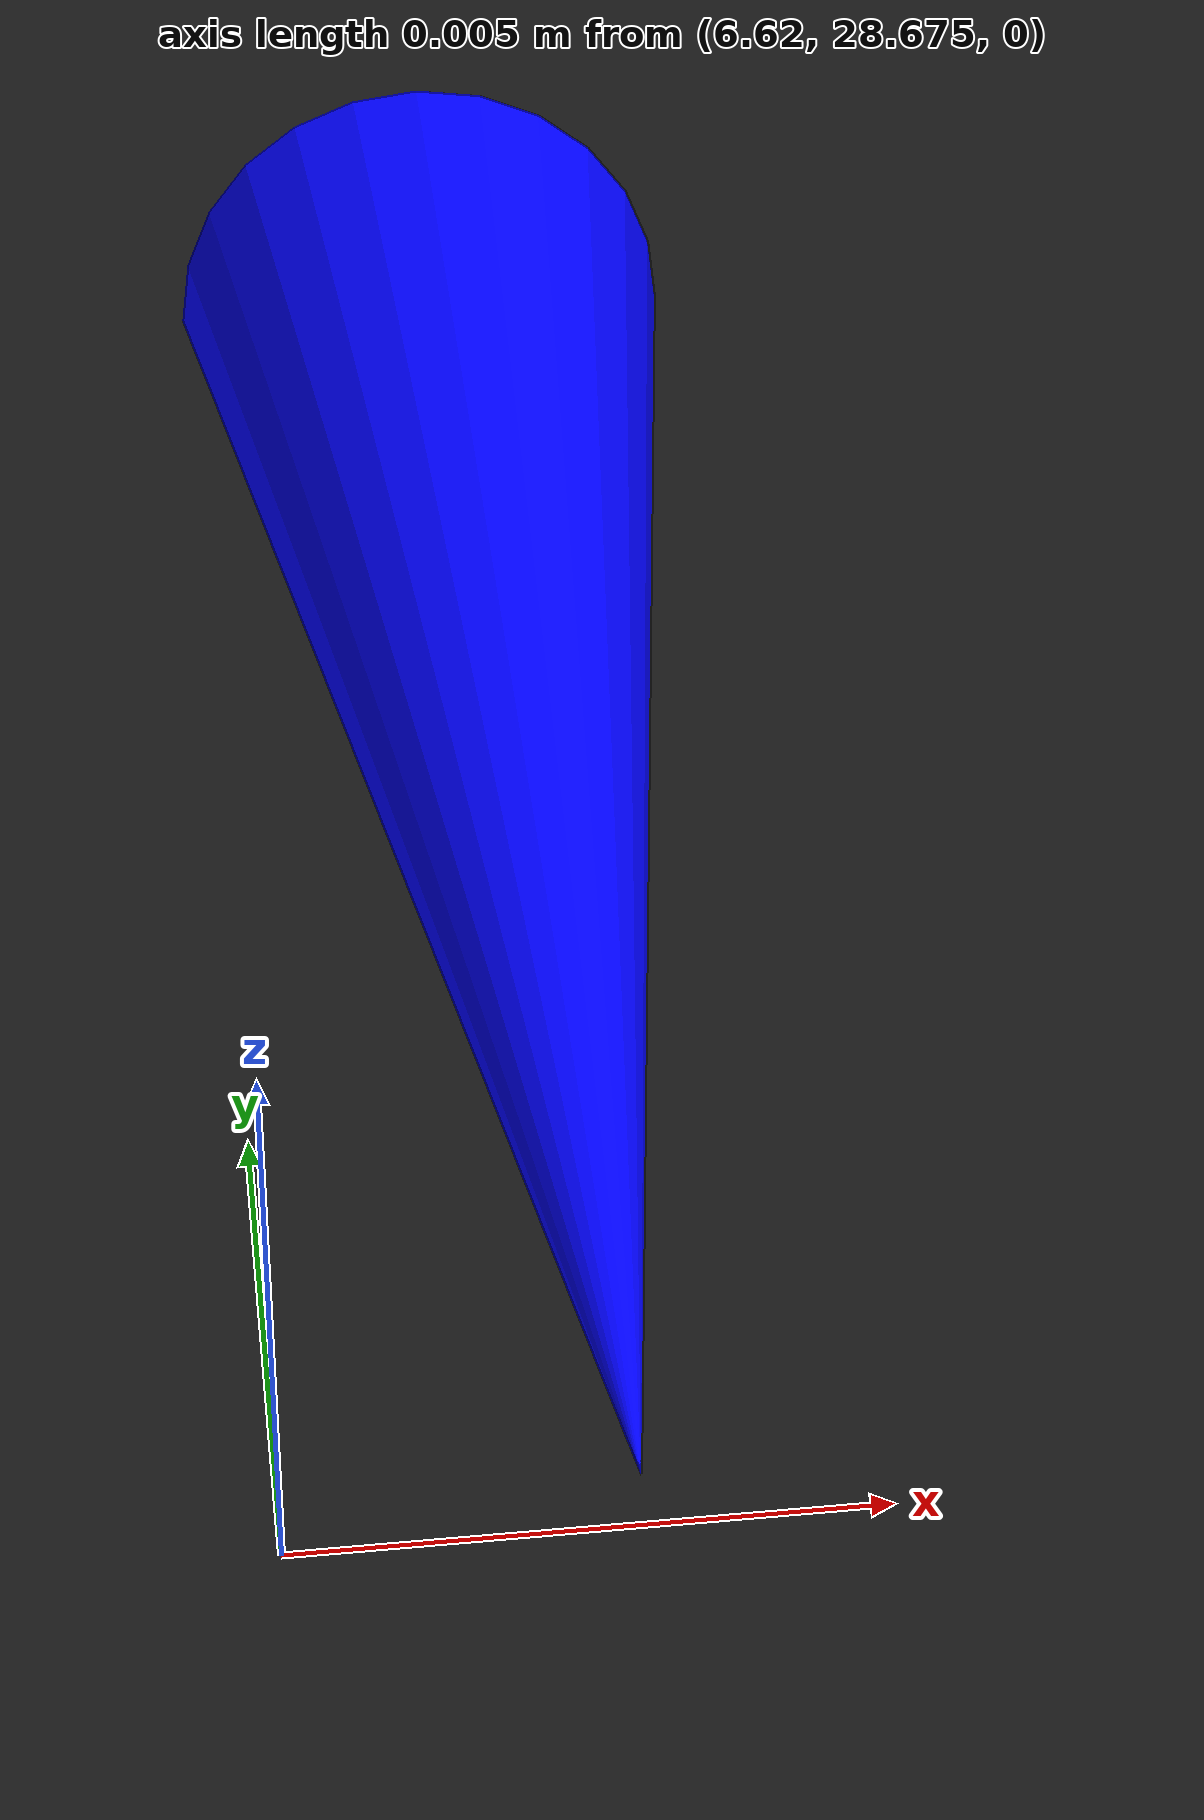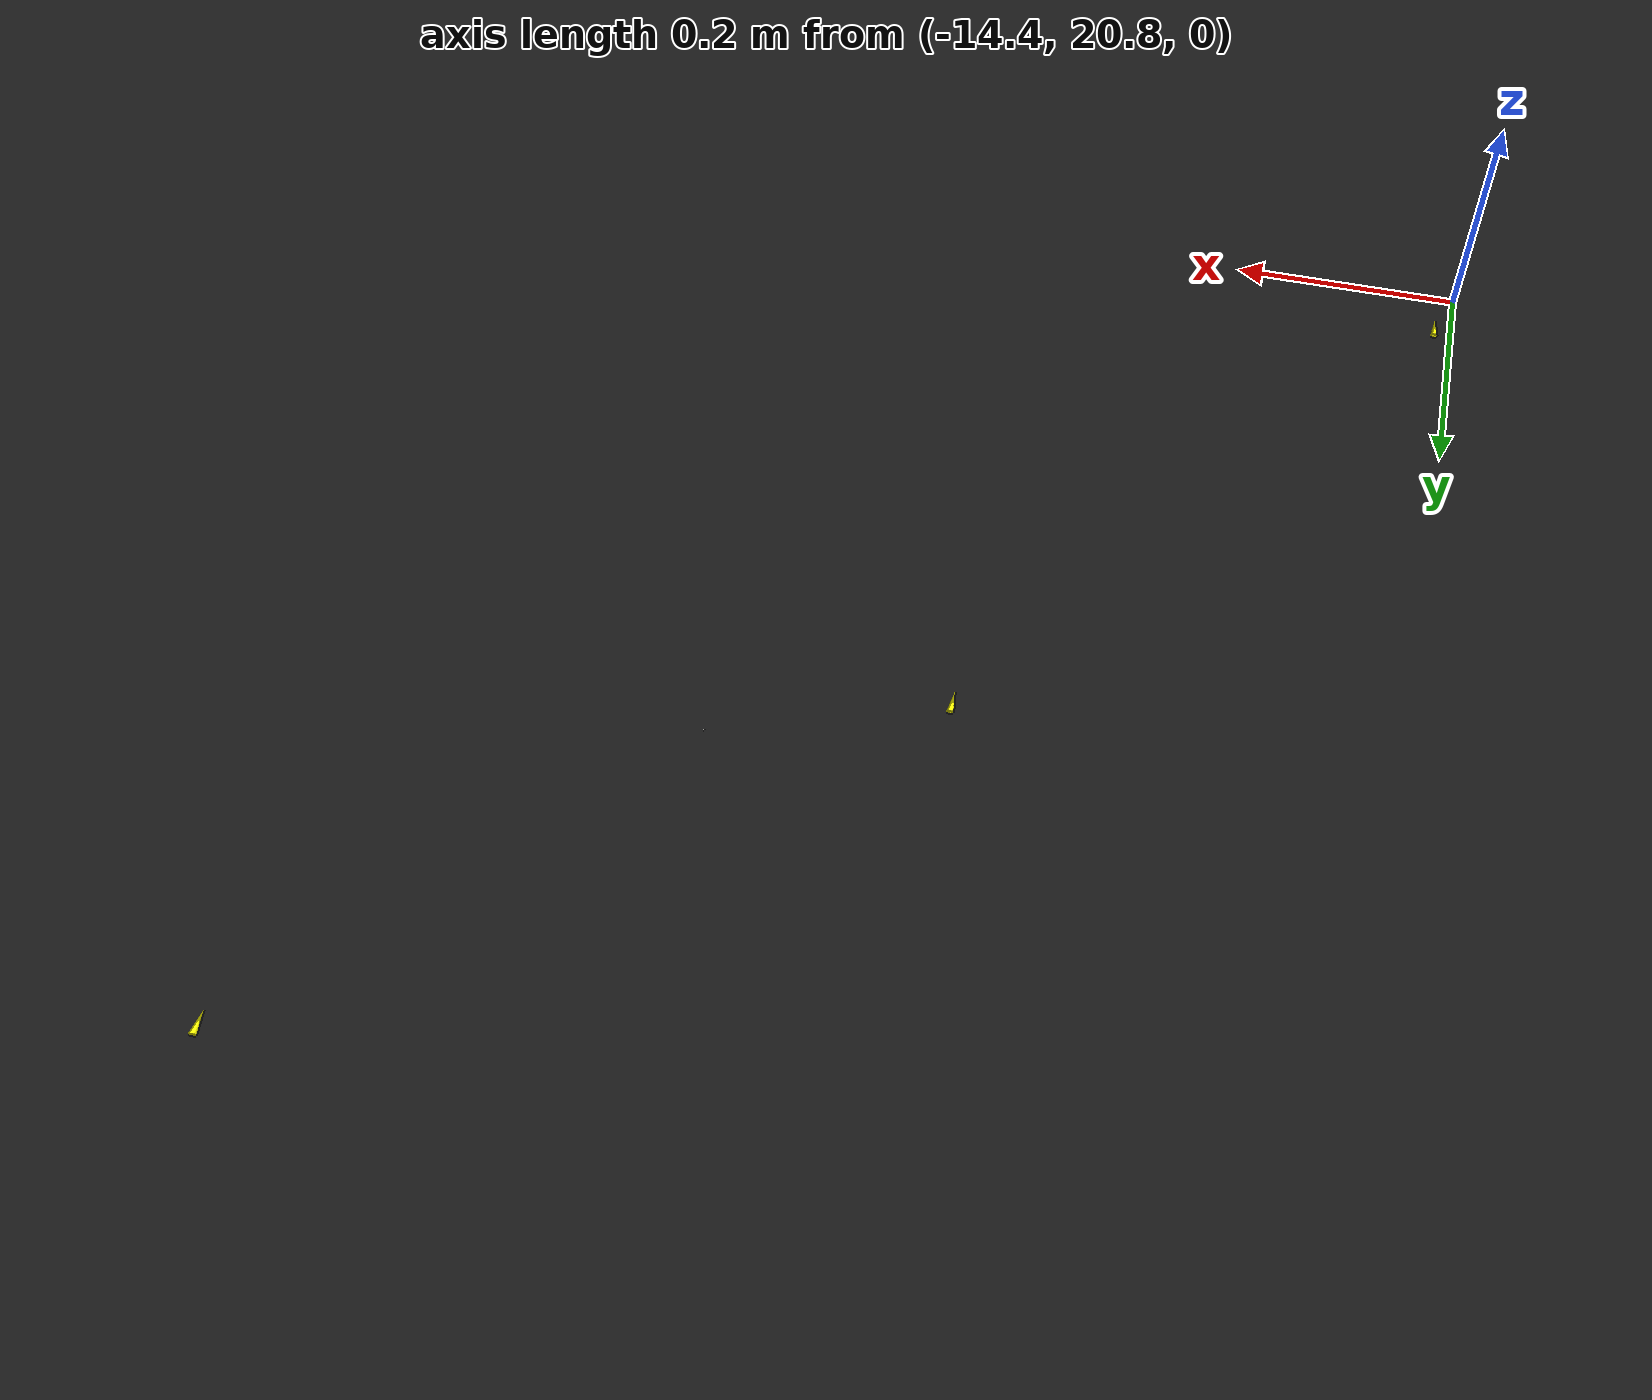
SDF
<?xml version="1.0"?>

<sdf version='1.9'>
    <world name='track'>

        <!-- PHYSICS -->
        <!-- http://sdformat.org/spec?ver=1.11&elem=physics#physics_real_time_update_rate  -->
        <physics name="1ms" type="dart">
            <max_step_size>0.001</max_step_size>
            <real_time_factor>1.0</real_time_factor>
            <max_contacts>1000</max_contacts>
            <dart>
                <solver>
                    <solver_type>pgs</solver_type>
                </solver>
                <collision_detector>bullet</collision_detector>
            </dart>
        </physics>

        <gravity>0 0 -9.8</gravity>
        <magnetic_field>6e-06 2.3e-05 -4.2e-05</magnetic_field>
        <atmosphere type='adiabatic'/>

        <!-- PLUGINS -->
        <plugin name='gz::sim::systems::Physics' filename='gz-sim-physics-system'/>
        <plugin name='gz::sim::systems::UserCommands' filename='gz-sim-user-commands-system'/>
        <plugin name='gz::sim::systems::SceneBroadcaster' filename='gz-sim-scene-broadcaster-system'/>
        <plugin name="gz::sim::systems::Imu" filename="gz-sim-imu-system"/>

        <gui fullscreen='0'>
            <!-- 3D scene -->
            <plugin filename="MinimalScene" name="3D View">
                <gz-gui>
                <title>3D View</title>
                <property type="bool" key="showTitleBar">false</property>
                <property type="string" key="state">docked</property>
                </gz-gui>

                <engine>ogre2</engine>
                <scene>scene</scene>
                <ambient_light>0.4 0.4 0.4</ambient_light>
                <background_color>0.8 0.8 0.8</background_color>
                <camera_pose>-6 0 6 0 0.5 0</camera_pose>
            </plugin>

            <!-- Plugins that add functionality to the scene -->
            <plugin filename="EntityContextMenuPlugin" name="Entity context menu">
                <gz-gui>
                <property key="state" type="string">floating</property>
                <property key="width" type="double">5</property>
                <property key="height" type="double">5</property>
                <property key="showTitleBar" type="bool">false</property>
                </gz-gui>
            </plugin>
            <plugin filename="GzSceneManager" name="Scene Manager">
                <gz-gui>
                <property key="resizable" type="bool">false</property>
                <property key="width" type="double">5</property>
                <property key="height" type="double">5</property>
                <property key="state" type="string">floating</property>
                <property key="showTitleBar" type="bool">false</property>
                </gz-gui>
            </plugin>
            <plugin filename="InteractiveViewControl" name="Interactive view control">
                <gz-gui>
                <property key="resizable" type="bool">false</property>
                <property key="width" type="double">5</property>
                <property key="height" type="double">5</property>
                <property key="state" type="string">floating</property>
                <property key="showTitleBar" type="bool">false</property>
                </gz-gui>
            </plugin>
            <plugin filename="CameraTracking" name="Camera Tracking">
                <gz-gui>
                <property key="resizable" type="bool">false</property>
                <property key="width" type="double">5</property>
                <property key="height" type="double">5</property>
                <property key="state" type="string">floating</property>
                <property key="showTitleBar" type="bool">false</property>
                </gz-gui>
            </plugin>
            <plugin name='World control' filename='WorldControl'>
                <gz-gui>
                    <title>World control</title>
                    <property type='bool' key='showTitleBar'>0</property>
                    <property type='bool' key='resizable'>0</property>
                    <property type='double' key='height'>72</property>
                    <property type='double' key='z'>1</property>
                    <property type='string' key='state'>floating</property>
                    <anchors target='3D View'>
                        <line own='left' target='left'/>
                        <line own='bottom' target='bottom'/>
                    </anchors>
                </gz-gui>
                <play_pause>1</play_pause>
                <step>1</step>
                <start_paused>1</start_paused>
            </plugin>
            <plugin name='World stats' filename='WorldStats'>
                <gz-gui>
                    <title>World stats</title>
                    <property type='bool' key='showTitleBar'>0</property>
                    <property type='bool' key='resizable'>0</property>
                    <property type='double' key='height'>110</property>
                    <property type='double' key='width'>290</property>
                    <property type='double' key='z'>1</property>
                    <property type='string' key='state'>floating</property>
                    <anchors target='3D View'>
                        <line own='right' target='right'/>
                        <line own='bottom' target='bottom'/>
                    </anchors>
                </gz-gui>
                <sim_time>1</sim_time>
                <real_time>1</real_time>
                <real_time_factor>1</real_time_factor>
                <iterations>1</iterations>
            </plugin>

            <plugin filename="VisualizeLidar" name="Visualize Lidar">
            </plugin>

            <plugin filename="ImageDisplay" name="Image Display">
            </plugin>

            <!-- Inspector -->
            <plugin filename="ComponentInspector" name="Component inspector">
                <ignition-gui>
                <property type="string" key="state">docked</property>
                </ignition-gui>
            </plugin>

            <!-- Entity tree -->
            <plugin filename="EntityTree" name="Entity tree">
                <ignition-gui>
                <property type="string" key="state">docked</property>
                </ignition-gui>
            </plugin>
        </gui>

        <!-- SENSORS -->

        <plugin
        filename="gz-sim-sensors-system"
        name="gz::sim::systems::Sensors">
        <render_engine>ogre2</render_engine>
        </plugin>

        <!-- AMBIENT -->

        <scene>
            <ambient>1 1 1 1</ambient>
            <background>0.8 0.8 0.8 1</background>
            <shadows>1</shadows>
        </scene>
        <light name='sun' type='directional'>
            <cast_shadows>1</cast_shadows>
            <pose>0 0 10 0 0 0</pose>
            <diffuse>0.8 0.8 0.8 1</diffuse>
            <specular>0.8 0.8 0.8 1</specular>
            <attenuation>
                <range>1000</range>
                <constant>0.9</constant>
                <linear>0.01</linear>
                <quadratic>0.001</quadratic>
            </attenuation>
            <direction>-0.5 0.1 -0.9</direction>
        </light>

        <model name='ground_plane'>
            <static>true</static>
            <link name='link'>
                <collision name='collision'>
                    <geometry>
                        <plane>
                        <normal>0 0 1</normal>
                        <size>100 100</size>
                        </plane>
                    </geometry>

                    <surface>
                        <friction>
                            <dart/>
                        </friction>
                        <bounce/>
                        <contact/>
                    </surface>
                </collision>

                <visual name='visual'>
                    <geometry>
                        <plane>
                        <normal>0 0 1</normal>
                        <size>100 100</size>
                        </plane>
                    </geometry>
                    <material>
                        <ambient>0.1 0.1 0.1 1</ambient>
                        <diffuse>0.1 0.1 0.1 1</diffuse>
                        <specular>0.8 0.8 0.8 1</specular>
                    </material>
                </visual>

                <pose>0 0 0 0 -0 0</pose>

                <inertial>
                    <pose>0 0 0 0 -0 0</pose>
                    <mass>1</mass>
                    <inertia>
                        <ixx>1</ixx>
                        <ixy>0</ixy>
                        <ixz>0</ixz>
                        <iyy>1</iyy>
                        <iyz>0</iyz>
                        <izz>1</izz>
                    </inertia>
                </inertial>

                <enable_wind>false</enable_wind>

            </link>

            <pose>0 0 0 0 -0 0</pose>

            <self_collide>false</self_collide>
        </model>

        <!-- TRACK -->
        <model name='cones'>
            <pose>0 0 0 0 0 0</pose>

      <link name='cone_0_link'>
        <collision name='cone_0_collision'>
          <geometry>
            <mesh>
              <uri>/home/ubuntu/psd_ws/src/psd_gazebo_sim/psd_gazebo_worlds/world/models/cone/meshes/cone.stl</uri>
              <scale>0.001 0.001 0.001</scale>
            </mesh>
          </geometry>
        </collision>
        <visual name='cone_0_visual'>
          <geometry>
            <mesh>
              <uri>/home/ubuntu/psd_ws/src/psd_gazebo_sim/psd_gazebo_worlds/world/models/cone/meshes/cone.stl</uri>
              <scale>0.001 0.001 0.001</scale>
            </mesh>
          </geometry>
          <material>
            <ambient>1 1 0 1</ambient>
            <diffuse>1 1 0 1</diffuse>
            <specular>1 1 0 1</specular>
          </material>
        </visual>
        <pose>5.688073933774838 25.57597586423841 0.0 1.57 0 0</pose>
        <enable_wind>false</enable_wind>
      </link>

      <link name='cone_1_link'>
        <collision name='cone_1_collision'>
          <geometry>
            <mesh>
              <uri>/home/ubuntu/psd_ws/src/psd_gazebo_sim/psd_gazebo_worlds/world/models/cone/meshes/cone.stl</uri>
              <scale>0.001 0.001 0.001</scale>
            </mesh>
          </geometry>
        </collision>
        <visual name='cone_1_visual'>
          <geometry>
            <mesh>
              <uri>/home/ubuntu/psd_ws/src/psd_gazebo_sim/psd_gazebo_worlds/world/models/cone/meshes/cone.stl</uri>
              <scale>0.001 0.001 0.001</scale>
            </mesh>
          </geometry>
          <material>
            <ambient>1 1 0 1</ambient>
            <diffuse>1 1 0 1</diffuse>
            <specular>1 1 0 1</specular>
          </material>
        </visual>
        <pose>6.686783433774838 25.60839286423841 0.0 1.57 0 0</pose>
        <enable_wind>false</enable_wind>
      </link>

      <link name='cone_2_link'>
        <collision name='cone_2_collision'>
          <geometry>
            <mesh>
              <uri>/home/ubuntu/psd_ws/src/psd_gazebo_sim/psd_gazebo_worlds/world/models/cone/meshes/cone.stl</uri>
              <scale>0.001 0.001 0.001</scale>
            </mesh>
          </geometry>
        </collision>
        <visual name='cone_2_visual'>
          <geometry>
            <mesh>
              <uri>/home/ubuntu/psd_ws/src/psd_gazebo_sim/psd_gazebo_worlds/world/models/cone/meshes/cone.stl</uri>
              <scale>0.001 0.001 0.001</scale>
            </mesh>
          </geometry>
          <material>
            <ambient>1 1 0 1</ambient>
            <diffuse>1 1 0 1</diffuse>
            <specular>1 1 0 1</specular>
          </material>
        </visual>
        <pose>7.683275433774838 25.641048864238407 0.0 1.57 0 0</pose>
        <enable_wind>false</enable_wind>
      </link>

      <link name='cone_3_link'>
        <collision name='cone_3_collision'>
          <geometry>
            <mesh>
              <uri>/home/ubuntu/psd_ws/src/psd_gazebo_sim/psd_gazebo_worlds/world/models/cone/meshes/cone.stl</uri>
              <scale>0.001 0.001 0.001</scale>
            </mesh>
          </geometry>
        </collision>
        <visual name='cone_3_visual'>
          <geometry>
            <mesh>
              <uri>/home/ubuntu/psd_ws/src/psd_gazebo_sim/psd_gazebo_worlds/world/models/cone/meshes/cone.stl</uri>
              <scale>0.001 0.001 0.001</scale>
            </mesh>
          </geometry>
          <material>
            <ambient>1 1 0 1</ambient>
            <diffuse>1 1 0 1</diffuse>
            <specular>1 1 0 1</specular>
          </material>
        </visual>
        <pose>8.677596433774838 25.67247836423841 0.0 1.57 0 0</pose>
        <enable_wind>false</enable_wind>
      </link>

      <link name='cone_4_link'>
        <collision name='cone_4_collision'>
          <geometry>
            <mesh>
              <uri>/home/ubuntu/psd_ws/src/psd_gazebo_sim/psd_gazebo_worlds/world/models/cone/meshes/cone.stl</uri>
              <scale>0.001 0.001 0.001</scale>
            </mesh>
          </geometry>
        </collision>
        <visual name='cone_4_visual'>
          <geometry>
            <mesh>
              <uri>/home/ubuntu/psd_ws/src/psd_gazebo_sim/psd_gazebo_worlds/world/models/cone/meshes/cone.stl</uri>
              <scale>0.001 0.001 0.001</scale>
            </mesh>
          </geometry>
          <material>
            <ambient>1 1 0 1</ambient>
            <diffuse>1 1 0 1</diffuse>
            <specular>1 1 0 1</specular>
          </material>
        </visual>
        <pose>9.669788433774837 25.70122536423841 0.0 1.57 0 0</pose>
        <enable_wind>false</enable_wind>
      </link>

      <link name='cone_5_link'>
        <collision name='cone_5_collision'>
          <geometry>
            <mesh>
              <uri>/home/ubuntu/psd_ws/src/psd_gazebo_sim/psd_gazebo_worlds/world/models/cone/meshes/cone.stl</uri>
              <scale>0.001 0.001 0.001</scale>
            </mesh>
          </geometry>
        </collision>
        <visual name='cone_5_visual'>
          <geometry>
            <mesh>
              <uri>/home/ubuntu/psd_ws/src/psd_gazebo_sim/psd_gazebo_worlds/world/models/cone/meshes/cone.stl</uri>
              <scale>0.001 0.001 0.001</scale>
            </mesh>
          </geometry>
          <material>
            <ambient>1 1 0 1</ambient>
            <diffuse>1 1 0 1</diffuse>
            <specular>1 1 0 1</specular>
          </material>
        </visual>
        <pose>10.659880933774836 25.72584286423841 0.0 1.57 0 0</pose>
        <enable_wind>false</enable_wind>
      </link>

      <link name='cone_6_link'>
        <collision name='cone_6_collision'>
          <geometry>
            <mesh>
              <uri>/home/ubuntu/psd_ws/src/psd_gazebo_sim/psd_gazebo_worlds/world/models/cone/meshes/cone.stl</uri>
              <scale>0.001 0.001 0.001</scale>
            </mesh>
          </geometry>
        </collision>
        <visual name='cone_6_visual'>
          <geometry>
            <mesh>
              <uri>/home/ubuntu/psd_ws/src/psd_gazebo_sim/psd_gazebo_worlds/world/models/cone/meshes/cone.stl</uri>
              <scale>0.001 0.001 0.001</scale>
            </mesh>
          </geometry>
          <material>
            <ambient>1 1 0 1</ambient>
            <diffuse>1 1 0 1</diffuse>
            <specular>1 1 0 1</specular>
          </material>
        </visual>
        <pose>13.617552433774838 25.760592364238413 0.0 1.57 0 0</pose>
        <enable_wind>false</enable_wind>
      </link>

      <link name='cone_7_link'>
        <collision name='cone_7_collision'>
          <geometry>
            <mesh>
              <uri>/home/ubuntu/psd_ws/src/psd_gazebo_sim/psd_gazebo_worlds/world/models/cone/meshes/cone.stl</uri>
              <scale>0.001 0.001 0.001</scale>
            </mesh>
          </geometry>
        </collision>
        <visual name='cone_7_visual'>
          <geometry>
            <mesh>
              <uri>/home/ubuntu/psd_ws/src/psd_gazebo_sim/psd_gazebo_worlds/world/models/cone/meshes/cone.stl</uri>
              <scale>0.001 0.001 0.001</scale>
            </mesh>
          </geometry>
          <material>
            <ambient>1 1 0 1</ambient>
            <diffuse>1 1 0 1</diffuse>
            <specular>1 1 0 1</specular>
          </material>
        </visual>
        <pose>14.59909143377484 25.754414864238413 0.0 1.57 0 0</pose>
        <enable_wind>false</enable_wind>
      </link>

      <link name='cone_8_link'>
        <collision name='cone_8_collision'>
          <geometry>
            <mesh>
              <uri>/home/ubuntu/psd_ws/src/psd_gazebo_sim/psd_gazebo_worlds/world/models/cone/meshes/cone.stl</uri>
              <scale>0.001 0.001 0.001</scale>
            </mesh>
          </geometry>
        </collision>
        <visual name='cone_8_visual'>
          <geometry>
            <mesh>
              <uri>/home/ubuntu/psd_ws/src/psd_gazebo_sim/psd_gazebo_worlds/world/models/cone/meshes/cone.stl</uri>
              <scale>0.001 0.001 0.001</scale>
            </mesh>
          </geometry>
          <material>
            <ambient>1 1 0 1</ambient>
            <diffuse>1 1 0 1</diffuse>
            <specular>1 1 0 1</specular>
          </material>
        </visual>
        <pose>15.578284933774837 25.73701836423841 0.0 1.57 0 0</pose>
        <enable_wind>false</enable_wind>
      </link>

      <link name='cone_9_link'>
        <collision name='cone_9_collision'>
          <geometry>
            <mesh>
              <uri>/home/ubuntu/psd_ws/src/psd_gazebo_sim/psd_gazebo_worlds/world/models/cone/meshes/cone.stl</uri>
              <scale>0.001 0.001 0.001</scale>
            </mesh>
          </geometry>
        </collision>
        <visual name='cone_9_visual'>
          <geometry>
            <mesh>
              <uri>/home/ubuntu/psd_ws/src/psd_gazebo_sim/psd_gazebo_worlds/world/models/cone/meshes/cone.stl</uri>
              <scale>0.001 0.001 0.001</scale>
            </mesh>
          </geometry>
          <material>
            <ambient>1 1 0 1</ambient>
            <diffuse>1 1 0 1</diffuse>
            <specular>1 1 0 1</specular>
          </material>
        </visual>
        <pose>16.554961433774835 25.707018364238408 0.0 1.57 0 0</pose>
        <enable_wind>false</enable_wind>
      </link>

      <link name='cone_10_link'>
        <collision name='cone_10_collision'>
          <geometry>
            <mesh>
              <uri>/home/ubuntu/psd_ws/src/psd_gazebo_sim/psd_gazebo_worlds/world/models/cone/meshes/cone.stl</uri>
              <scale>0.001 0.001 0.001</scale>
            </mesh>
          </geometry>
        </collision>
        <visual name='cone_10_visual'>
          <geometry>
            <mesh>
              <uri>/home/ubuntu/psd_ws/src/psd_gazebo_sim/psd_gazebo_worlds/world/models/cone/meshes/cone.stl</uri>
              <scale>0.001 0.001 0.001</scale>
            </mesh>
          </geometry>
          <material>
            <ambient>1 1 0 1</ambient>
            <diffuse>1 1 0 1</diffuse>
            <specular>1 1 0 1</specular>
          </material>
        </visual>
        <pose>17.528895433774835 25.663042364238407 0.0 1.57 0 0</pose>
        <enable_wind>false</enable_wind>
      </link>

      <link name='cone_11_link'>
        <collision name='cone_11_collision'>
          <geometry>
            <mesh>
              <uri>/home/ubuntu/psd_ws/src/psd_gazebo_sim/psd_gazebo_worlds/world/models/cone/meshes/cone.stl</uri>
              <scale>0.001 0.001 0.001</scale>
            </mesh>
          </geometry>
        </collision>
        <visual name='cone_11_visual'>
          <geometry>
            <mesh>
              <uri>/home/ubuntu/psd_ws/src/psd_gazebo_sim/psd_gazebo_worlds/world/models/cone/meshes/cone.stl</uri>
              <scale>0.001 0.001 0.001</scale>
            </mesh>
          </geometry>
          <material>
            <ambient>1 1 0 1</ambient>
            <diffuse>1 1 0 1</diffuse>
            <specular>1 1 0 1</specular>
          </material>
        </visual>
        <pose>18.480635433774836 25.60132436423841 0.0 1.57 0 0</pose>
        <enable_wind>false</enable_wind>
      </link>

      <link name='cone_12_link'>
        <collision name='cone_12_collision'>
          <geometry>
            <mesh>
              <uri>/home/ubuntu/psd_ws/src/psd_gazebo_sim/psd_gazebo_worlds/world/models/cone/meshes/cone.stl</uri>
              <scale>0.001 0.001 0.001</scale>
            </mesh>
          </geometry>
        </collision>
        <visual name='cone_12_visual'>
          <geometry>
            <mesh>
              <uri>/home/ubuntu/psd_ws/src/psd_gazebo_sim/psd_gazebo_worlds/world/models/cone/meshes/cone.stl</uri>
              <scale>0.001 0.001 0.001</scale>
            </mesh>
          </geometry>
          <material>
            <ambient>1 1 0 1</ambient>
            <diffuse>1 1 0 1</diffuse>
            <specular>1 1 0 1</specular>
          </material>
        </visual>
        <pose>19.381697933774838 25.50222886423841 0.0 1.57 0 0</pose>
        <enable_wind>false</enable_wind>
      </link>

      <link name='cone_13_link'>
        <collision name='cone_13_collision'>
          <geometry>
            <mesh>
              <uri>/home/ubuntu/psd_ws/src/psd_gazebo_sim/psd_gazebo_worlds/world/models/cone/meshes/cone.stl</uri>
              <scale>0.001 0.001 0.001</scale>
            </mesh>
          </geometry>
        </collision>
        <visual name='cone_13_visual'>
          <geometry>
            <mesh>
              <uri>/home/ubuntu/psd_ws/src/psd_gazebo_sim/psd_gazebo_worlds/world/models/cone/meshes/cone.stl</uri>
              <scale>0.001 0.001 0.001</scale>
            </mesh>
          </geometry>
          <material>
            <ambient>1 1 0 1</ambient>
            <diffuse>1 1 0 1</diffuse>
            <specular>1 1 0 1</specular>
          </material>
        </visual>
        <pose>21.00274043377484 25.108634364238412 0.0 1.57 0 0</pose>
        <enable_wind>false</enable_wind>
      </link>

      <link name='cone_14_link'>
        <collision name='cone_14_collision'>
          <geometry>
            <mesh>
              <uri>/home/ubuntu/psd_ws/src/psd_gazebo_sim/psd_gazebo_worlds/world/models/cone/meshes/cone.stl</uri>
              <scale>0.001 0.001 0.001</scale>
            </mesh>
          </geometry>
        </collision>
        <visual name='cone_14_visual'>
          <geometry>
            <mesh>
              <uri>/home/ubuntu/psd_ws/src/psd_gazebo_sim/psd_gazebo_worlds/world/models/cone/meshes/cone.stl</uri>
              <scale>0.001 0.001 0.001</scale>
            </mesh>
          </geometry>
          <material>
            <ambient>1 1 0 1</ambient>
            <diffuse>1 1 0 1</diffuse>
            <specular>1 1 0 1</specular>
          </material>
        </visual>
        <pose>21.69623793377484 24.78811186423841 0.0 1.57 0 0</pose>
        <enable_wind>false</enable_wind>
      </link>

      <link name='cone_15_link'>
        <collision name='cone_15_collision'>
          <geometry>
            <mesh>
              <uri>/home/ubuntu/psd_ws/src/psd_gazebo_sim/psd_gazebo_worlds/world/models/cone/meshes/cone.stl</uri>
              <scale>0.001 0.001 0.001</scale>
            </mesh>
          </geometry>
        </collision>
        <visual name='cone_15_visual'>
          <geometry>
            <mesh>
              <uri>/home/ubuntu/psd_ws/src/psd_gazebo_sim/psd_gazebo_worlds/world/models/cone/meshes/cone.stl</uri>
              <scale>0.001 0.001 0.001</scale>
            </mesh>
          </geometry>
          <material>
            <ambient>1 1 0 1</ambient>
            <diffuse>1 1 0 1</diffuse>
            <specular>1 1 0 1</specular>
          </material>
        </visual>
        <pose>22.815745433774836 23.855563864238412 0.0 1.57 0 0</pose>
        <enable_wind>false</enable_wind>
      </link>

      <link name='cone_16_link'>
        <collision name='cone_16_collision'>
          <geometry>
            <mesh>
              <uri>/home/ubuntu/psd_ws/src/psd_gazebo_sim/psd_gazebo_worlds/world/models/cone/meshes/cone.stl</uri>
              <scale>0.001 0.001 0.001</scale>
            </mesh>
          </geometry>
        </collision>
        <visual name='cone_16_visual'>
          <geometry>
            <mesh>
              <uri>/home/ubuntu/psd_ws/src/psd_gazebo_sim/psd_gazebo_worlds/world/models/cone/meshes/cone.stl</uri>
              <scale>0.001 0.001 0.001</scale>
            </mesh>
          </geometry>
          <material>
            <ambient>1 1 0 1</ambient>
            <diffuse>1 1 0 1</diffuse>
            <specular>1 1 0 1</specular>
          </material>
        </visual>
        <pose>23.26223843377484 23.23515736423841 0.0 1.57 0 0</pose>
        <enable_wind>false</enable_wind>
      </link>

      <link name='cone_17_link'>
        <collision name='cone_17_collision'>
          <geometry>
            <mesh>
              <uri>/home/ubuntu/psd_ws/src/psd_gazebo_sim/psd_gazebo_worlds/world/models/cone/meshes/cone.stl</uri>
              <scale>0.001 0.001 0.001</scale>
            </mesh>
          </geometry>
        </collision>
        <visual name='cone_17_visual'>
          <geometry>
            <mesh>
              <uri>/home/ubuntu/psd_ws/src/psd_gazebo_sim/psd_gazebo_worlds/world/models/cone/meshes/cone.stl</uri>
              <scale>0.001 0.001 0.001</scale>
            </mesh>
          </geometry>
          <material>
            <ambient>1 1 0 1</ambient>
            <diffuse>1 1 0 1</diffuse>
            <specular>1 1 0 1</specular>
          </material>
        </visual>
        <pose>23.625085433774842 22.533576864238412 0.0 1.57 0 0</pose>
        <enable_wind>false</enable_wind>
      </link>

      <link name='cone_18_link'>
        <collision name='cone_18_collision'>
          <geometry>
            <mesh>
              <uri>/home/ubuntu/psd_ws/src/psd_gazebo_sim/psd_gazebo_worlds/world/models/cone/meshes/cone.stl</uri>
              <scale>0.001 0.001 0.001</scale>
            </mesh>
          </geometry>
        </collision>
        <visual name='cone_18_visual'>
          <geometry>
            <mesh>
              <uri>/home/ubuntu/psd_ws/src/psd_gazebo_sim/psd_gazebo_worlds/world/models/cone/meshes/cone.stl</uri>
              <scale>0.001 0.001 0.001</scale>
            </mesh>
          </geometry>
          <material>
            <ambient>1 1 0 1</ambient>
            <diffuse>1 1 0 1</diffuse>
            <specular>1 1 0 1</specular>
          </material>
        </visual>
        <pose>23.90270843377484 21.767563364238413 0.0 1.57 0 0</pose>
        <enable_wind>false</enable_wind>
      </link>

      <link name='cone_19_link'>
        <collision name='cone_19_collision'>
          <geometry>
            <mesh>
              <uri>/home/ubuntu/psd_ws/src/psd_gazebo_sim/psd_gazebo_worlds/world/models/cone/meshes/cone.stl</uri>
              <scale>0.001 0.001 0.001</scale>
            </mesh>
          </geometry>
        </collision>
        <visual name='cone_19_visual'>
          <geometry>
            <mesh>
              <uri>/home/ubuntu/psd_ws/src/psd_gazebo_sim/psd_gazebo_worlds/world/models/cone/meshes/cone.stl</uri>
              <scale>0.001 0.001 0.001</scale>
            </mesh>
          </geometry>
          <material>
            <ambient>1 1 0 1</ambient>
            <diffuse>1 1 0 1</diffuse>
            <specular>1 1 0 1</specular>
          </material>
        </visual>
        <pose>24.168956933774837 20.17743936423841 0.0 1.57 0 0</pose>
        <enable_wind>false</enable_wind>
      </link>

      <link name='cone_20_link'>
        <collision name='cone_20_collision'>
          <geometry>
            <mesh>
              <uri>/home/ubuntu/psd_ws/src/psd_gazebo_sim/psd_gazebo_worlds/world/models/cone/meshes/cone.stl</uri>
              <scale>0.001 0.001 0.001</scale>
            </mesh>
          </geometry>
        </collision>
        <visual name='cone_20_visual'>
          <geometry>
            <mesh>
              <uri>/home/ubuntu/psd_ws/src/psd_gazebo_sim/psd_gazebo_worlds/world/models/cone/meshes/cone.stl</uri>
              <scale>0.001 0.001 0.001</scale>
            </mesh>
          </geometry>
          <material>
            <ambient>1 1 0 1</ambient>
            <diffuse>1 1 0 1</diffuse>
            <specular>1 1 0 1</specular>
          </material>
        </visual>
        <pose>24.14292943377484 19.390641364238405 0.0 1.57 0 0</pose>
        <enable_wind>false</enable_wind>
      </link>

      <link name='cone_21_link'>
        <collision name='cone_21_collision'>
          <geometry>
            <mesh>
              <uri>/home/ubuntu/psd_ws/src/psd_gazebo_sim/psd_gazebo_worlds/world/models/cone/meshes/cone.stl</uri>
              <scale>0.001 0.001 0.001</scale>
            </mesh>
          </geometry>
        </collision>
        <visual name='cone_21_visual'>
          <geometry>
            <mesh>
              <uri>/home/ubuntu/psd_ws/src/psd_gazebo_sim/psd_gazebo_worlds/world/models/cone/meshes/cone.stl</uri>
              <scale>0.001 0.001 0.001</scale>
            </mesh>
          </geometry>
          <material>
            <ambient>1 1 0 1</ambient>
            <diffuse>1 1 0 1</diffuse>
            <specular>1 1 0 1</specular>
          </material>
        </visual>
        <pose>24.006382933774837 18.629237364238406 0.0 1.57 0 0</pose>
        <enable_wind>false</enable_wind>
      </link>

      <link name='cone_22_link'>
        <collision name='cone_22_collision'>
          <geometry>
            <mesh>
              <uri>/home/ubuntu/psd_ws/src/psd_gazebo_sim/psd_gazebo_worlds/world/models/cone/meshes/cone.stl</uri>
              <scale>0.001 0.001 0.001</scale>
            </mesh>
          </geometry>
        </collision>
        <visual name='cone_22_visual'>
          <geometry>
            <mesh>
              <uri>/home/ubuntu/psd_ws/src/psd_gazebo_sim/psd_gazebo_worlds/world/models/cone/meshes/cone.stl</uri>
              <scale>0.001 0.001 0.001</scale>
            </mesh>
          </geometry>
          <material>
            <ambient>1 1 0 1</ambient>
            <diffuse>1 1 0 1</diffuse>
            <specular>1 1 0 1</specular>
          </material>
        </visual>
        <pose>23.759506933774837 17.91058686423841 0.0 1.57 0 0</pose>
        <enable_wind>false</enable_wind>
      </link>

      <link name='cone_23_link'>
        <collision name='cone_23_collision'>
          <geometry>
            <mesh>
              <uri>/home/ubuntu/psd_ws/src/psd_gazebo_sim/psd_gazebo_worlds/world/models/cone/meshes/cone.stl</uri>
              <scale>0.001 0.001 0.001</scale>
            </mesh>
          </geometry>
        </collision>
        <visual name='cone_23_visual'>
          <geometry>
            <mesh>
              <uri>/home/ubuntu/psd_ws/src/psd_gazebo_sim/psd_gazebo_worlds/world/models/cone/meshes/cone.stl</uri>
              <scale>0.001 0.001 0.001</scale>
            </mesh>
          </geometry>
          <material>
            <ambient>1 1 0 1</ambient>
            <diffuse>1 1 0 1</diffuse>
            <specular>1 1 0 1</specular>
          </material>
        </visual>
        <pose>23.40151843377484 17.24270186423841 0.0 1.57 0 0</pose>
        <enable_wind>false</enable_wind>
      </link>

      <link name='cone_24_link'>
        <collision name='cone_24_collision'>
          <geometry>
            <mesh>
              <uri>/home/ubuntu/psd_ws/src/psd_gazebo_sim/psd_gazebo_worlds/world/models/cone/meshes/cone.stl</uri>
              <scale>0.001 0.001 0.001</scale>
            </mesh>
          </geometry>
        </collision>
        <visual name='cone_24_visual'>
          <geometry>
            <mesh>
              <uri>/home/ubuntu/psd_ws/src/psd_gazebo_sim/psd_gazebo_worlds/world/models/cone/meshes/cone.stl</uri>
              <scale>0.001 0.001 0.001</scale>
            </mesh>
          </geometry>
          <material>
            <ambient>1 1 0 1</ambient>
            <diffuse>1 1 0 1</diffuse>
            <specular>1 1 0 1</specular>
          </material>
        </visual>
        <pose>22.365507433774837 16.04319436423841 0.0 1.57 0 0</pose>
        <enable_wind>false</enable_wind>
      </link>

      <link name='cone_25_link'>
        <collision name='cone_25_collision'>
          <geometry>
            <mesh>
              <uri>/home/ubuntu/psd_ws/src/psd_gazebo_sim/psd_gazebo_worlds/world/models/cone/meshes/cone.stl</uri>
              <scale>0.001 0.001 0.001</scale>
            </mesh>
          </geometry>
        </collision>
        <visual name='cone_25_visual'>
          <geometry>
            <mesh>
              <uri>/home/ubuntu/psd_ws/src/psd_gazebo_sim/psd_gazebo_worlds/world/models/cone/meshes/cone.stl</uri>
              <scale>0.001 0.001 0.001</scale>
            </mesh>
          </geometry>
          <material>
            <ambient>1 1 0 1</ambient>
            <diffuse>1 1 0 1</diffuse>
            <specular>1 1 0 1</specular>
          </material>
        </visual>
        <pose>21.007376433774837 15.072803364238407 0.0 1.57 0 0</pose>
        <enable_wind>false</enable_wind>
      </link>

      <link name='cone_26_link'>
        <collision name='cone_26_collision'>
          <geometry>
            <mesh>
              <uri>/home/ubuntu/psd_ws/src/psd_gazebo_sim/psd_gazebo_worlds/world/models/cone/meshes/cone.stl</uri>
              <scale>0.001 0.001 0.001</scale>
            </mesh>
          </geometry>
        </collision>
        <visual name='cone_26_visual'>
          <geometry>
            <mesh>
              <uri>/home/ubuntu/psd_ws/src/psd_gazebo_sim/psd_gazebo_worlds/world/models/cone/meshes/cone.stl</uri>
              <scale>0.001 0.001 0.001</scale>
            </mesh>
          </geometry>
          <material>
            <ambient>1 1 0 1</ambient>
            <diffuse>1 1 0 1</diffuse>
            <specular>1 1 0 1</specular>
          </material>
        </visual>
        <pose>20.26277543377484 14.703898364238409 0.0 1.57 0 0</pose>
        <enable_wind>false</enable_wind>
      </link>

      <link name='cone_27_link'>
        <collision name='cone_27_collision'>
          <geometry>
            <mesh>
              <uri>/home/ubuntu/psd_ws/src/psd_gazebo_sim/psd_gazebo_worlds/world/models/cone/meshes/cone.stl</uri>
              <scale>0.001 0.001 0.001</scale>
            </mesh>
          </geometry>
        </collision>
        <visual name='cone_27_visual'>
          <geometry>
            <mesh>
              <uri>/home/ubuntu/psd_ws/src/psd_gazebo_sim/psd_gazebo_worlds/world/models/cone/meshes/cone.stl</uri>
              <scale>0.001 0.001 0.001</scale>
            </mesh>
          </geometry>
          <material>
            <ambient>1 1 0 1</ambient>
            <diffuse>1 1 0 1</diffuse>
            <specular>1 1 0 1</specular>
          </material>
        </visual>
        <pose>19.489347933774837 14.42485286423841 0.0 1.57 0 0</pose>
        <enable_wind>false</enable_wind>
      </link>

      <link name='cone_28_link'>
        <collision name='cone_28_collision'>
          <geometry>
            <mesh>
              <uri>/home/ubuntu/psd_ws/src/psd_gazebo_sim/psd_gazebo_worlds/world/models/cone/meshes/cone.stl</uri>
              <scale>0.001 0.001 0.001</scale>
            </mesh>
          </geometry>
        </collision>
        <visual name='cone_28_visual'>
          <geometry>
            <mesh>
              <uri>/home/ubuntu/psd_ws/src/psd_gazebo_sim/psd_gazebo_worlds/world/models/cone/meshes/cone.stl</uri>
              <scale>0.001 0.001 0.001</scale>
            </mesh>
          </geometry>
          <material>
            <ambient>1 1 0 1</ambient>
            <diffuse>1 1 0 1</diffuse>
            <specular>1 1 0 1</specular>
          </material>
        </visual>
        <pose>18.69668843377484 14.242005364238409 0.0 1.57 0 0</pose>
        <enable_wind>false</enable_wind>
      </link>

      <link name='cone_29_link'>
        <collision name='cone_29_collision'>
          <geometry>
            <mesh>
              <uri>/home/ubuntu/psd_ws/src/psd_gazebo_sim/psd_gazebo_worlds/world/models/cone/meshes/cone.stl</uri>
              <scale>0.001 0.001 0.001</scale>
            </mesh>
          </geometry>
        </collision>
        <visual name='cone_29_visual'>
          <geometry>
            <mesh>
              <uri>/home/ubuntu/psd_ws/src/psd_gazebo_sim/psd_gazebo_worlds/world/models/cone/meshes/cone.stl</uri>
              <scale>0.001 0.001 0.001</scale>
            </mesh>
          </geometry>
          <material>
            <ambient>1 1 0 1</ambient>
            <diffuse>1 1 0 1</diffuse>
            <specular>1 1 0 1</specular>
          </material>
        </visual>
        <pose>17.896095933774838 14.16057736423841 0.0 1.57 0 0</pose>
        <enable_wind>false</enable_wind>
      </link>

      <link name='cone_30_link'>
        <collision name='cone_30_collision'>
          <geometry>
            <mesh>
              <uri>/home/ubuntu/psd_ws/src/psd_gazebo_sim/psd_gazebo_worlds/world/models/cone/meshes/cone.stl</uri>
              <scale>0.001 0.001 0.001</scale>
            </mesh>
          </geometry>
        </collision>
        <visual name='cone_30_visual'>
          <geometry>
            <mesh>
              <uri>/home/ubuntu/psd_ws/src/psd_gazebo_sim/psd_gazebo_worlds/world/models/cone/meshes/cone.stl</uri>
              <scale>0.001 0.001 0.001</scale>
            </mesh>
          </geometry>
          <material>
            <ambient>1 1 0 1</ambient>
            <diffuse>1 1 0 1</diffuse>
            <specular>1 1 0 1</specular>
          </material>
        </visual>
        <pose>17.093347933774837 14.183804864238407 0.0 1.57 0 0</pose>
        <enable_wind>false</enable_wind>
      </link>

      <link name='cone_31_link'>
        <collision name='cone_31_collision'>
          <geometry>
            <mesh>
              <uri>/home/ubuntu/psd_ws/src/psd_gazebo_sim/psd_gazebo_worlds/world/models/cone/meshes/cone.stl</uri>
              <scale>0.001 0.001 0.001</scale>
            </mesh>
          </geometry>
        </collision>
        <visual name='cone_31_visual'>
          <geometry>
            <mesh>
              <uri>/home/ubuntu/psd_ws/src/psd_gazebo_sim/psd_gazebo_worlds/world/models/cone/meshes/cone.stl</uri>
              <scale>0.001 0.001 0.001</scale>
            </mesh>
          </geometry>
          <material>
            <ambient>1 1 0 1</ambient>
            <diffuse>1 1 0 1</diffuse>
            <specular>1 1 0 1</specular>
          </material>
        </visual>
        <pose>16.283429433774835 14.30878436423841 0.0 1.57 0 0</pose>
        <enable_wind>false</enable_wind>
      </link>

      <link name='cone_32_link'>
        <collision name='cone_32_collision'>
          <geometry>
            <mesh>
              <uri>/home/ubuntu/psd_ws/src/psd_gazebo_sim/psd_gazebo_worlds/world/models/cone/meshes/cone.stl</uri>
              <scale>0.001 0.001 0.001</scale>
            </mesh>
          </geometry>
        </collision>
        <visual name='cone_32_visual'>
          <geometry>
            <mesh>
              <uri>/home/ubuntu/psd_ws/src/psd_gazebo_sim/psd_gazebo_worlds/world/models/cone/meshes/cone.stl</uri>
              <scale>0.001 0.001 0.001</scale>
            </mesh>
          </geometry>
          <material>
            <ambient>1 1 0 1</ambient>
            <diffuse>1 1 0 1</diffuse>
            <specular>1 1 0 1</specular>
          </material>
        </visual>
        <pose>14.678793433774837 14.83505986423841 0.0 1.57 0 0</pose>
        <enable_wind>false</enable_wind>
      </link>

      <link name='cone_33_link'>
        <collision name='cone_33_collision'>
          <geometry>
            <mesh>
              <uri>/home/ubuntu/psd_ws/src/psd_gazebo_sim/psd_gazebo_worlds/world/models/cone/meshes/cone.stl</uri>
              <scale>0.001 0.001 0.001</scale>
            </mesh>
          </geometry>
        </collision>
        <visual name='cone_33_visual'>
          <geometry>
            <mesh>
              <uri>/home/ubuntu/psd_ws/src/psd_gazebo_sim/psd_gazebo_worlds/world/models/cone/meshes/cone.stl</uri>
              <scale>0.001 0.001 0.001</scale>
            </mesh>
          </geometry>
          <material>
            <ambient>1 1 0 1</ambient>
            <diffuse>1 1 0 1</diffuse>
            <specular>1 1 0 1</specular>
          </material>
        </visual>
        <pose>13.12512243377484 15.67540736423841 0.0 1.57 0 0</pose>
        <enable_wind>false</enable_wind>
      </link>

      <link name='cone_34_link'>
        <collision name='cone_34_collision'>
          <geometry>
            <mesh>
              <uri>/home/ubuntu/psd_ws/src/psd_gazebo_sim/psd_gazebo_worlds/world/models/cone/meshes/cone.stl</uri>
              <scale>0.001 0.001 0.001</scale>
            </mesh>
          </geometry>
        </collision>
        <visual name='cone_34_visual'>
          <geometry>
            <mesh>
              <uri>/home/ubuntu/psd_ws/src/psd_gazebo_sim/psd_gazebo_worlds/world/models/cone/meshes/cone.stl</uri>
              <scale>0.001 0.001 0.001</scale>
            </mesh>
          </geometry>
          <material>
            <ambient>1 1 0 1</ambient>
            <diffuse>1 1 0 1</diffuse>
            <specular>1 1 0 1</specular>
          </material>
        </visual>
        <pose>12.344447433774839 16.19527936423841 0.0 1.57 0 0</pose>
        <enable_wind>false</enable_wind>
      </link>

      <link name='cone_35_link'>
        <collision name='cone_35_collision'>
          <geometry>
            <mesh>
              <uri>/home/ubuntu/psd_ws/src/psd_gazebo_sim/psd_gazebo_worlds/world/models/cone/meshes/cone.stl</uri>
              <scale>0.001 0.001 0.001</scale>
            </mesh>
          </geometry>
        </collision>
        <visual name='cone_35_visual'>
          <geometry>
            <mesh>
              <uri>/home/ubuntu/psd_ws/src/psd_gazebo_sim/psd_gazebo_worlds/world/models/cone/meshes/cone.stl</uri>
              <scale>0.001 0.001 0.001</scale>
            </mesh>
          </geometry>
          <material>
            <ambient>1 1 0 1</ambient>
            <diffuse>1 1 0 1</diffuse>
            <specular>1 1 0 1</specular>
          </material>
        </visual>
        <pose>11.542868933774837 16.75925436423841 0.0 1.57 0 0</pose>
        <enable_wind>false</enable_wind>
      </link>

      <link name='cone_36_link'>
        <collision name='cone_36_collision'>
          <geometry>
            <mesh>
              <uri>/home/ubuntu/psd_ws/src/psd_gazebo_sim/psd_gazebo_worlds/world/models/cone/meshes/cone.stl</uri>
              <scale>0.001 0.001 0.001</scale>
            </mesh>
          </geometry>
        </collision>
        <visual name='cone_36_visual'>
          <geometry>
            <mesh>
              <uri>/home/ubuntu/psd_ws/src/psd_gazebo_sim/psd_gazebo_worlds/world/models/cone/meshes/cone.stl</uri>
              <scale>0.001 0.001 0.001</scale>
            </mesh>
          </geometry>
          <material>
            <ambient>1 1 0 1</ambient>
            <diffuse>1 1 0 1</diffuse>
            <specular>1 1 0 1</specular>
          </material>
        </visual>
        <pose>10.705428933774837 17.34542386423841 0.0 1.57 0 0</pose>
        <enable_wind>false</enable_wind>
      </link>

      <link name='cone_37_link'>
        <collision name='cone_37_collision'>
          <geometry>
            <mesh>
              <uri>/home/ubuntu/psd_ws/src/psd_gazebo_sim/psd_gazebo_worlds/world/models/cone/meshes/cone.stl</uri>
              <scale>0.001 0.001 0.001</scale>
            </mesh>
          </geometry>
        </collision>
        <visual name='cone_37_visual'>
          <geometry>
            <mesh>
              <uri>/home/ubuntu/psd_ws/src/psd_gazebo_sim/psd_gazebo_worlds/world/models/cone/meshes/cone.stl</uri>
              <scale>0.001 0.001 0.001</scale>
            </mesh>
          </geometry>
          <material>
            <ambient>1 1 0 1</ambient>
            <diffuse>1 1 0 1</diffuse>
            <specular>1 1 0 1</specular>
          </material>
        </visual>
        <pose>9.815351933774838 17.92882986423841 0.0 1.57 0 0</pose>
        <enable_wind>false</enable_wind>
      </link>

      <link name='cone_38_link'>
        <collision name='cone_38_collision'>
          <geometry>
            <mesh>
              <uri>/home/ubuntu/psd_ws/src/psd_gazebo_sim/psd_gazebo_worlds/world/models/cone/meshes/cone.stl</uri>
              <scale>0.001 0.001 0.001</scale>
            </mesh>
          </geometry>
        </collision>
        <visual name='cone_38_visual'>
          <geometry>
            <mesh>
              <uri>/home/ubuntu/psd_ws/src/psd_gazebo_sim/psd_gazebo_worlds/world/models/cone/meshes/cone.stl</uri>
              <scale>0.001 0.001 0.001</scale>
            </mesh>
          </geometry>
          <material>
            <ambient>1 1 0 1</ambient>
            <diffuse>1 1 0 1</diffuse>
            <specular>1 1 0 1</specular>
          </material>
        </visual>
        <pose>7.819146433774838 18.96266636423841 0.0 1.57 0 0</pose>
        <enable_wind>false</enable_wind>
      </link>

      <link name='cone_39_link'>
        <collision name='cone_39_collision'>
          <geometry>
            <mesh>
              <uri>/home/ubuntu/psd_ws/src/psd_gazebo_sim/psd_gazebo_worlds/world/models/cone/meshes/cone.stl</uri>
              <scale>0.001 0.001 0.001</scale>
            </mesh>
          </geometry>
        </collision>
        <visual name='cone_39_visual'>
          <geometry>
            <mesh>
              <uri>/home/ubuntu/psd_ws/src/psd_gazebo_sim/psd_gazebo_worlds/world/models/cone/meshes/cone.stl</uri>
              <scale>0.001 0.001 0.001</scale>
            </mesh>
          </geometry>
          <material>
            <ambient>1 1 0 1</ambient>
            <diffuse>1 1 0 1</diffuse>
            <specular>1 1 0 1</specular>
          </material>
        </visual>
        <pose>6.736016433774838 19.340075864238408 0.0 1.57 0 0</pose>
        <enable_wind>false</enable_wind>
      </link>

      <link name='cone_40_link'>
        <collision name='cone_40_collision'>
          <geometry>
            <mesh>
              <uri>/home/ubuntu/psd_ws/src/psd_gazebo_sim/psd_gazebo_worlds/world/models/cone/meshes/cone.stl</uri>
              <scale>0.001 0.001 0.001</scale>
            </mesh>
          </geometry>
        </collision>
        <visual name='cone_40_visual'>
          <geometry>
            <mesh>
              <uri>/home/ubuntu/psd_ws/src/psd_gazebo_sim/psd_gazebo_worlds/world/models/cone/meshes/cone.stl</uri>
              <scale>0.001 0.001 0.001</scale>
            </mesh>
          </geometry>
          <material>
            <ambient>1 1 0 1</ambient>
            <diffuse>1 1 0 1</diffuse>
            <specular>1 1 0 1</specular>
          </material>
        </visual>
        <pose>5.6256884337748385 19.60826686423841 0.0 1.57 0 0</pose>
        <enable_wind>false</enable_wind>
      </link>

      <link name='cone_41_link'>
        <collision name='cone_41_collision'>
          <geometry>
            <mesh>
              <uri>/home/ubuntu/psd_ws/src/psd_gazebo_sim/psd_gazebo_worlds/world/models/cone/meshes/cone.stl</uri>
              <scale>0.001 0.001 0.001</scale>
            </mesh>
          </geometry>
        </collision>
        <visual name='cone_41_visual'>
          <geometry>
            <mesh>
              <uri>/home/ubuntu/psd_ws/src/psd_gazebo_sim/psd_gazebo_worlds/world/models/cone/meshes/cone.stl</uri>
              <scale>0.001 0.001 0.001</scale>
            </mesh>
          </geometry>
          <material>
            <ambient>1 1 0 1</ambient>
            <diffuse>1 1 0 1</diffuse>
            <specular>1 1 0 1</specular>
          </material>
        </visual>
        <pose>4.499605933774838 19.769138864238407 0.0 1.57 0 0</pose>
        <enable_wind>false</enable_wind>
      </link>

      <link name='cone_42_link'>
        <collision name='cone_42_collision'>
          <geometry>
            <mesh>
              <uri>/home/ubuntu/psd_ws/src/psd_gazebo_sim/psd_gazebo_worlds/world/models/cone/meshes/cone.stl</uri>
              <scale>0.001 0.001 0.001</scale>
            </mesh>
          </geometry>
        </collision>
        <visual name='cone_42_visual'>
          <geometry>
            <mesh>
              <uri>/home/ubuntu/psd_ws/src/psd_gazebo_sim/psd_gazebo_worlds/world/models/cone/meshes/cone.stl</uri>
              <scale>0.001 0.001 0.001</scale>
            </mesh>
          </geometry>
          <material>
            <ambient>1 1 0 1</ambient>
            <diffuse>1 1 0 1</diffuse>
            <specular>1 1 0 1</specular>
          </material>
        </visual>
        <pose>2.237851433774838 19.78154936423841 0.0 1.57 0 0</pose>
        <enable_wind>false</enable_wind>
      </link>

      <link name='cone_43_link'>
        <collision name='cone_43_collision'>
          <geometry>
            <mesh>
              <uri>/home/ubuntu/psd_ws/src/psd_gazebo_sim/psd_gazebo_worlds/world/models/cone/meshes/cone.stl</uri>
              <scale>0.001 0.001 0.001</scale>
            </mesh>
          </geometry>
        </collision>
        <visual name='cone_43_visual'>
          <geometry>
            <mesh>
              <uri>/home/ubuntu/psd_ws/src/psd_gazebo_sim/psd_gazebo_worlds/world/models/cone/meshes/cone.stl</uri>
              <scale>0.001 0.001 0.001</scale>
            </mesh>
          </geometry>
          <material>
            <ambient>1 1 0 1</ambient>
            <diffuse>1 1 0 1</diffuse>
            <specular>1 1 0 1</specular>
          </material>
        </visual>
        <pose>1.062135933774838 19.61069536423841 0.0 1.57 0 0</pose>
        <enable_wind>false</enable_wind>
      </link>

      <link name='cone_44_link'>
        <collision name='cone_44_collision'>
          <geometry>
            <mesh>
              <uri>/home/ubuntu/psd_ws/src/psd_gazebo_sim/psd_gazebo_worlds/world/models/cone/meshes/cone.stl</uri>
              <scale>0.001 0.001 0.001</scale>
            </mesh>
          </geometry>
        </collision>
        <visual name='cone_44_visual'>
          <geometry>
            <mesh>
              <uri>/home/ubuntu/psd_ws/src/psd_gazebo_sim/psd_gazebo_worlds/world/models/cone/meshes/cone.stl</uri>
              <scale>0.001 0.001 0.001</scale>
            </mesh>
          </geometry>
          <material>
            <ambient>1 1 0 1</ambient>
            <diffuse>1 1 0 1</diffuse>
            <specular>1 1 0 1</specular>
          </material>
        </visual>
        <pose>-1.3243260662251615 18.588025364238412 0.0 1.57 0 0</pose>
        <enable_wind>false</enable_wind>
      </link>

      <link name='cone_45_link'>
        <collision name='cone_45_collision'>
          <geometry>
            <mesh>
              <uri>/home/ubuntu/psd_ws/src/psd_gazebo_sim/psd_gazebo_worlds/world/models/cone/meshes/cone.stl</uri>
              <scale>0.001 0.001 0.001</scale>
            </mesh>
          </geometry>
        </collision>
        <visual name='cone_45_visual'>
          <geometry>
            <mesh>
              <uri>/home/ubuntu/psd_ws/src/psd_gazebo_sim/psd_gazebo_worlds/world/models/cone/meshes/cone.stl</uri>
              <scale>0.001 0.001 0.001</scale>
            </mesh>
          </geometry>
          <material>
            <ambient>1 1 0 1</ambient>
            <diffuse>1 1 0 1</diffuse>
            <specular>1 1 0 1</specular>
          </material>
        </visual>
        <pose>-2.338573566225162 17.62455036423841 0.0 1.57 0 0</pose>
        <enable_wind>false</enable_wind>
      </link>

      <link name='cone_46_link'>
        <collision name='cone_46_collision'>
          <geometry>
            <mesh>
              <uri>/home/ubuntu/psd_ws/src/psd_gazebo_sim/psd_gazebo_worlds/world/models/cone/meshes/cone.stl</uri>
              <scale>0.001 0.001 0.001</scale>
            </mesh>
          </geometry>
        </collision>
        <visual name='cone_46_visual'>
          <geometry>
            <mesh>
              <uri>/home/ubuntu/psd_ws/src/psd_gazebo_sim/psd_gazebo_worlds/world/models/cone/meshes/cone.stl</uri>
              <scale>0.001 0.001 0.001</scale>
            </mesh>
          </geometry>
          <material>
            <ambient>1 1 0 1</ambient>
            <diffuse>1 1 0 1</diffuse>
            <specular>1 1 0 1</specular>
          </material>
        </visual>
        <pose>-3.057532566225162 16.428847364238408 0.0 1.57 0 0</pose>
        <enable_wind>false</enable_wind>
      </link>

      <link name='cone_47_link'>
        <collision name='cone_47_collision'>
          <geometry>
            <mesh>
              <uri>/home/ubuntu/psd_ws/src/psd_gazebo_sim/psd_gazebo_worlds/world/models/cone/meshes/cone.stl</uri>
              <scale>0.001 0.001 0.001</scale>
            </mesh>
          </geometry>
        </collision>
        <visual name='cone_47_visual'>
          <geometry>
            <mesh>
              <uri>/home/ubuntu/psd_ws/src/psd_gazebo_sim/psd_gazebo_worlds/world/models/cone/meshes/cone.stl</uri>
              <scale>0.001 0.001 0.001</scale>
            </mesh>
          </geometry>
          <material>
            <ambient>1 1 0 1</ambient>
            <diffuse>1 1 0 1</diffuse>
            <specular>1 1 0 1</specular>
          </material>
        </visual>
        <pose>-3.4357090662251633 15.092927864238408 0.0 1.57 0 0</pose>
        <enable_wind>false</enable_wind>
      </link>

      <link name='cone_48_link'>
        <collision name='cone_48_collision'>
          <geometry>
            <mesh>
              <uri>/home/ubuntu/psd_ws/src/psd_gazebo_sim/psd_gazebo_worlds/world/models/cone/meshes/cone.stl</uri>
              <scale>0.001 0.001 0.001</scale>
            </mesh>
          </geometry>
        </collision>
        <visual name='cone_48_visual'>
          <geometry>
            <mesh>
              <uri>/home/ubuntu/psd_ws/src/psd_gazebo_sim/psd_gazebo_worlds/world/models/cone/meshes/cone.stl</uri>
              <scale>0.001 0.001 0.001</scale>
            </mesh>
          </geometry>
          <material>
            <ambient>1 1 0 1</ambient>
            <diffuse>1 1 0 1</diffuse>
            <specular>1 1 0 1</specular>
          </material>
        </visual>
        <pose>-3.4564395662251624 13.71146436423841 0.0 1.57 0 0</pose>
        <enable_wind>false</enable_wind>
      </link>

      <link name='cone_49_link'>
        <collision name='cone_49_collision'>
          <geometry>
            <mesh>
              <uri>/home/ubuntu/psd_ws/src/psd_gazebo_sim/psd_gazebo_worlds/world/models/cone/meshes/cone.stl</uri>
              <scale>0.001 0.001 0.001</scale>
            </mesh>
          </geometry>
        </collision>
        <visual name='cone_49_visual'>
          <geometry>
            <mesh>
              <uri>/home/ubuntu/psd_ws/src/psd_gazebo_sim/psd_gazebo_worlds/world/models/cone/meshes/cone.stl</uri>
              <scale>0.001 0.001 0.001</scale>
            </mesh>
          </geometry>
          <material>
            <ambient>1 1 0 1</ambient>
            <diffuse>1 1 0 1</diffuse>
            <specular>1 1 0 1</specular>
          </material>
        </visual>
        <pose>-3.1280155662251623 12.37644986423841 0.0 1.57 0 0</pose>
        <enable_wind>false</enable_wind>
      </link>

      <link name='cone_50_link'>
        <collision name='cone_50_collision'>
          <geometry>
            <mesh>
              <uri>/home/ubuntu/psd_ws/src/psd_gazebo_sim/psd_gazebo_worlds/world/models/cone/meshes/cone.stl</uri>
              <scale>0.001 0.001 0.001</scale>
            </mesh>
          </geometry>
        </collision>
        <visual name='cone_50_visual'>
          <geometry>
            <mesh>
              <uri>/home/ubuntu/psd_ws/src/psd_gazebo_sim/psd_gazebo_worlds/world/models/cone/meshes/cone.stl</uri>
              <scale>0.001 0.001 0.001</scale>
            </mesh>
          </geometry>
          <material>
            <ambient>1 1 0 1</ambient>
            <diffuse>1 1 0 1</diffuse>
            <specular>1 1 0 1</specular>
          </material>
        </visual>
        <pose>-2.4808110662251623 11.171215864238409 0.0 1.57 0 0</pose>
        <enable_wind>false</enable_wind>
      </link>

      <link name='cone_51_link'>
        <collision name='cone_51_collision'>
          <geometry>
            <mesh>
              <uri>/home/ubuntu/psd_ws/src/psd_gazebo_sim/psd_gazebo_worlds/world/models/cone/meshes/cone.stl</uri>
              <scale>0.001 0.001 0.001</scale>
            </mesh>
          </geometry>
        </collision>
        <visual name='cone_51_visual'>
          <geometry>
            <mesh>
              <uri>/home/ubuntu/psd_ws/src/psd_gazebo_sim/psd_gazebo_worlds/world/models/cone/meshes/cone.stl</uri>
              <scale>0.001 0.001 0.001</scale>
            </mesh>
          </geometry>
          <material>
            <ambient>1 1 0 1</ambient>
            <diffuse>1 1 0 1</diffuse>
            <specular>1 1 0 1</specular>
          </material>
        </visual>
        <pose>0.2815134337748386 8.87010936423841 0.0 1.57 0 0</pose>
        <enable_wind>false</enable_wind>
      </link>

      <link name='cone_52_link'>
        <collision name='cone_52_collision'>
          <geometry>
            <mesh>
              <uri>/home/ubuntu/psd_ws/src/psd_gazebo_sim/psd_gazebo_worlds/world/models/cone/meshes/cone.stl</uri>
              <scale>0.001 0.001 0.001</scale>
            </mesh>
          </geometry>
        </collision>
        <visual name='cone_52_visual'>
          <geometry>
            <mesh>
              <uri>/home/ubuntu/psd_ws/src/psd_gazebo_sim/psd_gazebo_worlds/world/models/cone/meshes/cone.stl</uri>
              <scale>0.001 0.001 0.001</scale>
            </mesh>
          </geometry>
          <material>
            <ambient>1 1 0 1</ambient>
            <diffuse>1 1 0 1</diffuse>
            <specular>1 1 0 1</specular>
          </material>
        </visual>
        <pose>1.116728933774838 8.374944864238408 0.0 1.57 0 0</pose>
        <enable_wind>false</enable_wind>
      </link>

      <link name='cone_53_link'>
        <collision name='cone_53_collision'>
          <geometry>
            <mesh>
              <uri>/home/ubuntu/psd_ws/src/psd_gazebo_sim/psd_gazebo_worlds/world/models/cone/meshes/cone.stl</uri>
              <scale>0.001 0.001 0.001</scale>
            </mesh>
          </geometry>
        </collision>
        <visual name='cone_53_visual'>
          <geometry>
            <mesh>
              <uri>/home/ubuntu/psd_ws/src/psd_gazebo_sim/psd_gazebo_worlds/world/models/cone/meshes/cone.stl</uri>
              <scale>0.001 0.001 0.001</scale>
            </mesh>
          </geometry>
          <material>
            <ambient>1 1 0 1</ambient>
            <diffuse>1 1 0 1</diffuse>
            <specular>1 1 0 1</specular>
          </material>
        </visual>
        <pose>1.823856933774838 7.899865864238409 0.0 1.57 0 0</pose>
        <enable_wind>false</enable_wind>
      </link>

      <link name='cone_54_link'>
        <collision name='cone_54_collision'>
          <geometry>
            <mesh>
              <uri>/home/ubuntu/psd_ws/src/psd_gazebo_sim/psd_gazebo_worlds/world/models/cone/meshes/cone.stl</uri>
              <scale>0.001 0.001 0.001</scale>
            </mesh>
          </geometry>
        </collision>
        <visual name='cone_54_visual'>
          <geometry>
            <mesh>
              <uri>/home/ubuntu/psd_ws/src/psd_gazebo_sim/psd_gazebo_worlds/world/models/cone/meshes/cone.stl</uri>
              <scale>0.001 0.001 0.001</scale>
            </mesh>
          </geometry>
          <material>
            <ambient>1 1 0 1</ambient>
            <diffuse>1 1 0 1</diffuse>
            <specular>1 1 0 1</specular>
          </material>
        </visual>
        <pose>2.371257933774838 7.413073364238409 0.0 1.57 0 0</pose>
        <enable_wind>false</enable_wind>
      </link>

      <link name='cone_55_link'>
        <collision name='cone_55_collision'>
          <geometry>
            <mesh>
              <uri>/home/ubuntu/psd_ws/src/psd_gazebo_sim/psd_gazebo_worlds/world/models/cone/meshes/cone.stl</uri>
              <scale>0.001 0.001 0.001</scale>
            </mesh>
          </geometry>
        </collision>
        <visual name='cone_55_visual'>
          <geometry>
            <mesh>
              <uri>/home/ubuntu/psd_ws/src/psd_gazebo_sim/psd_gazebo_worlds/world/models/cone/meshes/cone.stl</uri>
              <scale>0.001 0.001 0.001</scale>
            </mesh>
          </geometry>
          <material>
            <ambient>1 1 0 1</ambient>
            <diffuse>1 1 0 1</diffuse>
            <specular>1 1 0 1</specular>
          </material>
        </visual>
        <pose>2.732435933774838 6.917680364238409 0.0 1.57 0 0</pose>
        <enable_wind>false</enable_wind>
      </link>

      <link name='cone_56_link'>
        <collision name='cone_56_collision'>
          <geometry>
            <mesh>
              <uri>/home/ubuntu/psd_ws/src/psd_gazebo_sim/psd_gazebo_worlds/world/models/cone/meshes/cone.stl</uri>
              <scale>0.001 0.001 0.001</scale>
            </mesh>
          </geometry>
        </collision>
        <visual name='cone_56_visual'>
          <geometry>
            <mesh>
              <uri>/home/ubuntu/psd_ws/src/psd_gazebo_sim/psd_gazebo_worlds/world/models/cone/meshes/cone.stl</uri>
              <scale>0.001 0.001 0.001</scale>
            </mesh>
          </geometry>
          <material>
            <ambient>1 1 0 1</ambient>
            <diffuse>1 1 0 1</diffuse>
            <specular>1 1 0 1</specular>
          </material>
        </visual>
        <pose>2.945071433774838 6.3365203642384085 0.0 1.57 0 0</pose>
        <enable_wind>false</enable_wind>
      </link>

      <link name='cone_57_link'>
        <collision name='cone_57_collision'>
          <geometry>
            <mesh>
              <uri>/home/ubuntu/psd_ws/src/psd_gazebo_sim/psd_gazebo_worlds/world/models/cone/meshes/cone.stl</uri>
              <scale>0.001 0.001 0.001</scale>
            </mesh>
          </geometry>
        </collision>
        <visual name='cone_57_visual'>
          <geometry>
            <mesh>
              <uri>/home/ubuntu/psd_ws/src/psd_gazebo_sim/psd_gazebo_worlds/world/models/cone/meshes/cone.stl</uri>
              <scale>0.001 0.001 0.001</scale>
            </mesh>
          </geometry>
          <material>
            <ambient>1 1 0 1</ambient>
            <diffuse>1 1 0 1</diffuse>
            <specular>1 1 0 1</specular>
          </material>
        </visual>
        <pose>3.153098933774838 4.588815364238409 0.0 1.57 0 0</pose>
        <enable_wind>false</enable_wind>
      </link>

      <link name='cone_58_link'>
        <collision name='cone_58_collision'>
          <geometry>
            <mesh>
              <uri>/home/ubuntu/psd_ws/src/psd_gazebo_sim/psd_gazebo_worlds/world/models/cone/meshes/cone.stl</uri>
              <scale>0.001 0.001 0.001</scale>
            </mesh>
          </geometry>
        </collision>
        <visual name='cone_58_visual'>
          <geometry>
            <mesh>
              <uri>/home/ubuntu/psd_ws/src/psd_gazebo_sim/psd_gazebo_worlds/world/models/cone/meshes/cone.stl</uri>
              <scale>0.001 0.001 0.001</scale>
            </mesh>
          </geometry>
          <material>
            <ambient>1 1 0 1</ambient>
            <diffuse>1 1 0 1</diffuse>
            <specular>1 1 0 1</specular>
          </material>
        </visual>
        <pose>3.294686933774838 3.4557338642384083 0.0 1.57 0 0</pose>
        <enable_wind>false</enable_wind>
      </link>

      <link name='cone_59_link'>
        <collision name='cone_59_collision'>
          <geometry>
            <mesh>
              <uri>/home/ubuntu/psd_ws/src/psd_gazebo_sim/psd_gazebo_worlds/world/models/cone/meshes/cone.stl</uri>
              <scale>0.001 0.001 0.001</scale>
            </mesh>
          </geometry>
        </collision>
        <visual name='cone_59_visual'>
          <geometry>
            <mesh>
              <uri>/home/ubuntu/psd_ws/src/psd_gazebo_sim/psd_gazebo_worlds/world/models/cone/meshes/cone.stl</uri>
              <scale>0.001 0.001 0.001</scale>
            </mesh>
          </geometry>
          <material>
            <ambient>1 1 0 1</ambient>
            <diffuse>1 1 0 1</diffuse>
            <specular>1 1 0 1</specular>
          </material>
        </visual>
        <pose>3.657816433774838 2.192788864238409 0.0 1.57 0 0</pose>
        <enable_wind>false</enable_wind>
      </link>

      <link name='cone_60_link'>
        <collision name='cone_60_collision'>
          <geometry>
            <mesh>
              <uri>/home/ubuntu/psd_ws/src/psd_gazebo_sim/psd_gazebo_worlds/world/models/cone/meshes/cone.stl</uri>
              <scale>0.001 0.001 0.001</scale>
            </mesh>
          </geometry>
        </collision>
        <visual name='cone_60_visual'>
          <geometry>
            <mesh>
              <uri>/home/ubuntu/psd_ws/src/psd_gazebo_sim/psd_gazebo_worlds/world/models/cone/meshes/cone.stl</uri>
              <scale>0.001 0.001 0.001</scale>
            </mesh>
          </geometry>
          <material>
            <ambient>1 1 0 1</ambient>
            <diffuse>1 1 0 1</diffuse>
            <specular>1 1 0 1</specular>
          </material>
        </visual>
        <pose>5.391431933774838 0.02531336423840891 0.0 1.57 0 0</pose>
        <enable_wind>false</enable_wind>
      </link>

      <link name='cone_61_link'>
        <collision name='cone_61_collision'>
          <geometry>
            <mesh>
              <uri>/home/ubuntu/psd_ws/src/psd_gazebo_sim/psd_gazebo_worlds/world/models/cone/meshes/cone.stl</uri>
              <scale>0.001 0.001 0.001</scale>
            </mesh>
          </geometry>
        </collision>
        <visual name='cone_61_visual'>
          <geometry>
            <mesh>
              <uri>/home/ubuntu/psd_ws/src/psd_gazebo_sim/psd_gazebo_worlds/world/models/cone/meshes/cone.stl</uri>
              <scale>0.001 0.001 0.001</scale>
            </mesh>
          </geometry>
          <material>
            <ambient>1 1 0 1</ambient>
            <diffuse>1 1 0 1</diffuse>
            <specular>1 1 0 1</specular>
          </material>
        </visual>
        <pose>6.506933933774838 -0.6296326357615918 0.0 1.57 0 0</pose>
        <enable_wind>false</enable_wind>
      </link>

      <link name='cone_62_link'>
        <collision name='cone_62_collision'>
          <geometry>
            <mesh>
              <uri>/home/ubuntu/psd_ws/src/psd_gazebo_sim/psd_gazebo_worlds/world/models/cone/meshes/cone.stl</uri>
              <scale>0.001 0.001 0.001</scale>
            </mesh>
          </geometry>
        </collision>
        <visual name='cone_62_visual'>
          <geometry>
            <mesh>
              <uri>/home/ubuntu/psd_ws/src/psd_gazebo_sim/psd_gazebo_worlds/world/models/cone/meshes/cone.stl</uri>
              <scale>0.001 0.001 0.001</scale>
            </mesh>
          </geometry>
          <material>
            <ambient>1 1 0 1</ambient>
            <diffuse>1 1 0 1</diffuse>
            <specular>1 1 0 1</specular>
          </material>
        </visual>
        <pose>7.646262433774838 -1.0559386357615903 0.0 1.57 0 0</pose>
        <enable_wind>false</enable_wind>
      </link>

      <link name='cone_63_link'>
        <collision name='cone_63_collision'>
          <geometry>
            <mesh>
              <uri>/home/ubuntu/psd_ws/src/psd_gazebo_sim/psd_gazebo_worlds/world/models/cone/meshes/cone.stl</uri>
              <scale>0.001 0.001 0.001</scale>
            </mesh>
          </geometry>
        </collision>
        <visual name='cone_63_visual'>
          <geometry>
            <mesh>
              <uri>/home/ubuntu/psd_ws/src/psd_gazebo_sim/psd_gazebo_worlds/world/models/cone/meshes/cone.stl</uri>
              <scale>0.001 0.001 0.001</scale>
            </mesh>
          </geometry>
          <material>
            <ambient>1 1 0 1</ambient>
            <diffuse>1 1 0 1</diffuse>
            <specular>1 1 0 1</specular>
          </material>
        </visual>
        <pose>9.799566933774837 -1.5015961357615915 0.0 1.57 0 0</pose>
        <enable_wind>false</enable_wind>
      </link>

      <link name='cone_64_link'>
        <collision name='cone_64_collision'>
          <geometry>
            <mesh>
              <uri>/home/ubuntu/psd_ws/src/psd_gazebo_sim/psd_gazebo_worlds/world/models/cone/meshes/cone.stl</uri>
              <scale>0.001 0.001 0.001</scale>
            </mesh>
          </geometry>
        </collision>
        <visual name='cone_64_visual'>
          <geometry>
            <mesh>
              <uri>/home/ubuntu/psd_ws/src/psd_gazebo_sim/psd_gazebo_worlds/world/models/cone/meshes/cone.stl</uri>
              <scale>0.001 0.001 0.001</scale>
            </mesh>
          </geometry>
          <material>
            <ambient>1 1 0 1</ambient>
            <diffuse>1 1 0 1</diffuse>
            <specular>1 1 0 1</specular>
          </material>
        </visual>
        <pose>10.771437933774838 -1.6502506357615925 0.0 1.57 0 0</pose>
        <enable_wind>false</enable_wind>
      </link>

      <link name='cone_65_link'>
        <collision name='cone_65_collision'>
          <geometry>
            <mesh>
              <uri>/home/ubuntu/psd_ws/src/psd_gazebo_sim/psd_gazebo_worlds/world/models/cone/meshes/cone.stl</uri>
              <scale>0.001 0.001 0.001</scale>
            </mesh>
          </geometry>
        </collision>
        <visual name='cone_65_visual'>
          <geometry>
            <mesh>
              <uri>/home/ubuntu/psd_ws/src/psd_gazebo_sim/psd_gazebo_worlds/world/models/cone/meshes/cone.stl</uri>
              <scale>0.001 0.001 0.001</scale>
            </mesh>
          </geometry>
          <material>
            <ambient>1 1 0 1</ambient>
            <diffuse>1 1 0 1</diffuse>
            <specular>1 1 0 1</specular>
          </material>
        </visual>
        <pose>11.674297933774838 -1.8198636357615907 0.0 1.57 0 0</pose>
        <enable_wind>false</enable_wind>
      </link>

      <link name='cone_66_link'>
        <collision name='cone_66_collision'>
          <geometry>
            <mesh>
              <uri>/home/ubuntu/psd_ws/src/psd_gazebo_sim/psd_gazebo_worlds/world/models/cone/meshes/cone.stl</uri>
              <scale>0.001 0.001 0.001</scale>
            </mesh>
          </geometry>
        </collision>
        <visual name='cone_66_visual'>
          <geometry>
            <mesh>
              <uri>/home/ubuntu/psd_ws/src/psd_gazebo_sim/psd_gazebo_worlds/world/models/cone/meshes/cone.stl</uri>
              <scale>0.001 0.001 0.001</scale>
            </mesh>
          </geometry>
          <material>
            <ambient>1 1 0 1</ambient>
            <diffuse>1 1 0 1</diffuse>
            <specular>1 1 0 1</specular>
          </material>
        </visual>
        <pose>12.566516933774839 -2.0385931357615927 0.0 1.57 0 0</pose>
        <enable_wind>false</enable_wind>
      </link>

      <link name='cone_67_link'>
        <collision name='cone_67_collision'>
          <geometry>
            <mesh>
              <uri>/home/ubuntu/psd_ws/src/psd_gazebo_sim/psd_gazebo_worlds/world/models/cone/meshes/cone.stl</uri>
              <scale>0.001 0.001 0.001</scale>
            </mesh>
          </geometry>
        </collision>
        <visual name='cone_67_visual'>
          <geometry>
            <mesh>
              <uri>/home/ubuntu/psd_ws/src/psd_gazebo_sim/psd_gazebo_worlds/world/models/cone/meshes/cone.stl</uri>
              <scale>0.001 0.001 0.001</scale>
            </mesh>
          </geometry>
          <material>
            <ambient>1 1 0 1</ambient>
            <diffuse>1 1 0 1</diffuse>
            <specular>1 1 0 1</specular>
          </material>
        </visual>
        <pose>13.45458993377484 -2.3038846357615927 0.0 1.57 0 0</pose>
        <enable_wind>false</enable_wind>
      </link>

      <link name='cone_68_link'>
        <collision name='cone_68_collision'>
          <geometry>
            <mesh>
              <uri>/home/ubuntu/psd_ws/src/psd_gazebo_sim/psd_gazebo_worlds/world/models/cone/meshes/cone.stl</uri>
              <scale>0.001 0.001 0.001</scale>
            </mesh>
          </geometry>
        </collision>
        <visual name='cone_68_visual'>
          <geometry>
            <mesh>
              <uri>/home/ubuntu/psd_ws/src/psd_gazebo_sim/psd_gazebo_worlds/world/models/cone/meshes/cone.stl</uri>
              <scale>0.001 0.001 0.001</scale>
            </mesh>
          </geometry>
          <material>
            <ambient>1 1 0 1</ambient>
            <diffuse>1 1 0 1</diffuse>
            <specular>1 1 0 1</specular>
          </material>
        </visual>
        <pose>14.33776243377484 -2.6110431357615926 0.0 1.57 0 0</pose>
        <enable_wind>false</enable_wind>
      </link>

      <link name='cone_69_link'>
        <collision name='cone_69_collision'>
          <geometry>
            <mesh>
              <uri>/home/ubuntu/psd_ws/src/psd_gazebo_sim/psd_gazebo_worlds/world/models/cone/meshes/cone.stl</uri>
              <scale>0.001 0.001 0.001</scale>
            </mesh>
          </geometry>
        </collision>
        <visual name='cone_69_visual'>
          <geometry>
            <mesh>
              <uri>/home/ubuntu/psd_ws/src/psd_gazebo_sim/psd_gazebo_worlds/world/models/cone/meshes/cone.stl</uri>
              <scale>0.001 0.001 0.001</scale>
            </mesh>
          </geometry>
          <material>
            <ambient>1 1 0 1</ambient>
            <diffuse>1 1 0 1</diffuse>
            <specular>1 1 0 1</specular>
          </material>
        </visual>
        <pose>16.959865433774837 -3.7367231357615918 0.0 1.57 0 0</pose>
        <enable_wind>false</enable_wind>
      </link>

      <link name='cone_70_link'>
        <collision name='cone_70_collision'>
          <geometry>
            <mesh>
              <uri>/home/ubuntu/psd_ws/src/psd_gazebo_sim/psd_gazebo_worlds/world/models/cone/meshes/cone.stl</uri>
              <scale>0.001 0.001 0.001</scale>
            </mesh>
          </geometry>
        </collision>
        <visual name='cone_70_visual'>
          <geometry>
            <mesh>
              <uri>/home/ubuntu/psd_ws/src/psd_gazebo_sim/psd_gazebo_worlds/world/models/cone/meshes/cone.stl</uri>
              <scale>0.001 0.001 0.001</scale>
            </mesh>
          </geometry>
          <material>
            <ambient>1 1 0 1</ambient>
            <diffuse>1 1 0 1</diffuse>
            <specular>1 1 0 1</specular>
          </material>
        </visual>
        <pose>17.82491893377484 -4.163111135761591 0.0 1.57 0 0</pose>
        <enable_wind>false</enable_wind>
      </link>

      <link name='cone_71_link'>
        <collision name='cone_71_collision'>
          <geometry>
            <mesh>
              <uri>/home/ubuntu/psd_ws/src/psd_gazebo_sim/psd_gazebo_worlds/world/models/cone/meshes/cone.stl</uri>
              <scale>0.001 0.001 0.001</scale>
            </mesh>
          </geometry>
        </collision>
        <visual name='cone_71_visual'>
          <geometry>
            <mesh>
              <uri>/home/ubuntu/psd_ws/src/psd_gazebo_sim/psd_gazebo_worlds/world/models/cone/meshes/cone.stl</uri>
              <scale>0.001 0.001 0.001</scale>
            </mesh>
          </geometry>
          <material>
            <ambient>1 1 0 1</ambient>
            <diffuse>1 1 0 1</diffuse>
            <specular>1 1 0 1</specular>
          </material>
        </visual>
        <pose>18.62887693377484 -4.595470135761593 0.0 1.57 0 0</pose>
        <enable_wind>false</enable_wind>
      </link>

      <link name='cone_72_link'>
        <collision name='cone_72_collision'>
          <geometry>
            <mesh>
              <uri>/home/ubuntu/psd_ws/src/psd_gazebo_sim/psd_gazebo_worlds/world/models/cone/meshes/cone.stl</uri>
              <scale>0.001 0.001 0.001</scale>
            </mesh>
          </geometry>
        </collision>
        <visual name='cone_72_visual'>
          <geometry>
            <mesh>
              <uri>/home/ubuntu/psd_ws/src/psd_gazebo_sim/psd_gazebo_worlds/world/models/cone/meshes/cone.stl</uri>
              <scale>0.001 0.001 0.001</scale>
            </mesh>
          </geometry>
          <material>
            <ambient>1 1 0 1</ambient>
            <diffuse>1 1 0 1</diffuse>
            <specular>1 1 0 1</specular>
          </material>
        </visual>
        <pose>19.33572493377484 -5.051798635761591 0.0 1.57 0 0</pose>
        <enable_wind>false</enable_wind>
      </link>

      <link name='cone_73_link'>
        <collision name='cone_73_collision'>
          <geometry>
            <mesh>
              <uri>/home/ubuntu/psd_ws/src/psd_gazebo_sim/psd_gazebo_worlds/world/models/cone/meshes/cone.stl</uri>
              <scale>0.001 0.001 0.001</scale>
            </mesh>
          </geometry>
        </collision>
        <visual name='cone_73_visual'>
          <geometry>
            <mesh>
              <uri>/home/ubuntu/psd_ws/src/psd_gazebo_sim/psd_gazebo_worlds/world/models/cone/meshes/cone.stl</uri>
              <scale>0.001 0.001 0.001</scale>
            </mesh>
          </geometry>
          <material>
            <ambient>1 1 0 1</ambient>
            <diffuse>1 1 0 1</diffuse>
            <specular>1 1 0 1</specular>
          </material>
        </visual>
        <pose>19.92420443377484 -5.548002635761593 0.0 1.57 0 0</pose>
        <enable_wind>false</enable_wind>
      </link>

      <link name='cone_74_link'>
        <collision name='cone_74_collision'>
          <geometry>
            <mesh>
              <uri>/home/ubuntu/psd_ws/src/psd_gazebo_sim/psd_gazebo_worlds/world/models/cone/meshes/cone.stl</uri>
              <scale>0.001 0.001 0.001</scale>
            </mesh>
          </geometry>
        </collision>
        <visual name='cone_74_visual'>
          <geometry>
            <mesh>
              <uri>/home/ubuntu/psd_ws/src/psd_gazebo_sim/psd_gazebo_worlds/world/models/cone/meshes/cone.stl</uri>
              <scale>0.001 0.001 0.001</scale>
            </mesh>
          </geometry>
          <material>
            <ambient>1 1 0 1</ambient>
            <diffuse>1 1 0 1</diffuse>
            <specular>1 1 0 1</specular>
          </material>
        </visual>
        <pose>20.371580933774837 -6.08391863576159 0.0 1.57 0 0</pose>
        <enable_wind>false</enable_wind>
      </link>

      <link name='cone_75_link'>
        <collision name='cone_75_collision'>
          <geometry>
            <mesh>
              <uri>/home/ubuntu/psd_ws/src/psd_gazebo_sim/psd_gazebo_worlds/world/models/cone/meshes/cone.stl</uri>
              <scale>0.001 0.001 0.001</scale>
            </mesh>
          </geometry>
        </collision>
        <visual name='cone_75_visual'>
          <geometry>
            <mesh>
              <uri>/home/ubuntu/psd_ws/src/psd_gazebo_sim/psd_gazebo_worlds/world/models/cone/meshes/cone.stl</uri>
              <scale>0.001 0.001 0.001</scale>
            </mesh>
          </geometry>
          <material>
            <ambient>1 1 0 1</ambient>
            <diffuse>1 1 0 1</diffuse>
            <specular>1 1 0 1</specular>
          </material>
        </visual>
        <pose>20.671480933774838 -6.666045135761591 0.0 1.57 0 0</pose>
        <enable_wind>false</enable_wind>
      </link>

      <link name='cone_76_link'>
        <collision name='cone_76_collision'>
          <geometry>
            <mesh>
              <uri>/home/ubuntu/psd_ws/src/psd_gazebo_sim/psd_gazebo_worlds/world/models/cone/meshes/cone.stl</uri>
              <scale>0.001 0.001 0.001</scale>
            </mesh>
          </geometry>
        </collision>
        <visual name='cone_76_visual'>
          <geometry>
            <mesh>
              <uri>/home/ubuntu/psd_ws/src/psd_gazebo_sim/psd_gazebo_worlds/world/models/cone/meshes/cone.stl</uri>
              <scale>0.001 0.001 0.001</scale>
            </mesh>
          </geometry>
          <material>
            <ambient>1 1 0 1</ambient>
            <diffuse>1 1 0 1</diffuse>
            <specular>1 1 0 1</specular>
          </material>
        </visual>
        <pose>20.87641193377484 -8.021375135761593 0.0 1.57 0 0</pose>
        <enable_wind>false</enable_wind>
      </link>

      <link name='cone_77_link'>
        <collision name='cone_77_collision'>
          <geometry>
            <mesh>
              <uri>/home/ubuntu/psd_ws/src/psd_gazebo_sim/psd_gazebo_worlds/world/models/cone/meshes/cone.stl</uri>
              <scale>0.001 0.001 0.001</scale>
            </mesh>
          </geometry>
        </collision>
        <visual name='cone_77_visual'>
          <geometry>
            <mesh>
              <uri>/home/ubuntu/psd_ws/src/psd_gazebo_sim/psd_gazebo_worlds/world/models/cone/meshes/cone.stl</uri>
              <scale>0.001 0.001 0.001</scale>
            </mesh>
          </geometry>
          <material>
            <ambient>1 1 0 1</ambient>
            <diffuse>1 1 0 1</diffuse>
            <specular>1 1 0 1</specular>
          </material>
        </visual>
        <pose>20.77566843377484 -8.740012635761593 0.0 1.57 0 0</pose>
        <enable_wind>false</enable_wind>
      </link>

      <link name='cone_78_link'>
        <collision name='cone_78_collision'>
          <geometry>
            <mesh>
              <uri>/home/ubuntu/psd_ws/src/psd_gazebo_sim/psd_gazebo_worlds/world/models/cone/meshes/cone.stl</uri>
              <scale>0.001 0.001 0.001</scale>
            </mesh>
          </geometry>
        </collision>
        <visual name='cone_78_visual'>
          <geometry>
            <mesh>
              <uri>/home/ubuntu/psd_ws/src/psd_gazebo_sim/psd_gazebo_worlds/world/models/cone/meshes/cone.stl</uri>
              <scale>0.001 0.001 0.001</scale>
            </mesh>
          </geometry>
          <material>
            <ambient>1 1 0 1</ambient>
            <diffuse>1 1 0 1</diffuse>
            <specular>1 1 0 1</specular>
          </material>
        </visual>
        <pose>20.19961193377484 -10.136850135761593 0.0 1.57 0 0</pose>
        <enable_wind>false</enable_wind>
      </link>

      <link name='cone_79_link'>
        <collision name='cone_79_collision'>
          <geometry>
            <mesh>
              <uri>/home/ubuntu/psd_ws/src/psd_gazebo_sim/psd_gazebo_worlds/world/models/cone/meshes/cone.stl</uri>
              <scale>0.001 0.001 0.001</scale>
            </mesh>
          </geometry>
        </collision>
        <visual name='cone_79_visual'>
          <geometry>
            <mesh>
              <uri>/home/ubuntu/psd_ws/src/psd_gazebo_sim/psd_gazebo_worlds/world/models/cone/meshes/cone.stl</uri>
              <scale>0.001 0.001 0.001</scale>
            </mesh>
          </geometry>
          <material>
            <ambient>1 1 0 1</ambient>
            <diffuse>1 1 0 1</diffuse>
            <specular>1 1 0 1</specular>
          </material>
        </visual>
        <pose>19.75928943377484 -10.74403813576159 0.0 1.57 0 0</pose>
        <enable_wind>false</enable_wind>
      </link>

      <link name='cone_80_link'>
        <collision name='cone_80_collision'>
          <geometry>
            <mesh>
              <uri>/home/ubuntu/psd_ws/src/psd_gazebo_sim/psd_gazebo_worlds/world/models/cone/meshes/cone.stl</uri>
              <scale>0.001 0.001 0.001</scale>
            </mesh>
          </geometry>
        </collision>
        <visual name='cone_80_visual'>
          <geometry>
            <mesh>
              <uri>/home/ubuntu/psd_ws/src/psd_gazebo_sim/psd_gazebo_worlds/world/models/cone/meshes/cone.stl</uri>
              <scale>0.001 0.001 0.001</scale>
            </mesh>
          </geometry>
          <material>
            <ambient>1 1 0 1</ambient>
            <diffuse>1 1 0 1</diffuse>
            <specular>1 1 0 1</specular>
          </material>
        </visual>
        <pose>19.23525193377484 -11.255146635761593 0.0 1.57 0 0</pose>
        <enable_wind>false</enable_wind>
      </link>

      <link name='cone_81_link'>
        <collision name='cone_81_collision'>
          <geometry>
            <mesh>
              <uri>/home/ubuntu/psd_ws/src/psd_gazebo_sim/psd_gazebo_worlds/world/models/cone/meshes/cone.stl</uri>
              <scale>0.001 0.001 0.001</scale>
            </mesh>
          </geometry>
        </collision>
        <visual name='cone_81_visual'>
          <geometry>
            <mesh>
              <uri>/home/ubuntu/psd_ws/src/psd_gazebo_sim/psd_gazebo_worlds/world/models/cone/meshes/cone.stl</uri>
              <scale>0.001 0.001 0.001</scale>
            </mesh>
          </geometry>
          <material>
            <ambient>1 1 0 1</ambient>
            <diffuse>1 1 0 1</diffuse>
            <specular>1 1 0 1</specular>
          </material>
        </visual>
        <pose>18.642170933774842 -11.65268013576159 0.0 1.57 0 0</pose>
        <enable_wind>false</enable_wind>
      </link>

      <link name='cone_82_link'>
        <collision name='cone_82_collision'>
          <geometry>
            <mesh>
              <uri>/home/ubuntu/psd_ws/src/psd_gazebo_sim/psd_gazebo_worlds/world/models/cone/meshes/cone.stl</uri>
              <scale>0.001 0.001 0.001</scale>
            </mesh>
          </geometry>
        </collision>
        <visual name='cone_82_visual'>
          <geometry>
            <mesh>
              <uri>/home/ubuntu/psd_ws/src/psd_gazebo_sim/psd_gazebo_worlds/world/models/cone/meshes/cone.stl</uri>
              <scale>0.001 0.001 0.001</scale>
            </mesh>
          </geometry>
          <material>
            <ambient>1 1 0 1</ambient>
            <diffuse>1 1 0 1</diffuse>
            <specular>1 1 0 1</specular>
          </material>
        </visual>
        <pose>17.25138893377484 -12.087780135761589 0.0 1.57 0 0</pose>
        <enable_wind>false</enable_wind>
      </link>

      <link name='cone_83_link'>
        <collision name='cone_83_collision'>
          <geometry>
            <mesh>
              <uri>/home/ubuntu/psd_ws/src/psd_gazebo_sim/psd_gazebo_worlds/world/models/cone/meshes/cone.stl</uri>
              <scale>0.001 0.001 0.001</scale>
            </mesh>
          </geometry>
        </collision>
        <visual name='cone_83_visual'>
          <geometry>
            <mesh>
              <uri>/home/ubuntu/psd_ws/src/psd_gazebo_sim/psd_gazebo_worlds/world/models/cone/meshes/cone.stl</uri>
              <scale>0.001 0.001 0.001</scale>
            </mesh>
          </geometry>
          <material>
            <ambient>1 1 0 1</ambient>
            <diffuse>1 1 0 1</diffuse>
            <specular>1 1 0 1</specular>
          </material>
        </visual>
        <pose>16.43329793377484 -12.15198913576159 0.0 1.57 0 0</pose>
        <enable_wind>false</enable_wind>
      </link>

      <link name='cone_84_link'>
        <collision name='cone_84_collision'>
          <geometry>
            <mesh>
              <uri>/home/ubuntu/psd_ws/src/psd_gazebo_sim/psd_gazebo_worlds/world/models/cone/meshes/cone.stl</uri>
              <scale>0.001 0.001 0.001</scale>
            </mesh>
          </geometry>
        </collision>
        <visual name='cone_84_visual'>
          <geometry>
            <mesh>
              <uri>/home/ubuntu/psd_ws/src/psd_gazebo_sim/psd_gazebo_worlds/world/models/cone/meshes/cone.stl</uri>
              <scale>0.001 0.001 0.001</scale>
            </mesh>
          </geometry>
          <material>
            <ambient>1 1 0 1</ambient>
            <diffuse>1 1 0 1</diffuse>
            <specular>1 1 0 1</specular>
          </material>
        </visual>
        <pose>15.549992933774837 -12.13588063576159 0.0 1.57 0 0</pose>
        <enable_wind>false</enable_wind>
      </link>

      <link name='cone_85_link'>
        <collision name='cone_85_collision'>
          <geometry>
            <mesh>
              <uri>/home/ubuntu/psd_ws/src/psd_gazebo_sim/psd_gazebo_worlds/world/models/cone/meshes/cone.stl</uri>
              <scale>0.001 0.001 0.001</scale>
            </mesh>
          </geometry>
        </collision>
        <visual name='cone_85_visual'>
          <geometry>
            <mesh>
              <uri>/home/ubuntu/psd_ws/src/psd_gazebo_sim/psd_gazebo_worlds/world/models/cone/meshes/cone.stl</uri>
              <scale>0.001 0.001 0.001</scale>
            </mesh>
          </geometry>
          <material>
            <ambient>1 1 0 1</ambient>
            <diffuse>1 1 0 1</diffuse>
            <specular>1 1 0 1</specular>
          </material>
        </visual>
        <pose>14.606317933774838 -12.06676363576159 0.0 1.57 0 0</pose>
        <enable_wind>false</enable_wind>
      </link>

      <link name='cone_86_link'>
        <collision name='cone_86_collision'>
          <geometry>
            <mesh>
              <uri>/home/ubuntu/psd_ws/src/psd_gazebo_sim/psd_gazebo_worlds/world/models/cone/meshes/cone.stl</uri>
              <scale>0.001 0.001 0.001</scale>
            </mesh>
          </geometry>
        </collision>
        <visual name='cone_86_visual'>
          <geometry>
            <mesh>
              <uri>/home/ubuntu/psd_ws/src/psd_gazebo_sim/psd_gazebo_worlds/world/models/cone/meshes/cone.stl</uri>
              <scale>0.001 0.001 0.001</scale>
            </mesh>
          </geometry>
          <material>
            <ambient>1 1 0 1</ambient>
            <diffuse>1 1 0 1</diffuse>
            <specular>1 1 0 1</specular>
          </material>
        </visual>
        <pose>13.601240933774838 -11.979810135761591 0.0 1.57 0 0</pose>
        <enable_wind>false</enable_wind>
      </link>

      <link name='cone_87_link'>
        <collision name='cone_87_collision'>
          <geometry>
            <mesh>
              <uri>/home/ubuntu/psd_ws/src/psd_gazebo_sim/psd_gazebo_worlds/world/models/cone/meshes/cone.stl</uri>
              <scale>0.001 0.001 0.001</scale>
            </mesh>
          </geometry>
        </collision>
        <visual name='cone_87_visual'>
          <geometry>
            <mesh>
              <uri>/home/ubuntu/psd_ws/src/psd_gazebo_sim/psd_gazebo_worlds/world/models/cone/meshes/cone.stl</uri>
              <scale>0.001 0.001 0.001</scale>
            </mesh>
          </geometry>
          <material>
            <ambient>1 1 0 1</ambient>
            <diffuse>1 1 0 1</diffuse>
            <specular>1 1 0 1</specular>
          </material>
        </visual>
        <pose>11.50723893377484 -11.891699635761592 0.0 1.57 0 0</pose>
        <enable_wind>false</enable_wind>
      </link>

      <link name='cone_88_link'>
        <collision name='cone_88_collision'>
          <geometry>
            <mesh>
              <uri>/home/ubuntu/psd_ws/src/psd_gazebo_sim/psd_gazebo_worlds/world/models/cone/meshes/cone.stl</uri>
              <scale>0.001 0.001 0.001</scale>
            </mesh>
          </geometry>
        </collision>
        <visual name='cone_88_visual'>
          <geometry>
            <mesh>
              <uri>/home/ubuntu/psd_ws/src/psd_gazebo_sim/psd_gazebo_worlds/world/models/cone/meshes/cone.stl</uri>
              <scale>0.001 0.001 0.001</scale>
            </mesh>
          </geometry>
          <material>
            <ambient>1 1 0 1</ambient>
            <diffuse>1 1 0 1</diffuse>
            <specular>1 1 0 1</specular>
          </material>
        </visual>
        <pose>9.512333933774837 -11.88007763576159 0.0 1.57 0 0</pose>
        <enable_wind>false</enable_wind>
      </link>

      <link name='cone_89_link'>
        <collision name='cone_89_collision'>
          <geometry>
            <mesh>
              <uri>/home/ubuntu/psd_ws/src/psd_gazebo_sim/psd_gazebo_worlds/world/models/cone/meshes/cone.stl</uri>
              <scale>0.001 0.001 0.001</scale>
            </mesh>
          </geometry>
        </collision>
        <visual name='cone_89_visual'>
          <geometry>
            <mesh>
              <uri>/home/ubuntu/psd_ws/src/psd_gazebo_sim/psd_gazebo_worlds/world/models/cone/meshes/cone.stl</uri>
              <scale>0.001 0.001 0.001</scale>
            </mesh>
          </geometry>
          <material>
            <ambient>1 1 0 1</ambient>
            <diffuse>1 1 0 1</diffuse>
            <specular>1 1 0 1</specular>
          </material>
        </visual>
        <pose>8.556512933774838 -11.856823635761591 0.0 1.57 0 0</pose>
        <enable_wind>false</enable_wind>
      </link>

      <link name='cone_90_link'>
        <collision name='cone_90_collision'>
          <geometry>
            <mesh>
              <uri>/home/ubuntu/psd_ws/src/psd_gazebo_sim/psd_gazebo_worlds/world/models/cone/meshes/cone.stl</uri>
              <scale>0.001 0.001 0.001</scale>
            </mesh>
          </geometry>
        </collision>
        <visual name='cone_90_visual'>
          <geometry>
            <mesh>
              <uri>/home/ubuntu/psd_ws/src/psd_gazebo_sim/psd_gazebo_worlds/world/models/cone/meshes/cone.stl</uri>
              <scale>0.001 0.001 0.001</scale>
            </mesh>
          </geometry>
          <material>
            <ambient>1 1 0 1</ambient>
            <diffuse>1 1 0 1</diffuse>
            <specular>1 1 0 1</specular>
          </material>
        </visual>
        <pose>7.629755433774838 -11.80008213576159 0.0 1.57 0 0</pose>
        <enable_wind>false</enable_wind>
      </link>

      <link name='cone_91_link'>
        <collision name='cone_91_collision'>
          <geometry>
            <mesh>
              <uri>/home/ubuntu/psd_ws/src/psd_gazebo_sim/psd_gazebo_worlds/world/models/cone/meshes/cone.stl</uri>
              <scale>0.001 0.001 0.001</scale>
            </mesh>
          </geometry>
        </collision>
        <visual name='cone_91_visual'>
          <geometry>
            <mesh>
              <uri>/home/ubuntu/psd_ws/src/psd_gazebo_sim/psd_gazebo_worlds/world/models/cone/meshes/cone.stl</uri>
              <scale>0.001 0.001 0.001</scale>
            </mesh>
          </geometry>
          <material>
            <ambient>1 1 0 1</ambient>
            <diffuse>1 1 0 1</diffuse>
            <specular>1 1 0 1</specular>
          </material>
        </visual>
        <pose>6.734984933774838 -11.69550863576159 0.0 1.57 0 0</pose>
        <enable_wind>false</enable_wind>
      </link>

      <link name='cone_92_link'>
        <collision name='cone_92_collision'>
          <geometry>
            <mesh>
              <uri>/home/ubuntu/psd_ws/src/psd_gazebo_sim/psd_gazebo_worlds/world/models/cone/meshes/cone.stl</uri>
              <scale>0.001 0.001 0.001</scale>
            </mesh>
          </geometry>
        </collision>
        <visual name='cone_92_visual'>
          <geometry>
            <mesh>
              <uri>/home/ubuntu/psd_ws/src/psd_gazebo_sim/psd_gazebo_worlds/world/models/cone/meshes/cone.stl</uri>
              <scale>0.001 0.001 0.001</scale>
            </mesh>
          </geometry>
          <material>
            <ambient>1 1 0 1</ambient>
            <diffuse>1 1 0 1</diffuse>
            <specular>1 1 0 1</specular>
          </material>
        </visual>
        <pose>5.861160933774838 -11.529748135761592 0.0 1.57 0 0</pose>
        <enable_wind>false</enable_wind>
      </link>

      <link name='cone_93_link'>
        <collision name='cone_93_collision'>
          <geometry>
            <mesh>
              <uri>/home/ubuntu/psd_ws/src/psd_gazebo_sim/psd_gazebo_worlds/world/models/cone/meshes/cone.stl</uri>
              <scale>0.001 0.001 0.001</scale>
            </mesh>
          </geometry>
        </collision>
        <visual name='cone_93_visual'>
          <geometry>
            <mesh>
              <uri>/home/ubuntu/psd_ws/src/psd_gazebo_sim/psd_gazebo_worlds/world/models/cone/meshes/cone.stl</uri>
              <scale>0.001 0.001 0.001</scale>
            </mesh>
          </geometry>
          <material>
            <ambient>1 1 0 1</ambient>
            <diffuse>1 1 0 1</diffuse>
            <specular>1 1 0 1</specular>
          </material>
        </visual>
        <pose>4.975887433774838 -11.302105135761591 0.0 1.57 0 0</pose>
        <enable_wind>false</enable_wind>
      </link>

      <link name='cone_94_link'>
        <collision name='cone_94_collision'>
          <geometry>
            <mesh>
              <uri>/home/ubuntu/psd_ws/src/psd_gazebo_sim/psd_gazebo_worlds/world/models/cone/meshes/cone.stl</uri>
              <scale>0.001 0.001 0.001</scale>
            </mesh>
          </geometry>
        </collision>
        <visual name='cone_94_visual'>
          <geometry>
            <mesh>
              <uri>/home/ubuntu/psd_ws/src/psd_gazebo_sim/psd_gazebo_worlds/world/models/cone/meshes/cone.stl</uri>
              <scale>0.001 0.001 0.001</scale>
            </mesh>
          </geometry>
          <material>
            <ambient>1 1 0 1</ambient>
            <diffuse>1 1 0 1</diffuse>
            <specular>1 1 0 1</specular>
          </material>
        </visual>
        <pose>4.077450433774838 -11.025507135761591 0.0 1.57 0 0</pose>
        <enable_wind>false</enable_wind>
      </link>

      <link name='cone_95_link'>
        <collision name='cone_95_collision'>
          <geometry>
            <mesh>
              <uri>/home/ubuntu/psd_ws/src/psd_gazebo_sim/psd_gazebo_worlds/world/models/cone/meshes/cone.stl</uri>
              <scale>0.001 0.001 0.001</scale>
            </mesh>
          </geometry>
        </collision>
        <visual name='cone_95_visual'>
          <geometry>
            <mesh>
              <uri>/home/ubuntu/psd_ws/src/psd_gazebo_sim/psd_gazebo_worlds/world/models/cone/meshes/cone.stl</uri>
              <scale>0.001 0.001 0.001</scale>
            </mesh>
          </geometry>
          <material>
            <ambient>1 1 0 1</ambient>
            <diffuse>1 1 0 1</diffuse>
            <specular>1 1 0 1</specular>
          </material>
        </visual>
        <pose>2.231493933774838 -10.383314635761591 0.0 1.57 0 0</pose>
        <enable_wind>false</enable_wind>
      </link>

      <link name='cone_96_link'>
        <collision name='cone_96_collision'>
          <geometry>
            <mesh>
              <uri>/home/ubuntu/psd_ws/src/psd_gazebo_sim/psd_gazebo_worlds/world/models/cone/meshes/cone.stl</uri>
              <scale>0.001 0.001 0.001</scale>
            </mesh>
          </geometry>
        </collision>
        <visual name='cone_96_visual'>
          <geometry>
            <mesh>
              <uri>/home/ubuntu/psd_ws/src/psd_gazebo_sim/psd_gazebo_worlds/world/models/cone/meshes/cone.stl</uri>
              <scale>0.001 0.001 0.001</scale>
            </mesh>
          </geometry>
          <material>
            <ambient>1 1 0 1</ambient>
            <diffuse>1 1 0 1</diffuse>
            <specular>1 1 0 1</specular>
          </material>
        </visual>
        <pose>0.3926994337748386 -9.705391635761591 0.0 1.57 0 0</pose>
        <enable_wind>false</enable_wind>
      </link>

      <link name='cone_97_link'>
        <collision name='cone_97_collision'>
          <geometry>
            <mesh>
              <uri>/home/ubuntu/psd_ws/src/psd_gazebo_sim/psd_gazebo_worlds/world/models/cone/meshes/cone.stl</uri>
              <scale>0.001 0.001 0.001</scale>
            </mesh>
          </geometry>
        </collision>
        <visual name='cone_97_visual'>
          <geometry>
            <mesh>
              <uri>/home/ubuntu/psd_ws/src/psd_gazebo_sim/psd_gazebo_worlds/world/models/cone/meshes/cone.stl</uri>
              <scale>0.001 0.001 0.001</scale>
            </mesh>
          </geometry>
          <material>
            <ambient>1 1 0 1</ambient>
            <diffuse>1 1 0 1</diffuse>
            <specular>1 1 0 1</specular>
          </material>
        </visual>
        <pose>-0.5051730662251614 -9.349622635761593 0.0 1.57 0 0</pose>
        <enable_wind>false</enable_wind>
      </link>

      <link name='cone_98_link'>
        <collision name='cone_98_collision'>
          <geometry>
            <mesh>
              <uri>/home/ubuntu/psd_ws/src/psd_gazebo_sim/psd_gazebo_worlds/world/models/cone/meshes/cone.stl</uri>
              <scale>0.001 0.001 0.001</scale>
            </mesh>
          </geometry>
        </collision>
        <visual name='cone_98_visual'>
          <geometry>
            <mesh>
              <uri>/home/ubuntu/psd_ws/src/psd_gazebo_sim/psd_gazebo_worlds/world/models/cone/meshes/cone.stl</uri>
              <scale>0.001 0.001 0.001</scale>
            </mesh>
          </geometry>
          <material>
            <ambient>1 1 0 1</ambient>
            <diffuse>1 1 0 1</diffuse>
            <specular>1 1 0 1</specular>
          </material>
        </visual>
        <pose>-1.385441566225162 -8.975763135761591 0.0 1.57 0 0</pose>
        <enable_wind>false</enable_wind>
      </link>

      <link name='cone_99_link'>
        <collision name='cone_99_collision'>
          <geometry>
            <mesh>
              <uri>/home/ubuntu/psd_ws/src/psd_gazebo_sim/psd_gazebo_worlds/world/models/cone/meshes/cone.stl</uri>
              <scale>0.001 0.001 0.001</scale>
            </mesh>
          </geometry>
        </collision>
        <visual name='cone_99_visual'>
          <geometry>
            <mesh>
              <uri>/home/ubuntu/psd_ws/src/psd_gazebo_sim/psd_gazebo_worlds/world/models/cone/meshes/cone.stl</uri>
              <scale>0.001 0.001 0.001</scale>
            </mesh>
          </geometry>
          <material>
            <ambient>1 1 0 1</ambient>
            <diffuse>1 1 0 1</diffuse>
            <specular>1 1 0 1</specular>
          </material>
        </visual>
        <pose>-2.2459410662251615 -8.57879063576159 0.0 1.57 0 0</pose>
        <enable_wind>false</enable_wind>
      </link>

      <link name='cone_100_link'>
        <collision name='cone_100_collision'>
          <geometry>
            <mesh>
              <uri>/home/ubuntu/psd_ws/src/psd_gazebo_sim/psd_gazebo_worlds/world/models/cone/meshes/cone.stl</uri>
              <scale>0.001 0.001 0.001</scale>
            </mesh>
          </geometry>
        </collision>
        <visual name='cone_100_visual'>
          <geometry>
            <mesh>
              <uri>/home/ubuntu/psd_ws/src/psd_gazebo_sim/psd_gazebo_worlds/world/models/cone/meshes/cone.stl</uri>
              <scale>0.001 0.001 0.001</scale>
            </mesh>
          </geometry>
          <material>
            <ambient>1 1 0 1</ambient>
            <diffuse>1 1 0 1</diffuse>
            <specular>1 1 0 1</specular>
          </material>
        </visual>
        <pose>-3.0977895662251616 -8.151682135761591 0.0 1.57 0 0</pose>
        <enable_wind>false</enable_wind>
      </link>

      <link name='cone_101_link'>
        <collision name='cone_101_collision'>
          <geometry>
            <mesh>
              <uri>/home/ubuntu/psd_ws/src/psd_gazebo_sim/psd_gazebo_worlds/world/models/cone/meshes/cone.stl</uri>
              <scale>0.001 0.001 0.001</scale>
            </mesh>
          </geometry>
        </collision>
        <visual name='cone_101_visual'>
          <geometry>
            <mesh>
              <uri>/home/ubuntu/psd_ws/src/psd_gazebo_sim/psd_gazebo_worlds/world/models/cone/meshes/cone.stl</uri>
              <scale>0.001 0.001 0.001</scale>
            </mesh>
          </geometry>
          <material>
            <ambient>1 1 0 1</ambient>
            <diffuse>1 1 0 1</diffuse>
            <specular>1 1 0 1</specular>
          </material>
        </visual>
        <pose>-4.797920566225162 -7.221601635761592 0.0 1.57 0 0</pose>
        <enable_wind>false</enable_wind>
      </link>

      <link name='cone_102_link'>
        <collision name='cone_102_collision'>
          <geometry>
            <mesh>
              <uri>/home/ubuntu/psd_ws/src/psd_gazebo_sim/psd_gazebo_worlds/world/models/cone/meshes/cone.stl</uri>
              <scale>0.001 0.001 0.001</scale>
            </mesh>
          </geometry>
        </collision>
        <visual name='cone_102_visual'>
          <geometry>
            <mesh>
              <uri>/home/ubuntu/psd_ws/src/psd_gazebo_sim/psd_gazebo_worlds/world/models/cone/meshes/cone.stl</uri>
              <scale>0.001 0.001 0.001</scale>
            </mesh>
          </geometry>
          <material>
            <ambient>1 1 0 1</ambient>
            <diffuse>1 1 0 1</diffuse>
            <specular>1 1 0 1</specular>
          </material>
        </visual>
        <pose>-5.651779066225162 -6.730401135761591 0.0 1.57 0 0</pose>
        <enable_wind>false</enable_wind>
      </link>

      <link name='cone_103_link'>
        <collision name='cone_103_collision'>
          <geometry>
            <mesh>
              <uri>/home/ubuntu/psd_ws/src/psd_gazebo_sim/psd_gazebo_worlds/world/models/cone/meshes/cone.stl</uri>
              <scale>0.001 0.001 0.001</scale>
            </mesh>
          </geometry>
        </collision>
        <visual name='cone_103_visual'>
          <geometry>
            <mesh>
              <uri>/home/ubuntu/psd_ws/src/psd_gazebo_sim/psd_gazebo_worlds/world/models/cone/meshes/cone.stl</uri>
              <scale>0.001 0.001 0.001</scale>
            </mesh>
          </geometry>
          <material>
            <ambient>1 1 0 1</ambient>
            <diffuse>1 1 0 1</diffuse>
            <specular>1 1 0 1</specular>
          </material>
        </visual>
        <pose>-6.51251106622516 -6.229704635761591 0.0 1.57 0 0</pose>
        <enable_wind>false</enable_wind>
      </link>

      <link name='cone_104_link'>
        <collision name='cone_104_collision'>
          <geometry>
            <mesh>
              <uri>/home/ubuntu/psd_ws/src/psd_gazebo_sim/psd_gazebo_worlds/world/models/cone/meshes/cone.stl</uri>
              <scale>0.001 0.001 0.001</scale>
            </mesh>
          </geometry>
        </collision>
        <visual name='cone_104_visual'>
          <geometry>
            <mesh>
              <uri>/home/ubuntu/psd_ws/src/psd_gazebo_sim/psd_gazebo_worlds/world/models/cone/meshes/cone.stl</uri>
              <scale>0.001 0.001 0.001</scale>
            </mesh>
          </geometry>
          <material>
            <ambient>1 1 0 1</ambient>
            <diffuse>1 1 0 1</diffuse>
            <specular>1 1 0 1</specular>
          </material>
        </visual>
        <pose>-7.373207066225161 -5.729356635761592 0.0 1.57 0 0</pose>
        <enable_wind>false</enable_wind>
      </link>

      <link name='cone_105_link'>
        <collision name='cone_105_collision'>
          <geometry>
            <mesh>
              <uri>/home/ubuntu/psd_ws/src/psd_gazebo_sim/psd_gazebo_worlds/world/models/cone/meshes/cone.stl</uri>
              <scale>0.001 0.001 0.001</scale>
            </mesh>
          </geometry>
        </collision>
        <visual name='cone_105_visual'>
          <geometry>
            <mesh>
              <uri>/home/ubuntu/psd_ws/src/psd_gazebo_sim/psd_gazebo_worlds/world/models/cone/meshes/cone.stl</uri>
              <scale>0.001 0.001 0.001</scale>
            </mesh>
          </geometry>
          <material>
            <ambient>1 1 0 1</ambient>
            <diffuse>1 1 0 1</diffuse>
            <specular>1 1 0 1</specular>
          </material>
        </visual>
        <pose>-9.02335456622516 -4.728330635761592 0.0 1.57 0 0</pose>
        <enable_wind>false</enable_wind>
      </link>

      <link name='cone_106_link'>
        <collision name='cone_106_collision'>
          <geometry>
            <mesh>
              <uri>/home/ubuntu/psd_ws/src/psd_gazebo_sim/psd_gazebo_worlds/world/models/cone/meshes/cone.stl</uri>
              <scale>0.001 0.001 0.001</scale>
            </mesh>
          </geometry>
        </collision>
        <visual name='cone_106_visual'>
          <geometry>
            <mesh>
              <uri>/home/ubuntu/psd_ws/src/psd_gazebo_sim/psd_gazebo_worlds/world/models/cone/meshes/cone.stl</uri>
              <scale>0.001 0.001 0.001</scale>
            </mesh>
          </geometry>
          <material>
            <ambient>1 1 0 1</ambient>
            <diffuse>1 1 0 1</diffuse>
            <specular>1 1 0 1</specular>
          </material>
        </visual>
        <pose>-9.798702566225161 -4.207332135761591 0.0 1.57 0 0</pose>
        <enable_wind>false</enable_wind>
      </link>

      <link name='cone_107_link'>
        <collision name='cone_107_collision'>
          <geometry>
            <mesh>
              <uri>/home/ubuntu/psd_ws/src/psd_gazebo_sim/psd_gazebo_worlds/world/models/cone/meshes/cone.stl</uri>
              <scale>0.001 0.001 0.001</scale>
            </mesh>
          </geometry>
        </collision>
        <visual name='cone_107_visual'>
          <geometry>
            <mesh>
              <uri>/home/ubuntu/psd_ws/src/psd_gazebo_sim/psd_gazebo_worlds/world/models/cone/meshes/cone.stl</uri>
              <scale>0.001 0.001 0.001</scale>
            </mesh>
          </geometry>
          <material>
            <ambient>1 1 0 1</ambient>
            <diffuse>1 1 0 1</diffuse>
            <specular>1 1 0 1</specular>
          </material>
        </visual>
        <pose>-11.21172556622516 -3.0835341357615906 0.0 1.57 0 0</pose>
        <enable_wind>false</enable_wind>
      </link>

      <link name='cone_108_link'>
        <collision name='cone_108_collision'>
          <geometry>
            <mesh>
              <uri>/home/ubuntu/psd_ws/src/psd_gazebo_sim/psd_gazebo_worlds/world/models/cone/meshes/cone.stl</uri>
              <scale>0.001 0.001 0.001</scale>
            </mesh>
          </geometry>
        </collision>
        <visual name='cone_108_visual'>
          <geometry>
            <mesh>
              <uri>/home/ubuntu/psd_ws/src/psd_gazebo_sim/psd_gazebo_worlds/world/models/cone/meshes/cone.stl</uri>
              <scale>0.001 0.001 0.001</scale>
            </mesh>
          </geometry>
          <material>
            <ambient>1 1 0 1</ambient>
            <diffuse>1 1 0 1</diffuse>
            <specular>1 1 0 1</specular>
          </material>
        </visual>
        <pose>-11.831586066225162 -2.469988135761591 0.0 1.57 0 0</pose>
        <enable_wind>false</enable_wind>
      </link>

      <link name='cone_109_link'>
        <collision name='cone_109_collision'>
          <geometry>
            <mesh>
              <uri>/home/ubuntu/psd_ws/src/psd_gazebo_sim/psd_gazebo_worlds/world/models/cone/meshes/cone.stl</uri>
              <scale>0.001 0.001 0.001</scale>
            </mesh>
          </geometry>
        </collision>
        <visual name='cone_109_visual'>
          <geometry>
            <mesh>
              <uri>/home/ubuntu/psd_ws/src/psd_gazebo_sim/psd_gazebo_worlds/world/models/cone/meshes/cone.stl</uri>
              <scale>0.001 0.001 0.001</scale>
            </mesh>
          </geometry>
          <material>
            <ambient>1 1 0 1</ambient>
            <diffuse>1 1 0 1</diffuse>
            <specular>1 1 0 1</specular>
          </material>
        </visual>
        <pose>-12.385673066225161 -1.8137216357615902 0.0 1.57 0 0</pose>
        <enable_wind>false</enable_wind>
      </link>

      <link name='cone_110_link'>
        <collision name='cone_110_collision'>
          <geometry>
            <mesh>
              <uri>/home/ubuntu/psd_ws/src/psd_gazebo_sim/psd_gazebo_worlds/world/models/cone/meshes/cone.stl</uri>
              <scale>0.001 0.001 0.001</scale>
            </mesh>
          </geometry>
        </collision>
        <visual name='cone_110_visual'>
          <geometry>
            <mesh>
              <uri>/home/ubuntu/psd_ws/src/psd_gazebo_sim/psd_gazebo_worlds/world/models/cone/meshes/cone.stl</uri>
              <scale>0.001 0.001 0.001</scale>
            </mesh>
          </geometry>
          <material>
            <ambient>1 1 0 1</ambient>
            <diffuse>1 1 0 1</diffuse>
            <specular>1 1 0 1</specular>
          </material>
        </visual>
        <pose>-12.881382566225161 -1.1052136357615918 0.0 1.57 0 0</pose>
        <enable_wind>false</enable_wind>
      </link>

      <link name='cone_111_link'>
        <collision name='cone_111_collision'>
          <geometry>
            <mesh>
              <uri>/home/ubuntu/psd_ws/src/psd_gazebo_sim/psd_gazebo_worlds/world/models/cone/meshes/cone.stl</uri>
              <scale>0.001 0.001 0.001</scale>
            </mesh>
          </geometry>
        </collision>
        <visual name='cone_111_visual'>
          <geometry>
            <mesh>
              <uri>/home/ubuntu/psd_ws/src/psd_gazebo_sim/psd_gazebo_worlds/world/models/cone/meshes/cone.stl</uri>
              <scale>0.001 0.001 0.001</scale>
            </mesh>
          </geometry>
          <material>
            <ambient>1 1 0 1</ambient>
            <diffuse>1 1 0 1</diffuse>
            <specular>1 1 0 1</specular>
          </material>
        </visual>
        <pose>-13.317642066225163 -0.35079763576159273 0.0 1.57 0 0</pose>
        <enable_wind>false</enable_wind>
      </link>

      <link name='cone_112_link'>
        <collision name='cone_112_collision'>
          <geometry>
            <mesh>
              <uri>/home/ubuntu/psd_ws/src/psd_gazebo_sim/psd_gazebo_worlds/world/models/cone/meshes/cone.stl</uri>
              <scale>0.001 0.001 0.001</scale>
            </mesh>
          </geometry>
        </collision>
        <visual name='cone_112_visual'>
          <geometry>
            <mesh>
              <uri>/home/ubuntu/psd_ws/src/psd_gazebo_sim/psd_gazebo_worlds/world/models/cone/meshes/cone.stl</uri>
              <scale>0.001 0.001 0.001</scale>
            </mesh>
          </geometry>
          <material>
            <ambient>1 1 0 1</ambient>
            <diffuse>1 1 0 1</diffuse>
            <specular>1 1 0 1</specular>
          </material>
        </visual>
        <pose>-13.693775066225163 0.4428243642384082 0.0 1.57 0 0</pose>
        <enable_wind>false</enable_wind>
      </link>

      <link name='cone_113_link'>
        <collision name='cone_113_collision'>
          <geometry>
            <mesh>
              <uri>/home/ubuntu/psd_ws/src/psd_gazebo_sim/psd_gazebo_worlds/world/models/cone/meshes/cone.stl</uri>
              <scale>0.001 0.001 0.001</scale>
            </mesh>
          </geometry>
        </collision>
        <visual name='cone_113_visual'>
          <geometry>
            <mesh>
              <uri>/home/ubuntu/psd_ws/src/psd_gazebo_sim/psd_gazebo_worlds/world/models/cone/meshes/cone.stl</uri>
              <scale>0.001 0.001 0.001</scale>
            </mesh>
          </geometry>
          <material>
            <ambient>1 1 0 1</ambient>
            <diffuse>1 1 0 1</diffuse>
            <specular>1 1 0 1</specular>
          </material>
        </visual>
        <pose>-14.009993066225162 1.2694153642384087 0.0 1.57 0 0</pose>
        <enable_wind>false</enable_wind>
      </link>

      <link name='cone_114_link'>
        <collision name='cone_114_collision'>
          <geometry>
            <mesh>
              <uri>/home/ubuntu/psd_ws/src/psd_gazebo_sim/psd_gazebo_worlds/world/models/cone/meshes/cone.stl</uri>
              <scale>0.001 0.001 0.001</scale>
            </mesh>
          </geometry>
        </collision>
        <visual name='cone_114_visual'>
          <geometry>
            <mesh>
              <uri>/home/ubuntu/psd_ws/src/psd_gazebo_sim/psd_gazebo_worlds/world/models/cone/meshes/cone.stl</uri>
              <scale>0.001 0.001 0.001</scale>
            </mesh>
          </geometry>
          <material>
            <ambient>1 1 0 1</ambient>
            <diffuse>1 1 0 1</diffuse>
            <specular>1 1 0 1</specular>
          </material>
        </visual>
        <pose>-14.61716506622516 3.9025013642384083 0.0 1.57 0 0</pose>
        <enable_wind>false</enable_wind>
      </link>

      <link name='cone_115_link'>
        <collision name='cone_115_collision'>
          <geometry>
            <mesh>
              <uri>/home/ubuntu/psd_ws/src/psd_gazebo_sim/psd_gazebo_worlds/world/models/cone/meshes/cone.stl</uri>
              <scale>0.001 0.001 0.001</scale>
            </mesh>
          </geometry>
        </collision>
        <visual name='cone_115_visual'>
          <geometry>
            <mesh>
              <uri>/home/ubuntu/psd_ws/src/psd_gazebo_sim/psd_gazebo_worlds/world/models/cone/meshes/cone.stl</uri>
              <scale>0.001 0.001 0.001</scale>
            </mesh>
          </geometry>
          <material>
            <ambient>1 1 0 1</ambient>
            <diffuse>1 1 0 1</diffuse>
            <specular>1 1 0 1</specular>
          </material>
        </visual>
        <pose>-14.72224256622516 4.825181364238409 0.0 1.57 0 0</pose>
        <enable_wind>false</enable_wind>
      </link>

      <link name='cone_116_link'>
        <collision name='cone_116_collision'>
          <geometry>
            <mesh>
              <uri>/home/ubuntu/psd_ws/src/psd_gazebo_sim/psd_gazebo_worlds/world/models/cone/meshes/cone.stl</uri>
              <scale>0.001 0.001 0.001</scale>
            </mesh>
          </geometry>
        </collision>
        <visual name='cone_116_visual'>
          <geometry>
            <mesh>
              <uri>/home/ubuntu/psd_ws/src/psd_gazebo_sim/psd_gazebo_worlds/world/models/cone/meshes/cone.stl</uri>
              <scale>0.001 0.001 0.001</scale>
            </mesh>
          </geometry>
          <material>
            <ambient>1 1 0 1</ambient>
            <diffuse>1 1 0 1</diffuse>
            <specular>1 1 0 1</specular>
          </material>
        </visual>
        <pose>-14.790370566225162 5.765924864238409 0.0 1.57 0 0</pose>
        <enable_wind>false</enable_wind>
      </link>

      <link name='cone_117_link'>
        <collision name='cone_117_collision'>
          <geometry>
            <mesh>
              <uri>/home/ubuntu/psd_ws/src/psd_gazebo_sim/psd_gazebo_worlds/world/models/cone/meshes/cone.stl</uri>
              <scale>0.001 0.001 0.001</scale>
            </mesh>
          </geometry>
        </collision>
        <visual name='cone_117_visual'>
          <geometry>
            <mesh>
              <uri>/home/ubuntu/psd_ws/src/psd_gazebo_sim/psd_gazebo_worlds/world/models/cone/meshes/cone.stl</uri>
              <scale>0.001 0.001 0.001</scale>
            </mesh>
          </geometry>
          <material>
            <ambient>1 1 0 1</ambient>
            <diffuse>1 1 0 1</diffuse>
            <specular>1 1 0 1</specular>
          </material>
        </visual>
        <pose>-14.82951406622516 6.7228883642384085 0.0 1.57 0 0</pose>
        <enable_wind>false</enable_wind>
      </link>

      <link name='cone_118_link'>
        <collision name='cone_118_collision'>
          <geometry>
            <mesh>
              <uri>/home/ubuntu/psd_ws/src/psd_gazebo_sim/psd_gazebo_worlds/world/models/cone/meshes/cone.stl</uri>
              <scale>0.001 0.001 0.001</scale>
            </mesh>
          </geometry>
        </collision>
        <visual name='cone_118_visual'>
          <geometry>
            <mesh>
              <uri>/home/ubuntu/psd_ws/src/psd_gazebo_sim/psd_gazebo_worlds/world/models/cone/meshes/cone.stl</uri>
              <scale>0.001 0.001 0.001</scale>
            </mesh>
          </geometry>
          <material>
            <ambient>1 1 0 1</ambient>
            <diffuse>1 1 0 1</diffuse>
            <specular>1 1 0 1</specular>
          </material>
        </visual>
        <pose>-14.848138566225161 7.695023364238409 0.0 1.57 0 0</pose>
        <enable_wind>false</enable_wind>
      </link>

      <link name='cone_119_link'>
        <collision name='cone_119_collision'>
          <geometry>
            <mesh>
              <uri>/home/ubuntu/psd_ws/src/psd_gazebo_sim/psd_gazebo_worlds/world/models/cone/meshes/cone.stl</uri>
              <scale>0.001 0.001 0.001</scale>
            </mesh>
          </geometry>
        </collision>
        <visual name='cone_119_visual'>
          <geometry>
            <mesh>
              <uri>/home/ubuntu/psd_ws/src/psd_gazebo_sim/psd_gazebo_worlds/world/models/cone/meshes/cone.stl</uri>
              <scale>0.001 0.001 0.001</scale>
            </mesh>
          </geometry>
          <material>
            <ambient>1 1 0 1</ambient>
            <diffuse>1 1 0 1</diffuse>
            <specular>1 1 0 1</specular>
          </material>
        </visual>
        <pose>-14.85516506622516 8.681853864238409 0.0 1.57 0 0</pose>
        <enable_wind>false</enable_wind>
      </link>

      <link name='cone_120_link'>
        <collision name='cone_120_collision'>
          <geometry>
            <mesh>
              <uri>/home/ubuntu/psd_ws/src/psd_gazebo_sim/psd_gazebo_worlds/world/models/cone/meshes/cone.stl</uri>
              <scale>0.001 0.001 0.001</scale>
            </mesh>
          </geometry>
        </collision>
        <visual name='cone_120_visual'>
          <geometry>
            <mesh>
              <uri>/home/ubuntu/psd_ws/src/psd_gazebo_sim/psd_gazebo_worlds/world/models/cone/meshes/cone.stl</uri>
              <scale>0.001 0.001 0.001</scale>
            </mesh>
          </geometry>
          <material>
            <ambient>1 1 0 1</ambient>
            <diffuse>1 1 0 1</diffuse>
            <specular>1 1 0 1</specular>
          </material>
        </visual>
        <pose>-14.86931256622516 10.687939364238408 0.0 1.57 0 0</pose>
        <enable_wind>false</enable_wind>
      </link>

      <link name='cone_121_link'>
        <collision name='cone_121_collision'>
          <geometry>
            <mesh>
              <uri>/home/ubuntu/psd_ws/src/psd_gazebo_sim/psd_gazebo_worlds/world/models/cone/meshes/cone.stl</uri>
              <scale>0.001 0.001 0.001</scale>
            </mesh>
          </geometry>
        </collision>
        <visual name='cone_121_visual'>
          <geometry>
            <mesh>
              <uri>/home/ubuntu/psd_ws/src/psd_gazebo_sim/psd_gazebo_worlds/world/models/cone/meshes/cone.stl</uri>
              <scale>0.001 0.001 0.001</scale>
            </mesh>
          </geometry>
          <material>
            <ambient>1 1 0 1</ambient>
            <diffuse>1 1 0 1</diffuse>
            <specular>1 1 0 1</specular>
          </material>
        </visual>
        <pose>-14.882338066225161 11.68934386423841 0.0 1.57 0 0</pose>
        <enable_wind>false</enable_wind>
      </link>

      <link name='cone_122_link'>
        <collision name='cone_122_collision'>
          <geometry>
            <mesh>
              <uri>/home/ubuntu/psd_ws/src/psd_gazebo_sim/psd_gazebo_worlds/world/models/cone/meshes/cone.stl</uri>
              <scale>0.001 0.001 0.001</scale>
            </mesh>
          </geometry>
        </collision>
        <visual name='cone_122_visual'>
          <geometry>
            <mesh>
              <uri>/home/ubuntu/psd_ws/src/psd_gazebo_sim/psd_gazebo_worlds/world/models/cone/meshes/cone.stl</uri>
              <scale>0.001 0.001 0.001</scale>
            </mesh>
          </geometry>
          <material>
            <ambient>1 1 0 1</ambient>
            <diffuse>1 1 0 1</diffuse>
            <specular>1 1 0 1</specular>
          </material>
        </visual>
        <pose>-14.89673956622516 12.687345364238409 0.0 1.57 0 0</pose>
        <enable_wind>false</enable_wind>
      </link>

      <link name='cone_123_link'>
        <collision name='cone_123_collision'>
          <geometry>
            <mesh>
              <uri>/home/ubuntu/psd_ws/src/psd_gazebo_sim/psd_gazebo_worlds/world/models/cone/meshes/cone.stl</uri>
              <scale>0.001 0.001 0.001</scale>
            </mesh>
          </geometry>
        </collision>
        <visual name='cone_123_visual'>
          <geometry>
            <mesh>
              <uri>/home/ubuntu/psd_ws/src/psd_gazebo_sim/psd_gazebo_worlds/world/models/cone/meshes/cone.stl</uri>
              <scale>0.001 0.001 0.001</scale>
            </mesh>
          </geometry>
          <material>
            <ambient>1 1 0 1</ambient>
            <diffuse>1 1 0 1</diffuse>
            <specular>1 1 0 1</specular>
          </material>
        </visual>
        <pose>-14.920679566225163 14.673256864238407 0.0 1.57 0 0</pose>
        <enable_wind>false</enable_wind>
      </link>

      <link name='cone_124_link'>
        <collision name='cone_124_collision'>
          <geometry>
            <mesh>
              <uri>/home/ubuntu/psd_ws/src/psd_gazebo_sim/psd_gazebo_worlds/world/models/cone/meshes/cone.stl</uri>
              <scale>0.001 0.001 0.001</scale>
            </mesh>
          </geometry>
        </collision>
        <visual name='cone_124_visual'>
          <geometry>
            <mesh>
              <uri>/home/ubuntu/psd_ws/src/psd_gazebo_sim/psd_gazebo_worlds/world/models/cone/meshes/cone.stl</uri>
              <scale>0.001 0.001 0.001</scale>
            </mesh>
          </geometry>
          <material>
            <ambient>1 1 0 1</ambient>
            <diffuse>1 1 0 1</diffuse>
            <specular>1 1 0 1</specular>
          </material>
        </visual>
        <pose>-14.925779566225161 15.661195864238408 0.0 1.57 0 0</pose>
        <enable_wind>false</enable_wind>
      </link>

      <link name='cone_125_link'>
        <collision name='cone_125_collision'>
          <geometry>
            <mesh>
              <uri>/home/ubuntu/psd_ws/src/psd_gazebo_sim/psd_gazebo_worlds/world/models/cone/meshes/cone.stl</uri>
              <scale>0.001 0.001 0.001</scale>
            </mesh>
          </geometry>
        </collision>
        <visual name='cone_125_visual'>
          <geometry>
            <mesh>
              <uri>/home/ubuntu/psd_ws/src/psd_gazebo_sim/psd_gazebo_worlds/world/models/cone/meshes/cone.stl</uri>
              <scale>0.001 0.001 0.001</scale>
            </mesh>
          </geometry>
          <material>
            <ambient>1 1 0 1</ambient>
            <diffuse>1 1 0 1</diffuse>
            <specular>1 1 0 1</specular>
          </material>
        </visual>
        <pose>-14.923379066225161 16.64575936423841 0.0 1.57 0 0</pose>
        <enable_wind>false</enable_wind>
      </link>

      <link name='cone_126_link'>
        <collision name='cone_126_collision'>
          <geometry>
            <mesh>
              <uri>/home/ubuntu/psd_ws/src/psd_gazebo_sim/psd_gazebo_worlds/world/models/cone/meshes/cone.stl</uri>
              <scale>0.001 0.001 0.001</scale>
            </mesh>
          </geometry>
        </collision>
        <visual name='cone_126_visual'>
          <geometry>
            <mesh>
              <uri>/home/ubuntu/psd_ws/src/psd_gazebo_sim/psd_gazebo_worlds/world/models/cone/meshes/cone.stl</uri>
              <scale>0.001 0.001 0.001</scale>
            </mesh>
          </geometry>
          <material>
            <ambient>1 1 0 1</ambient>
            <diffuse>1 1 0 1</diffuse>
            <specular>1 1 0 1</specular>
          </material>
        </visual>
        <pose>-14.882481566225161 18.572523864238406 0.0 1.57 0 0</pose>
        <enable_wind>false</enable_wind>
      </link>

      <link name='cone_127_link'>
        <collision name='cone_127_collision'>
          <geometry>
            <mesh>
              <uri>/home/ubuntu/psd_ws/src/psd_gazebo_sim/psd_gazebo_worlds/world/models/cone/meshes/cone.stl</uri>
              <scale>0.001 0.001 0.001</scale>
            </mesh>
          </geometry>
        </collision>
        <visual name='cone_127_visual'>
          <geometry>
            <mesh>
              <uri>/home/ubuntu/psd_ws/src/psd_gazebo_sim/psd_gazebo_worlds/world/models/cone/meshes/cone.stl</uri>
              <scale>0.001 0.001 0.001</scale>
            </mesh>
          </geometry>
          <material>
            <ambient>1 1 0 1</ambient>
            <diffuse>1 1 0 1</diffuse>
            <specular>1 1 0 1</specular>
          </material>
        </visual>
        <pose>-14.80355756622516 19.433125864238406 0.0 1.57 0 0</pose>
        <enable_wind>false</enable_wind>
      </link>

      <link name='cone_128_link'>
        <collision name='cone_128_collision'>
          <geometry>
            <mesh>
              <uri>/home/ubuntu/psd_ws/src/psd_gazebo_sim/psd_gazebo_worlds/world/models/cone/meshes/cone.stl</uri>
              <scale>0.001 0.001 0.001</scale>
            </mesh>
          </geometry>
        </collision>
        <visual name='cone_128_visual'>
          <geometry>
            <mesh>
              <uri>/home/ubuntu/psd_ws/src/psd_gazebo_sim/psd_gazebo_worlds/world/models/cone/meshes/cone.stl</uri>
              <scale>0.001 0.001 0.001</scale>
            </mesh>
          </geometry>
          <material>
            <ambient>1 1 0 1</ambient>
            <diffuse>1 1 0 1</diffuse>
            <specular>1 1 0 1</specular>
          </material>
        </visual>
        <pose>-14.642862066225161 20.198195864238407 0.0 1.57 0 0</pose>
        <enable_wind>false</enable_wind>
      </link>

      <link name='cone_129_link'>
        <collision name='cone_129_collision'>
          <geometry>
            <mesh>
              <uri>/home/ubuntu/psd_ws/src/psd_gazebo_sim/psd_gazebo_worlds/world/models/cone/meshes/cone.stl</uri>
              <scale>0.001 0.001 0.001</scale>
            </mesh>
          </geometry>
        </collision>
        <visual name='cone_129_visual'>
          <geometry>
            <mesh>
              <uri>/home/ubuntu/psd_ws/src/psd_gazebo_sim/psd_gazebo_worlds/world/models/cone/meshes/cone.stl</uri>
              <scale>0.001 0.001 0.001</scale>
            </mesh>
          </geometry>
          <material>
            <ambient>1 1 0 1</ambient>
            <diffuse>1 1 0 1</diffuse>
            <specular>1 1 0 1</specular>
          </material>
        </visual>
        <pose>-14.38533156622516 20.84827036423841 0.0 1.57 0 0</pose>
        <enable_wind>false</enable_wind>
      </link>

      <link name='cone_130_link'>
        <collision name='cone_130_collision'>
          <geometry>
            <mesh>
              <uri>/home/ubuntu/psd_ws/src/psd_gazebo_sim/psd_gazebo_worlds/world/models/cone/meshes/cone.stl</uri>
              <scale>0.001 0.001 0.001</scale>
            </mesh>
          </geometry>
        </collision>
        <visual name='cone_130_visual'>
          <geometry>
            <mesh>
              <uri>/home/ubuntu/psd_ws/src/psd_gazebo_sim/psd_gazebo_worlds/world/models/cone/meshes/cone.stl</uri>
              <scale>0.001 0.001 0.001</scale>
            </mesh>
          </geometry>
          <material>
            <ambient>1 1 0 1</ambient>
            <diffuse>1 1 0 1</diffuse>
            <specular>1 1 0 1</specular>
          </material>
        </visual>
        <pose>-14.036184066225163 21.35657286423841 0.0 1.57 0 0</pose>
        <enable_wind>false</enable_wind>
      </link>

      <link name='cone_131_link'>
        <collision name='cone_131_collision'>
          <geometry>
            <mesh>
              <uri>/home/ubuntu/psd_ws/src/psd_gazebo_sim/psd_gazebo_worlds/world/models/cone/meshes/cone.stl</uri>
              <scale>0.001 0.001 0.001</scale>
            </mesh>
          </geometry>
        </collision>
        <visual name='cone_131_visual'>
          <geometry>
            <mesh>
              <uri>/home/ubuntu/psd_ws/src/psd_gazebo_sim/psd_gazebo_worlds/world/models/cone/meshes/cone.stl</uri>
              <scale>0.001 0.001 0.001</scale>
            </mesh>
          </geometry>
          <material>
            <ambient>1 1 0 1</ambient>
            <diffuse>1 1 0 1</diffuse>
            <specular>1 1 0 1</specular>
          </material>
        </visual>
        <pose>-13.566856066225162 21.746126364238407 0.0 1.57 0 0</pose>
        <enable_wind>false</enable_wind>
      </link>

      <link name='cone_132_link'>
        <collision name='cone_132_collision'>
          <geometry>
            <mesh>
              <uri>/home/ubuntu/psd_ws/src/psd_gazebo_sim/psd_gazebo_worlds/world/models/cone/meshes/cone.stl</uri>
              <scale>0.001 0.001 0.001</scale>
            </mesh>
          </geometry>
        </collision>
        <visual name='cone_132_visual'>
          <geometry>
            <mesh>
              <uri>/home/ubuntu/psd_ws/src/psd_gazebo_sim/psd_gazebo_worlds/world/models/cone/meshes/cone.stl</uri>
              <scale>0.001 0.001 0.001</scale>
            </mesh>
          </geometry>
          <material>
            <ambient>1 1 0 1</ambient>
            <diffuse>1 1 0 1</diffuse>
            <specular>1 1 0 1</specular>
          </material>
        </visual>
        <pose>-11.952523066225163 22.55788186423841 0.0 1.57 0 0</pose>
        <enable_wind>false</enable_wind>
      </link>

      <link name='cone_133_link'>
        <collision name='cone_133_collision'>
          <geometry>
            <mesh>
              <uri>/home/ubuntu/psd_ws/src/psd_gazebo_sim/psd_gazebo_worlds/world/models/cone/meshes/cone.stl</uri>
              <scale>0.001 0.001 0.001</scale>
            </mesh>
          </geometry>
        </collision>
        <visual name='cone_133_visual'>
          <geometry>
            <mesh>
              <uri>/home/ubuntu/psd_ws/src/psd_gazebo_sim/psd_gazebo_worlds/world/models/cone/meshes/cone.stl</uri>
              <scale>0.001 0.001 0.001</scale>
            </mesh>
          </geometry>
          <material>
            <ambient>1 1 0 1</ambient>
            <diffuse>1 1 0 1</diffuse>
            <specular>1 1 0 1</specular>
          </material>
        </visual>
        <pose>-10.996015566225163 23.05988536423841 0.0 1.57 0 0</pose>
        <enable_wind>false</enable_wind>
      </link>

      <link name='cone_134_link'>
        <collision name='cone_134_collision'>
          <geometry>
            <mesh>
              <uri>/home/ubuntu/psd_ws/src/psd_gazebo_sim/psd_gazebo_worlds/world/models/cone/meshes/cone.stl</uri>
              <scale>0.001 0.001 0.001</scale>
            </mesh>
          </geometry>
        </collision>
        <visual name='cone_134_visual'>
          <geometry>
            <mesh>
              <uri>/home/ubuntu/psd_ws/src/psd_gazebo_sim/psd_gazebo_worlds/world/models/cone/meshes/cone.stl</uri>
              <scale>0.001 0.001 0.001</scale>
            </mesh>
          </geometry>
          <material>
            <ambient>1 1 0 1</ambient>
            <diffuse>1 1 0 1</diffuse>
            <specular>1 1 0 1</specular>
          </material>
        </visual>
        <pose>-8.440353566225161 24.504453364238408 0.0 1.57 0 0</pose>
        <enable_wind>false</enable_wind>
      </link>

      <link name='cone_135_link'>
        <collision name='cone_135_collision'>
          <geometry>
            <mesh>
              <uri>/home/ubuntu/psd_ws/src/psd_gazebo_sim/psd_gazebo_worlds/world/models/cone/meshes/cone.stl</uri>
              <scale>0.001 0.001 0.001</scale>
            </mesh>
          </geometry>
        </collision>
        <visual name='cone_135_visual'>
          <geometry>
            <mesh>
              <uri>/home/ubuntu/psd_ws/src/psd_gazebo_sim/psd_gazebo_worlds/world/models/cone/meshes/cone.stl</uri>
              <scale>0.001 0.001 0.001</scale>
            </mesh>
          </geometry>
          <material>
            <ambient>1 1 0 1</ambient>
            <diffuse>1 1 0 1</diffuse>
            <specular>1 1 0 1</specular>
          </material>
        </visual>
        <pose>-7.630093566225161 24.88401986423841 0.0 1.57 0 0</pose>
        <enable_wind>false</enable_wind>
      </link>

      <link name='cone_136_link'>
        <collision name='cone_136_collision'>
          <geometry>
            <mesh>
              <uri>/home/ubuntu/psd_ws/src/psd_gazebo_sim/psd_gazebo_worlds/world/models/cone/meshes/cone.stl</uri>
              <scale>0.001 0.001 0.001</scale>
            </mesh>
          </geometry>
        </collision>
        <visual name='cone_136_visual'>
          <geometry>
            <mesh>
              <uri>/home/ubuntu/psd_ws/src/psd_gazebo_sim/psd_gazebo_worlds/world/models/cone/meshes/cone.stl</uri>
              <scale>0.001 0.001 0.001</scale>
            </mesh>
          </geometry>
          <material>
            <ambient>1 1 0 1</ambient>
            <diffuse>1 1 0 1</diffuse>
            <specular>1 1 0 1</specular>
          </material>
        </visual>
        <pose>-6.8234760662251634 25.18635186423841 0.0 1.57 0 0</pose>
        <enable_wind>false</enable_wind>
      </link>

      <link name='cone_137_link'>
        <collision name='cone_137_collision'>
          <geometry>
            <mesh>
              <uri>/home/ubuntu/psd_ws/src/psd_gazebo_sim/psd_gazebo_worlds/world/models/cone/meshes/cone.stl</uri>
              <scale>0.001 0.001 0.001</scale>
            </mesh>
          </geometry>
        </collision>
        <visual name='cone_137_visual'>
          <geometry>
            <mesh>
              <uri>/home/ubuntu/psd_ws/src/psd_gazebo_sim/psd_gazebo_worlds/world/models/cone/meshes/cone.stl</uri>
              <scale>0.001 0.001 0.001</scale>
            </mesh>
          </geometry>
          <material>
            <ambient>1 1 0 1</ambient>
            <diffuse>1 1 0 1</diffuse>
            <specular>1 1 0 1</specular>
          </material>
        </visual>
        <pose>-6.02262006622516 25.396812864238413 0.0 1.57 0 0</pose>
        <enable_wind>false</enable_wind>
      </link>

      <link name='cone_138_link'>
        <collision name='cone_138_collision'>
          <geometry>
            <mesh>
              <uri>/home/ubuntu/psd_ws/src/psd_gazebo_sim/psd_gazebo_worlds/world/models/cone/meshes/cone.stl</uri>
              <scale>0.001 0.001 0.001</scale>
            </mesh>
          </geometry>
        </collision>
        <visual name='cone_138_visual'>
          <geometry>
            <mesh>
              <uri>/home/ubuntu/psd_ws/src/psd_gazebo_sim/psd_gazebo_worlds/world/models/cone/meshes/cone.stl</uri>
              <scale>0.001 0.001 0.001</scale>
            </mesh>
          </geometry>
          <material>
            <ambient>1 1 0 1</ambient>
            <diffuse>1 1 0 1</diffuse>
            <specular>1 1 0 1</specular>
          </material>
        </visual>
        <pose>-5.206541566225162 25.509522364238407 0.0 1.57 0 0</pose>
        <enable_wind>false</enable_wind>
      </link>

      <link name='cone_139_link'>
        <collision name='cone_139_collision'>
          <geometry>
            <mesh>
              <uri>/home/ubuntu/psd_ws/src/psd_gazebo_sim/psd_gazebo_worlds/world/models/cone/meshes/cone.stl</uri>
              <scale>0.001 0.001 0.001</scale>
            </mesh>
          </geometry>
        </collision>
        <visual name='cone_139_visual'>
          <geometry>
            <mesh>
              <uri>/home/ubuntu/psd_ws/src/psd_gazebo_sim/psd_gazebo_worlds/world/models/cone/meshes/cone.stl</uri>
              <scale>0.001 0.001 0.001</scale>
            </mesh>
          </geometry>
          <material>
            <ambient>1 1 0 1</ambient>
            <diffuse>1 1 0 1</diffuse>
            <specular>1 1 0 1</specular>
          </material>
        </visual>
        <pose>-4.324767566225162 25.545404364238408 0.0 1.57 0 0</pose>
        <enable_wind>false</enable_wind>
      </link>

      <link name='cone_140_link'>
        <collision name='cone_140_collision'>
          <geometry>
            <mesh>
              <uri>/home/ubuntu/psd_ws/src/psd_gazebo_sim/psd_gazebo_worlds/world/models/cone/meshes/cone.stl</uri>
              <scale>0.001 0.001 0.001</scale>
            </mesh>
          </geometry>
        </collision>
        <visual name='cone_140_visual'>
          <geometry>
            <mesh>
              <uri>/home/ubuntu/psd_ws/src/psd_gazebo_sim/psd_gazebo_worlds/world/models/cone/meshes/cone.stl</uri>
              <scale>0.001 0.001 0.001</scale>
            </mesh>
          </geometry>
          <material>
            <ambient>1 1 0 1</ambient>
            <diffuse>1 1 0 1</diffuse>
            <specular>1 1 0 1</specular>
          </material>
        </visual>
        <pose>-2.3806095662251616 25.49918386423841 0.0 1.57 0 0</pose>
        <enable_wind>false</enable_wind>
      </link>

      <link name='cone_141_link'>
        <collision name='cone_141_collision'>
          <geometry>
            <mesh>
              <uri>/home/ubuntu/psd_ws/src/psd_gazebo_sim/psd_gazebo_worlds/world/models/cone/meshes/cone.stl</uri>
              <scale>0.001 0.001 0.001</scale>
            </mesh>
          </geometry>
        </collision>
        <visual name='cone_141_visual'>
          <geometry>
            <mesh>
              <uri>/home/ubuntu/psd_ws/src/psd_gazebo_sim/psd_gazebo_worlds/world/models/cone/meshes/cone.stl</uri>
              <scale>0.001 0.001 0.001</scale>
            </mesh>
          </geometry>
          <material>
            <ambient>1 1 0 1</ambient>
            <diffuse>1 1 0 1</diffuse>
            <specular>1 1 0 1</specular>
          </material>
        </visual>
        <pose>-1.3647270662251625 25.47759786423841 0.0 1.57 0 0</pose>
        <enable_wind>false</enable_wind>
      </link>

      <link name='cone_142_link'>
        <collision name='cone_142_collision'>
          <geometry>
            <mesh>
              <uri>/home/ubuntu/psd_ws/src/psd_gazebo_sim/psd_gazebo_worlds/world/models/cone/meshes/cone.stl</uri>
              <scale>0.001 0.001 0.001</scale>
            </mesh>
          </geometry>
        </collision>
        <visual name='cone_142_visual'>
          <geometry>
            <mesh>
              <uri>/home/ubuntu/psd_ws/src/psd_gazebo_sim/psd_gazebo_worlds/world/models/cone/meshes/cone.stl</uri>
              <scale>0.001 0.001 0.001</scale>
            </mesh>
          </geometry>
          <material>
            <ambient>1 1 0 1</ambient>
            <diffuse>1 1 0 1</diffuse>
            <specular>1 1 0 1</specular>
          </material>
        </visual>
        <pose>-0.35075556622516224 25.467822864238407 0.0 1.57 0 0</pose>
        <enable_wind>false</enable_wind>
      </link>

      <link name='cone_143_link'>
        <collision name='cone_143_collision'>
          <geometry>
            <mesh>
              <uri>/home/ubuntu/psd_ws/src/psd_gazebo_sim/psd_gazebo_worlds/world/models/cone/meshes/cone.stl</uri>
              <scale>0.001 0.001 0.001</scale>
            </mesh>
          </geometry>
        </collision>
        <visual name='cone_143_visual'>
          <geometry>
            <mesh>
              <uri>/home/ubuntu/psd_ws/src/psd_gazebo_sim/psd_gazebo_worlds/world/models/cone/meshes/cone.stl</uri>
              <scale>0.001 0.001 0.001</scale>
            </mesh>
          </geometry>
          <material>
            <ambient>1 1 0 1</ambient>
            <diffuse>1 1 0 1</diffuse>
            <specular>1 1 0 1</specular>
          </material>
        </visual>
        <pose>1.6709574337748379 25.47787086423841 0.0 1.57 0 0</pose>
        <enable_wind>false</enable_wind>
      </link>

      <link name='cone_144_link'>
        <collision name='cone_144_collision'>
          <geometry>
            <mesh>
              <uri>/home/ubuntu/psd_ws/src/psd_gazebo_sim/psd_gazebo_worlds/world/models/cone/meshes/cone.stl</uri>
              <scale>0.001 0.001 0.001</scale>
            </mesh>
          </geometry>
        </collision>
        <visual name='cone_144_visual'>
          <geometry>
            <mesh>
              <uri>/home/ubuntu/psd_ws/src/psd_gazebo_sim/psd_gazebo_worlds/world/models/cone/meshes/cone.stl</uri>
              <scale>0.001 0.001 0.001</scale>
            </mesh>
          </geometry>
          <material>
            <ambient>1 1 0 1</ambient>
            <diffuse>1 1 0 1</diffuse>
            <specular>1 1 0 1</specular>
          </material>
        </visual>
        <pose>2.6785534337748382 25.49479686423841 0.0 1.57 0 0</pose>
        <enable_wind>false</enable_wind>
      </link>

      <link name='cone_145_link'>
        <collision name='cone_145_collision'>
          <geometry>
            <mesh>
              <uri>/home/ubuntu/psd_ws/src/psd_gazebo_sim/psd_gazebo_worlds/world/models/cone/meshes/cone.stl</uri>
              <scale>0.001 0.001 0.001</scale>
            </mesh>
          </geometry>
        </collision>
        <visual name='cone_145_visual'>
          <geometry>
            <mesh>
              <uri>/home/ubuntu/psd_ws/src/psd_gazebo_sim/psd_gazebo_worlds/world/models/cone/meshes/cone.stl</uri>
              <scale>0.001 0.001 0.001</scale>
            </mesh>
          </geometry>
          <material>
            <ambient>1 1 0 1</ambient>
            <diffuse>1 1 0 1</diffuse>
            <specular>1 1 0 1</specular>
          </material>
        </visual>
        <pose>3.6839364337748384 25.517739864238408 0.0 1.57 0 0</pose>
        <enable_wind>false</enable_wind>
      </link>

      <link name='cone_146_link'>
        <collision name='cone_146_collision'>
          <geometry>
            <mesh>
              <uri>/home/ubuntu/psd_ws/src/psd_gazebo_sim/psd_gazebo_worlds/world/models/cone/meshes/cone.stl</uri>
              <scale>0.001 0.001 0.001</scale>
            </mesh>
          </geometry>
        </collision>
        <visual name='cone_146_visual'>
          <geometry>
            <mesh>
              <uri>/home/ubuntu/psd_ws/src/psd_gazebo_sim/psd_gazebo_worlds/world/models/cone/meshes/cone.stl</uri>
              <scale>0.001 0.001 0.001</scale>
            </mesh>
          </geometry>
          <material>
            <ambient>1 1 0 1</ambient>
            <diffuse>1 1 0 1</diffuse>
            <specular>1 1 0 1</specular>
          </material>
        </visual>
        <pose>5.688073933774838 25.57597586423841 0.0 1.57 0 0</pose>
        <enable_wind>false</enable_wind>
      </link>

      <link name='cone_147_link'>
        <collision name='cone_147_collision'>
          <geometry>
            <mesh>
              <uri>/home/ubuntu/psd_ws/src/psd_gazebo_sim/psd_gazebo_worlds/world/models/cone/meshes/cone.stl</uri>
              <scale>0.001 0.001 0.001</scale>
            </mesh>
          </geometry>
        </collision>
        <visual name='cone_147_visual'>
          <geometry>
            <mesh>
              <uri>/home/ubuntu/psd_ws/src/psd_gazebo_sim/psd_gazebo_worlds/world/models/cone/meshes/cone.stl</uri>
              <scale>0.001 0.001 0.001</scale>
            </mesh>
          </geometry>
          <material>
            <ambient>1 1 0 1</ambient>
            <diffuse>1 1 0 1</diffuse>
            <specular>1 1 0 1</specular>
          </material>
        </visual>
        <pose>6.686783433774838 25.60839286423841 0.0 1.57 0 0</pose>
        <enable_wind>false</enable_wind>
      </link>

      <link name='cone_148_link'>
        <collision name='cone_148_collision'>
          <geometry>
            <mesh>
              <uri>/home/ubuntu/psd_ws/src/psd_gazebo_sim/psd_gazebo_worlds/world/models/cone/meshes/cone.stl</uri>
              <scale>0.001 0.001 0.001</scale>
            </mesh>
          </geometry>
        </collision>
        <visual name='cone_148_visual'>
          <geometry>
            <mesh>
              <uri>/home/ubuntu/psd_ws/src/psd_gazebo_sim/psd_gazebo_worlds/world/models/cone/meshes/cone.stl</uri>
              <scale>0.001 0.001 0.001</scale>
            </mesh>
          </geometry>
          <material>
            <ambient>1 1 0 1</ambient>
            <diffuse>1 1 0 1</diffuse>
            <specular>1 1 0 1</specular>
          </material>
        </visual>
        <pose>7.683275433774838 25.641048864238407 0.0 1.57 0 0</pose>
        <enable_wind>false</enable_wind>
      </link>

      <link name='cone_149_link'>
        <collision name='cone_149_collision'>
          <geometry>
            <mesh>
              <uri>/home/ubuntu/psd_ws/src/psd_gazebo_sim/psd_gazebo_worlds/world/models/cone/meshes/cone.stl</uri>
              <scale>0.001 0.001 0.001</scale>
            </mesh>
          </geometry>
        </collision>
        <visual name='cone_149_visual'>
          <geometry>
            <mesh>
              <uri>/home/ubuntu/psd_ws/src/psd_gazebo_sim/psd_gazebo_worlds/world/models/cone/meshes/cone.stl</uri>
              <scale>0.001 0.001 0.001</scale>
            </mesh>
          </geometry>
          <material>
            <ambient>1 1 0 1</ambient>
            <diffuse>1 1 0 1</diffuse>
            <specular>1 1 0 1</specular>
          </material>
        </visual>
        <pose>8.677596433774838 25.67247836423841 0.0 1.57 0 0</pose>
        <enable_wind>false</enable_wind>
      </link>

      <link name='cone_150_link'>
        <collision name='cone_150_collision'>
          <geometry>
            <mesh>
              <uri>/home/ubuntu/psd_ws/src/psd_gazebo_sim/psd_gazebo_worlds/world/models/cone/meshes/cone.stl</uri>
              <scale>0.001 0.001 0.001</scale>
            </mesh>
          </geometry>
        </collision>
        <visual name='cone_150_visual'>
          <geometry>
            <mesh>
              <uri>/home/ubuntu/psd_ws/src/psd_gazebo_sim/psd_gazebo_worlds/world/models/cone/meshes/cone.stl</uri>
              <scale>0.001 0.001 0.001</scale>
            </mesh>
          </geometry>
          <material>
            <ambient>1 1 0 1</ambient>
            <diffuse>1 1 0 1</diffuse>
            <specular>1 1 0 1</specular>
          </material>
        </visual>
        <pose>9.669788433774837 25.70122536423841 0.0 1.57 0 0</pose>
        <enable_wind>false</enable_wind>
      </link>

      <link name='cone_152_link'>
        <collision name='cone_152_collision'>
          <geometry>
            <mesh>
              <uri>/home/ubuntu/psd_ws/src/psd_gazebo_sim/psd_gazebo_worlds/world/models/cone/meshes/cone.stl</uri>
              <scale>0.001 0.001 0.001</scale>
            </mesh>
          </geometry>
        </collision>
        <visual name='cone_152_visual'>
          <geometry>
            <mesh>
              <uri>/home/ubuntu/psd_ws/src/psd_gazebo_sim/psd_gazebo_worlds/world/models/cone/meshes/cone.stl</uri>
              <scale>0.001 0.001 0.001</scale>
            </mesh>
          </geometry>
          <material>
            <ambient>0 0 1 1</ambient>
            <diffuse>0 0 1 1</diffuse>
            <specular>0 0 1 1</specular>
          </material>
        </visual>
        <pose>6.622972188741721 28.69554315562914 0.0 1.57 0 0</pose>
        <enable_wind>false</enable_wind>
      </link>

      <link name='cone_153_link'>
        <collision name='cone_153_collision'>
          <geometry>
            <mesh>
              <uri>/home/ubuntu/psd_ws/src/psd_gazebo_sim/psd_gazebo_worlds/world/models/cone/meshes/cone.stl</uri>
              <scale>0.001 0.001 0.001</scale>
            </mesh>
          </geometry>
        </collision>
        <visual name='cone_153_visual'>
          <geometry>
            <mesh>
              <uri>/home/ubuntu/psd_ws/src/psd_gazebo_sim/psd_gazebo_worlds/world/models/cone/meshes/cone.stl</uri>
              <scale>0.001 0.001 0.001</scale>
            </mesh>
          </geometry>
          <material>
            <ambient>0 0 1 1</ambient>
            <diffuse>0 0 1 1</diffuse>
            <specular>0 0 1 1</specular>
          </material>
        </visual>
        <pose>7.620737188741721 28.728241155629142 0.0 1.57 0 0</pose>
        <enable_wind>false</enable_wind>
      </link>

      <link name='cone_154_link'>
        <collision name='cone_154_collision'>
          <geometry>
            <mesh>
              <uri>/home/ubuntu/psd_ws/src/psd_gazebo_sim/psd_gazebo_worlds/world/models/cone/meshes/cone.stl</uri>
              <scale>0.001 0.001 0.001</scale>
            </mesh>
          </geometry>
        </collision>
        <visual name='cone_154_visual'>
          <geometry>
            <mesh>
              <uri>/home/ubuntu/psd_ws/src/psd_gazebo_sim/psd_gazebo_worlds/world/models/cone/meshes/cone.stl</uri>
              <scale>0.001 0.001 0.001</scale>
            </mesh>
          </geometry>
          <material>
            <ambient>0 0 1 1</ambient>
            <diffuse>0 0 1 1</diffuse>
            <specular>0 0 1 1</specular>
          </material>
        </visual>
        <pose>8.620747688741721 28.75984965562914 0.0 1.57 0 0</pose>
        <enable_wind>false</enable_wind>
      </link>

      <link name='cone_155_link'>
        <collision name='cone_155_collision'>
          <geometry>
            <mesh>
              <uri>/home/ubuntu/psd_ws/src/psd_gazebo_sim/psd_gazebo_worlds/world/models/cone/meshes/cone.stl</uri>
              <scale>0.001 0.001 0.001</scale>
            </mesh>
          </geometry>
        </collision>
        <visual name='cone_155_visual'>
          <geometry>
            <mesh>
              <uri>/home/ubuntu/psd_ws/src/psd_gazebo_sim/psd_gazebo_worlds/world/models/cone/meshes/cone.stl</uri>
              <scale>0.001 0.001 0.001</scale>
            </mesh>
          </geometry>
          <material>
            <ambient>0 0 1 1</ambient>
            <diffuse>0 0 1 1</diffuse>
            <specular>0 0 1 1</specular>
          </material>
        </visual>
        <pose>9.623046188741721 28.788888155629138 0.0 1.57 0 0</pose>
        <enable_wind>false</enable_wind>
      </link>

      <link name='cone_156_link'>
        <collision name='cone_156_collision'>
          <geometry>
            <mesh>
              <uri>/home/ubuntu/psd_ws/src/psd_gazebo_sim/psd_gazebo_worlds/world/models/cone/meshes/cone.stl</uri>
              <scale>0.001 0.001 0.001</scale>
            </mesh>
          </geometry>
        </collision>
        <visual name='cone_156_visual'>
          <geometry>
            <mesh>
              <uri>/home/ubuntu/psd_ws/src/psd_gazebo_sim/psd_gazebo_worlds/world/models/cone/meshes/cone.stl</uri>
              <scale>0.001 0.001 0.001</scale>
            </mesh>
          </geometry>
          <material>
            <ambient>0 0 1 1</ambient>
            <diffuse>0 0 1 1</diffuse>
            <specular>0 0 1 1</specular>
          </material>
        </visual>
        <pose>10.627663188741721 28.81386465562914 0.0 1.57 0 0</pose>
        <enable_wind>false</enable_wind>
      </link>

      <link name='cone_157_link'>
        <collision name='cone_157_collision'>
          <geometry>
            <mesh>
              <uri>/home/ubuntu/psd_ws/src/psd_gazebo_sim/psd_gazebo_worlds/world/models/cone/meshes/cone.stl</uri>
              <scale>0.001 0.001 0.001</scale>
            </mesh>
          </geometry>
        </collision>
        <visual name='cone_157_visual'>
          <geometry>
            <mesh>
              <uri>/home/ubuntu/psd_ws/src/psd_gazebo_sim/psd_gazebo_worlds/world/models/cone/meshes/cone.stl</uri>
              <scale>0.001 0.001 0.001</scale>
            </mesh>
          </geometry>
          <material>
            <ambient>0 0 1 1</ambient>
            <diffuse>0 0 1 1</diffuse>
            <specular>0 0 1 1</specular>
          </material>
        </visual>
        <pose>11.634611688741721 28.833278155629138 0.0 1.57 0 0</pose>
        <enable_wind>false</enable_wind>
      </link>

      <link name='cone_158_link'>
        <collision name='cone_158_collision'>
          <geometry>
            <mesh>
              <uri>/home/ubuntu/psd_ws/src/psd_gazebo_sim/psd_gazebo_worlds/world/models/cone/meshes/cone.stl</uri>
              <scale>0.001 0.001 0.001</scale>
            </mesh>
          </geometry>
        </collision>
        <visual name='cone_158_visual'>
          <geometry>
            <mesh>
              <uri>/home/ubuntu/psd_ws/src/psd_gazebo_sim/psd_gazebo_worlds/world/models/cone/meshes/cone.stl</uri>
              <scale>0.001 0.001 0.001</scale>
            </mesh>
          </geometry>
          <material>
            <ambient>0 0 1 1</ambient>
            <diffuse>0 0 1 1</diffuse>
            <specular>0 0 1 1</specular>
          </material>
        </visual>
        <pose>14.66916518874172 28.84297515562914 0.0 1.57 0 0</pose>
        <enable_wind>false</enable_wind>
      </link>

      <link name='cone_159_link'>
        <collision name='cone_159_collision'>
          <geometry>
            <mesh>
              <uri>/home/ubuntu/psd_ws/src/psd_gazebo_sim/psd_gazebo_worlds/world/models/cone/meshes/cone.stl</uri>
              <scale>0.001 0.001 0.001</scale>
            </mesh>
          </geometry>
        </collision>
        <visual name='cone_159_visual'>
          <geometry>
            <mesh>
              <uri>/home/ubuntu/psd_ws/src/psd_gazebo_sim/psd_gazebo_worlds/world/models/cone/meshes/cone.stl</uri>
              <scale>0.001 0.001 0.001</scale>
            </mesh>
          </geometry>
          <material>
            <ambient>0 0 1 1</ambient>
            <diffuse>0 0 1 1</diffuse>
            <specular>0 0 1 1</specular>
          </material>
        </visual>
        <pose>15.684972188741721 28.824923655629142 0.0 1.57 0 0</pose>
        <enable_wind>false</enable_wind>
      </link>

      <link name='cone_160_link'>
        <collision name='cone_160_collision'>
          <geometry>
            <mesh>
              <uri>/home/ubuntu/psd_ws/src/psd_gazebo_sim/psd_gazebo_worlds/world/models/cone/meshes/cone.stl</uri>
              <scale>0.001 0.001 0.001</scale>
            </mesh>
          </geometry>
        </collision>
        <visual name='cone_160_visual'>
          <geometry>
            <mesh>
              <uri>/home/ubuntu/psd_ws/src/psd_gazebo_sim/psd_gazebo_worlds/world/models/cone/meshes/cone.stl</uri>
              <scale>0.001 0.001 0.001</scale>
            </mesh>
          </geometry>
          <material>
            <ambient>0 0 1 1</ambient>
            <diffuse>0 0 1 1</diffuse>
            <specular>0 0 1 1</specular>
          </material>
        </visual>
        <pose>16.70266718874172 28.793658655629137 0.0 1.57 0 0</pose>
        <enable_wind>false</enable_wind>
      </link>

      <link name='cone_161_link'>
        <collision name='cone_161_collision'>
          <geometry>
            <mesh>
              <uri>/home/ubuntu/psd_ws/src/psd_gazebo_sim/psd_gazebo_worlds/world/models/cone/meshes/cone.stl</uri>
              <scale>0.001 0.001 0.001</scale>
            </mesh>
          </geometry>
        </collision>
        <visual name='cone_161_visual'>
          <geometry>
            <mesh>
              <uri>/home/ubuntu/psd_ws/src/psd_gazebo_sim/psd_gazebo_worlds/world/models/cone/meshes/cone.stl</uri>
              <scale>0.001 0.001 0.001</scale>
            </mesh>
          </geometry>
          <material>
            <ambient>0 0 1 1</ambient>
            <diffuse>0 0 1 1</diffuse>
            <specular>0 0 1 1</specular>
          </material>
        </visual>
        <pose>17.72201068874172 28.74762665562914 0.0 1.57 0 0</pose>
        <enable_wind>false</enable_wind>
      </link>

      <link name='cone_162_link'>
        <collision name='cone_162_collision'>
          <geometry>
            <mesh>
              <uri>/home/ubuntu/psd_ws/src/psd_gazebo_sim/psd_gazebo_worlds/world/models/cone/meshes/cone.stl</uri>
              <scale>0.001 0.001 0.001</scale>
            </mesh>
          </geometry>
        </collision>
        <visual name='cone_162_visual'>
          <geometry>
            <mesh>
              <uri>/home/ubuntu/psd_ws/src/psd_gazebo_sim/psd_gazebo_worlds/world/models/cone/meshes/cone.stl</uri>
              <scale>0.001 0.001 0.001</scale>
            </mesh>
          </geometry>
          <material>
            <ambient>0 0 1 1</ambient>
            <diffuse>0 0 1 1</diffuse>
            <specular>0 0 1 1</specular>
          </material>
        </visual>
        <pose>18.76132918874172 28.679992155629137 0.0 1.57 0 0</pose>
        <enable_wind>false</enable_wind>
      </link>

      <link name='cone_163_link'>
        <collision name='cone_163_collision'>
          <geometry>
            <mesh>
              <uri>/home/ubuntu/psd_ws/src/psd_gazebo_sim/psd_gazebo_worlds/world/models/cone/meshes/cone.stl</uri>
              <scale>0.001 0.001 0.001</scale>
            </mesh>
          </geometry>
        </collision>
        <visual name='cone_163_visual'>
          <geometry>
            <mesh>
              <uri>/home/ubuntu/psd_ws/src/psd_gazebo_sim/psd_gazebo_worlds/world/models/cone/meshes/cone.stl</uri>
              <scale>0.001 0.001 0.001</scale>
            </mesh>
          </geometry>
          <material>
            <ambient>0 0 1 1</ambient>
            <diffuse>0 0 1 1</diffuse>
            <specular>0 0 1 1</specular>
          </material>
        </visual>
        <pose>19.84327268874172 28.560474655629143 0.0 1.57 0 0</pose>
        <enable_wind>false</enable_wind>
      </link>

      <link name='cone_164_link'>
        <collision name='cone_164_collision'>
          <geometry>
            <mesh>
              <uri>/home/ubuntu/psd_ws/src/psd_gazebo_sim/psd_gazebo_worlds/world/models/cone/meshes/cone.stl</uri>
              <scale>0.001 0.001 0.001</scale>
            </mesh>
          </geometry>
        </collision>
        <visual name='cone_164_visual'>
          <geometry>
            <mesh>
              <uri>/home/ubuntu/psd_ws/src/psd_gazebo_sim/psd_gazebo_worlds/world/models/cone/meshes/cone.stl</uri>
              <scale>0.001 0.001 0.001</scale>
            </mesh>
          </geometry>
          <material>
            <ambient>0 0 1 1</ambient>
            <diffuse>0 0 1 1</diffuse>
            <specular>0 0 1 1</specular>
          </material>
        </visual>
        <pose>20.95914968874172 28.349835155629137 0.0 1.57 0 0</pose>
        <enable_wind>false</enable_wind>
      </link>

      <link name='cone_165_link'>
        <collision name='cone_165_collision'>
          <geometry>
            <mesh>
              <uri>/home/ubuntu/psd_ws/src/psd_gazebo_sim/psd_gazebo_worlds/world/models/cone/meshes/cone.stl</uri>
              <scale>0.001 0.001 0.001</scale>
            </mesh>
          </geometry>
        </collision>
        <visual name='cone_165_visual'>
          <geometry>
            <mesh>
              <uri>/home/ubuntu/psd_ws/src/psd_gazebo_sim/psd_gazebo_worlds/world/models/cone/meshes/cone.stl</uri>
              <scale>0.001 0.001 0.001</scale>
            </mesh>
          </geometry>
          <material>
            <ambient>0 0 1 1</ambient>
            <diffuse>0 0 1 1</diffuse>
            <specular>0 0 1 1</specular>
          </material>
        </visual>
        <pose>23.20595918874172 27.48922915562914 0.0 1.57 0 0</pose>
        <enable_wind>false</enable_wind>
      </link>

      <link name='cone_166_link'>
        <collision name='cone_166_collision'>
          <geometry>
            <mesh>
              <uri>/home/ubuntu/psd_ws/src/psd_gazebo_sim/psd_gazebo_worlds/world/models/cone/meshes/cone.stl</uri>
              <scale>0.001 0.001 0.001</scale>
            </mesh>
          </geometry>
        </collision>
        <visual name='cone_166_visual'>
          <geometry>
            <mesh>
              <uri>/home/ubuntu/psd_ws/src/psd_gazebo_sim/psd_gazebo_worlds/world/models/cone/meshes/cone.stl</uri>
              <scale>0.001 0.001 0.001</scale>
            </mesh>
          </geometry>
          <material>
            <ambient>0 0 1 1</ambient>
            <diffuse>0 0 1 1</diffuse>
            <specular>0 0 1 1</specular>
          </material>
        </visual>
        <pose>24.249863688741723 26.768623155629143 0.0 1.57 0 0</pose>
        <enable_wind>false</enable_wind>
      </link>

      <link name='cone_167_link'>
        <collision name='cone_167_collision'>
          <geometry>
            <mesh>
              <uri>/home/ubuntu/psd_ws/src/psd_gazebo_sim/psd_gazebo_worlds/world/models/cone/meshes/cone.stl</uri>
              <scale>0.001 0.001 0.001</scale>
            </mesh>
          </geometry>
        </collision>
        <visual name='cone_167_visual'>
          <geometry>
            <mesh>
              <uri>/home/ubuntu/psd_ws/src/psd_gazebo_sim/psd_gazebo_worlds/world/models/cone/meshes/cone.stl</uri>
              <scale>0.001 0.001 0.001</scale>
            </mesh>
          </geometry>
          <material>
            <ambient>0 0 1 1</ambient>
            <diffuse>0 0 1 1</diffuse>
            <specular>0 0 1 1</specular>
          </material>
        </visual>
        <pose>25.85744368874172 24.88722465562914 0.0 1.57 0 0</pose>
        <enable_wind>false</enable_wind>
      </link>

      <link name='cone_168_link'>
        <collision name='cone_168_collision'>
          <geometry>
            <mesh>
              <uri>/home/ubuntu/psd_ws/src/psd_gazebo_sim/psd_gazebo_worlds/world/models/cone/meshes/cone.stl</uri>
              <scale>0.001 0.001 0.001</scale>
            </mesh>
          </geometry>
        </collision>
        <visual name='cone_168_visual'>
          <geometry>
            <mesh>
              <uri>/home/ubuntu/psd_ws/src/psd_gazebo_sim/psd_gazebo_worlds/world/models/cone/meshes/cone.stl</uri>
              <scale>0.001 0.001 0.001</scale>
            </mesh>
          </geometry>
          <material>
            <ambient>0 0 1 1</ambient>
            <diffuse>0 0 1 1</diffuse>
            <specular>0 0 1 1</specular>
          </material>
        </visual>
        <pose>26.411142188741724 23.81822615562914 0.0 1.57 0 0</pose>
        <enable_wind>false</enable_wind>
      </link>

      <link name='cone_169_link'>
        <collision name='cone_169_collision'>
          <geometry>
            <mesh>
              <uri>/home/ubuntu/psd_ws/src/psd_gazebo_sim/psd_gazebo_worlds/world/models/cone/meshes/cone.stl</uri>
              <scale>0.001 0.001 0.001</scale>
            </mesh>
          </geometry>
        </collision>
        <visual name='cone_169_visual'>
          <geometry>
            <mesh>
              <uri>/home/ubuntu/psd_ws/src/psd_gazebo_sim/psd_gazebo_worlds/world/models/cone/meshes/cone.stl</uri>
              <scale>0.001 0.001 0.001</scale>
            </mesh>
          </geometry>
          <material>
            <ambient>0 0 1 1</ambient>
            <diffuse>0 0 1 1</diffuse>
            <specular>0 0 1 1</specular>
          </material>
        </visual>
        <pose>26.81350668874172 22.709655155629143 0.0 1.57 0 0</pose>
        <enable_wind>false</enable_wind>
      </link>

      <link name='cone_170_link'>
        <collision name='cone_170_collision'>
          <geometry>
            <mesh>
              <uri>/home/ubuntu/psd_ws/src/psd_gazebo_sim/psd_gazebo_worlds/world/models/cone/meshes/cone.stl</uri>
              <scale>0.001 0.001 0.001</scale>
            </mesh>
          </geometry>
        </collision>
        <visual name='cone_170_visual'>
          <geometry>
            <mesh>
              <uri>/home/ubuntu/psd_ws/src/psd_gazebo_sim/psd_gazebo_worlds/world/models/cone/meshes/cone.stl</uri>
              <scale>0.001 0.001 0.001</scale>
            </mesh>
          </geometry>
          <material>
            <ambient>0 0 1 1</ambient>
            <diffuse>0 0 1 1</diffuse>
            <specular>0 0 1 1</specular>
          </material>
        </visual>
        <pose>27.08034318874172 21.56071215562914 0.0 1.57 0 0</pose>
        <enable_wind>false</enable_wind>
      </link>

      <link name='cone_171_link'>
        <collision name='cone_171_collision'>
          <geometry>
            <mesh>
              <uri>/home/ubuntu/psd_ws/src/psd_gazebo_sim/psd_gazebo_worlds/world/models/cone/meshes/cone.stl</uri>
              <scale>0.001 0.001 0.001</scale>
            </mesh>
          </geometry>
        </collision>
        <visual name='cone_171_visual'>
          <geometry>
            <mesh>
              <uri>/home/ubuntu/psd_ws/src/psd_gazebo_sim/psd_gazebo_worlds/world/models/cone/meshes/cone.stl</uri>
              <scale>0.001 0.001 0.001</scale>
            </mesh>
          </geometry>
          <material>
            <ambient>0 0 1 1</ambient>
            <diffuse>0 0 1 1</diffuse>
            <specular>0 0 1 1</specular>
          </material>
        </visual>
        <pose>27.16145068874172 19.168101155629138 0.0 1.57 0 0</pose>
        <enable_wind>false</enable_wind>
      </link>

      <link name='cone_172_link'>
        <collision name='cone_172_collision'>
          <geometry>
            <mesh>
              <uri>/home/ubuntu/psd_ws/src/psd_gazebo_sim/psd_gazebo_worlds/world/models/cone/meshes/cone.stl</uri>
              <scale>0.001 0.001 0.001</scale>
            </mesh>
          </geometry>
        </collision>
        <visual name='cone_172_visual'>
          <geometry>
            <mesh>
              <uri>/home/ubuntu/psd_ws/src/psd_gazebo_sim/psd_gazebo_worlds/world/models/cone/meshes/cone.stl</uri>
              <scale>0.001 0.001 0.001</scale>
            </mesh>
          </geometry>
          <material>
            <ambient>0 0 1 1</ambient>
            <diffuse>0 0 1 1</diffuse>
            <specular>0 0 1 1</specular>
          </material>
        </visual>
        <pose>26.94568168874172 17.96740165562914 0.0 1.57 0 0</pose>
        <enable_wind>false</enable_wind>
      </link>

      <link name='cone_173_link'>
        <collision name='cone_173_collision'>
          <geometry>
            <mesh>
              <uri>/home/ubuntu/psd_ws/src/psd_gazebo_sim/psd_gazebo_worlds/world/models/cone/meshes/cone.stl</uri>
              <scale>0.001 0.001 0.001</scale>
            </mesh>
          </geometry>
        </collision>
        <visual name='cone_173_visual'>
          <geometry>
            <mesh>
              <uri>/home/ubuntu/psd_ws/src/psd_gazebo_sim/psd_gazebo_worlds/world/models/cone/meshes/cone.stl</uri>
              <scale>0.001 0.001 0.001</scale>
            </mesh>
          </geometry>
          <material>
            <ambient>0 0 1 1</ambient>
            <diffuse>0 0 1 1</diffuse>
            <specular>0 0 1 1</specular>
          </material>
        </visual>
        <pose>26.54452268874172 16.801082655629138 0.0 1.57 0 0</pose>
        <enable_wind>false</enable_wind>
      </link>

      <link name='cone_174_link'>
        <collision name='cone_174_collision'>
          <geometry>
            <mesh>
              <uri>/home/ubuntu/psd_ws/src/psd_gazebo_sim/psd_gazebo_worlds/world/models/cone/meshes/cone.stl</uri>
              <scale>0.001 0.001 0.001</scale>
            </mesh>
          </geometry>
        </collision>
        <visual name='cone_174_visual'>
          <geometry>
            <mesh>
              <uri>/home/ubuntu/psd_ws/src/psd_gazebo_sim/psd_gazebo_worlds/world/models/cone/meshes/cone.stl</uri>
              <scale>0.001 0.001 0.001</scale>
            </mesh>
          </geometry>
          <material>
            <ambient>0 0 1 1</ambient>
            <diffuse>0 0 1 1</diffuse>
            <specular>0 0 1 1</specular>
          </material>
        </visual>
        <pose>25.961493688741722 15.711880655629137 0.0 1.57 0 0</pose>
        <enable_wind>false</enable_wind>
      </link>

      <link name='cone_175_link'>
        <collision name='cone_175_collision'>
          <geometry>
            <mesh>
              <uri>/home/ubuntu/psd_ws/src/psd_gazebo_sim/psd_gazebo_worlds/world/models/cone/meshes/cone.stl</uri>
              <scale>0.001 0.001 0.001</scale>
            </mesh>
          </geometry>
        </collision>
        <visual name='cone_175_visual'>
          <geometry>
            <mesh>
              <uri>/home/ubuntu/psd_ws/src/psd_gazebo_sim/psd_gazebo_worlds/world/models/cone/meshes/cone.stl</uri>
              <scale>0.001 0.001 0.001</scale>
            </mesh>
          </geometry>
          <material>
            <ambient>0 0 1 1</ambient>
            <diffuse>0 0 1 1</diffuse>
            <specular>0 0 1 1</specular>
          </material>
        </visual>
        <pose>25.234750688741723 14.742166655629138 0.0 1.57 0 0</pose>
        <enable_wind>false</enable_wind>
      </link>

      <link name='cone_176_link'>
        <collision name='cone_176_collision'>
          <geometry>
            <mesh>
              <uri>/home/ubuntu/psd_ws/src/psd_gazebo_sim/psd_gazebo_worlds/world/models/cone/meshes/cone.stl</uri>
              <scale>0.001 0.001 0.001</scale>
            </mesh>
          </geometry>
        </collision>
        <visual name='cone_176_visual'>
          <geometry>
            <mesh>
              <uri>/home/ubuntu/psd_ws/src/psd_gazebo_sim/psd_gazebo_worlds/world/models/cone/meshes/cone.stl</uri>
              <scale>0.001 0.001 0.001</scale>
            </mesh>
          </geometry>
          <material>
            <ambient>0 0 1 1</ambient>
            <diffuse>0 0 1 1</diffuse>
            <specular>0 0 1 1</specular>
          </material>
        </visual>
        <pose>23.49278118874172 13.17138165562914 0.0 1.57 0 0</pose>
        <enable_wind>false</enable_wind>
      </link>

      <link name='cone_177_link'>
        <collision name='cone_177_collision'>
          <geometry>
            <mesh>
              <uri>/home/ubuntu/psd_ws/src/psd_gazebo_sim/psd_gazebo_worlds/world/models/cone/meshes/cone.stl</uri>
              <scale>0.001 0.001 0.001</scale>
            </mesh>
          </geometry>
        </collision>
        <visual name='cone_177_visual'>
          <geometry>
            <mesh>
              <uri>/home/ubuntu/psd_ws/src/psd_gazebo_sim/psd_gazebo_worlds/world/models/cone/meshes/cone.stl</uri>
              <scale>0.001 0.001 0.001</scale>
            </mesh>
          </geometry>
          <material>
            <ambient>0 0 1 1</ambient>
            <diffuse>0 0 1 1</diffuse>
            <specular>0 0 1 1</specular>
          </material>
        </visual>
        <pose>21.47676818874172 12.03416915562914 0.0 1.57 0 0</pose>
        <enable_wind>false</enable_wind>
      </link>

      <link name='cone_178_link'>
        <collision name='cone_178_collision'>
          <geometry>
            <mesh>
              <uri>/home/ubuntu/psd_ws/src/psd_gazebo_sim/psd_gazebo_worlds/world/models/cone/meshes/cone.stl</uri>
              <scale>0.001 0.001 0.001</scale>
            </mesh>
          </geometry>
        </collision>
        <visual name='cone_178_visual'>
          <geometry>
            <mesh>
              <uri>/home/ubuntu/psd_ws/src/psd_gazebo_sim/psd_gazebo_worlds/world/models/cone/meshes/cone.stl</uri>
              <scale>0.001 0.001 0.001</scale>
            </mesh>
          </geometry>
          <material>
            <ambient>0 0 1 1</ambient>
            <diffuse>0 0 1 1</diffuse>
            <specular>0 0 1 1</specular>
          </material>
        </visual>
        <pose>20.374284688741724 11.636622155629139 0.0 1.57 0 0</pose>
        <enable_wind>false</enable_wind>
      </link>

      <link name='cone_179_link'>
        <collision name='cone_179_collision'>
          <geometry>
            <mesh>
              <uri>/home/ubuntu/psd_ws/src/psd_gazebo_sim/psd_gazebo_worlds/world/models/cone/meshes/cone.stl</uri>
              <scale>0.001 0.001 0.001</scale>
            </mesh>
          </geometry>
        </collision>
        <visual name='cone_179_visual'>
          <geometry>
            <mesh>
              <uri>/home/ubuntu/psd_ws/src/psd_gazebo_sim/psd_gazebo_worlds/world/models/cone/meshes/cone.stl</uri>
              <scale>0.001 0.001 0.001</scale>
            </mesh>
          </geometry>
          <material>
            <ambient>0 0 1 1</ambient>
            <diffuse>0 0 1 1</diffuse>
            <specular>0 0 1 1</specular>
          </material>
        </visual>
        <pose>19.22384018874172 11.371465155629139 0.0 1.57 0 0</pose>
        <enable_wind>false</enable_wind>
      </link>

      <link name='cone_180_link'>
        <collision name='cone_180_collision'>
          <geometry>
            <mesh>
              <uri>/home/ubuntu/psd_ws/src/psd_gazebo_sim/psd_gazebo_worlds/world/models/cone/meshes/cone.stl</uri>
              <scale>0.001 0.001 0.001</scale>
            </mesh>
          </geometry>
        </collision>
        <visual name='cone_180_visual'>
          <geometry>
            <mesh>
              <uri>/home/ubuntu/psd_ws/src/psd_gazebo_sim/psd_gazebo_worlds/world/models/cone/meshes/cone.stl</uri>
              <scale>0.001 0.001 0.001</scale>
            </mesh>
          </geometry>
          <material>
            <ambient>0 0 1 1</ambient>
            <diffuse>0 0 1 1</diffuse>
            <specular>0 0 1 1</specular>
          </material>
        </visual>
        <pose>18.04068318874172 11.25135865562914 0.0 1.57 0 0</pose>
        <enable_wind>false</enable_wind>
      </link>

      <link name='cone_181_link'>
        <collision name='cone_181_collision'>
          <geometry>
            <mesh>
              <uri>/home/ubuntu/psd_ws/src/psd_gazebo_sim/psd_gazebo_worlds/world/models/cone/meshes/cone.stl</uri>
              <scale>0.001 0.001 0.001</scale>
            </mesh>
          </geometry>
        </collision>
        <visual name='cone_181_visual'>
          <geometry>
            <mesh>
              <uri>/home/ubuntu/psd_ws/src/psd_gazebo_sim/psd_gazebo_worlds/world/models/cone/meshes/cone.stl</uri>
              <scale>0.001 0.001 0.001</scale>
            </mesh>
          </geometry>
          <material>
            <ambient>0 0 1 1</ambient>
            <diffuse>0 0 1 1</diffuse>
            <specular>0 0 1 1</specular>
          </material>
        </visual>
        <pose>16.85032568874172 11.28545815562914 0.0 1.57 0 0</pose>
        <enable_wind>false</enable_wind>
      </link>

      <link name='cone_182_link'>
        <collision name='cone_182_collision'>
          <geometry>
            <mesh>
              <uri>/home/ubuntu/psd_ws/src/psd_gazebo_sim/psd_gazebo_worlds/world/models/cone/meshes/cone.stl</uri>
              <scale>0.001 0.001 0.001</scale>
            </mesh>
          </geometry>
        </collision>
        <visual name='cone_182_visual'>
          <geometry>
            <mesh>
              <uri>/home/ubuntu/psd_ws/src/psd_gazebo_sim/psd_gazebo_worlds/world/models/cone/meshes/cone.stl</uri>
              <scale>0.001 0.001 0.001</scale>
            </mesh>
          </geometry>
          <material>
            <ambient>0 0 1 1</ambient>
            <diffuse>0 0 1 1</diffuse>
            <specular>0 0 1 1</specular>
          </material>
        </visual>
        <pose>15.689346188741721 11.46419165562914 0.0 1.57 0 0</pose>
        <enable_wind>false</enable_wind>
      </link>

      <link name='cone_183_link'>
        <collision name='cone_183_collision'>
          <geometry>
            <mesh>
              <uri>/home/ubuntu/psd_ws/src/psd_gazebo_sim/psd_gazebo_worlds/world/models/cone/meshes/cone.stl</uri>
              <scale>0.001 0.001 0.001</scale>
            </mesh>
          </geometry>
        </collision>
        <visual name='cone_183_visual'>
          <geometry>
            <mesh>
              <uri>/home/ubuntu/psd_ws/src/psd_gazebo_sim/psd_gazebo_worlds/world/models/cone/meshes/cone.stl</uri>
              <scale>0.001 0.001 0.001</scale>
            </mesh>
          </geometry>
          <material>
            <ambient>0 0 1 1</ambient>
            <diffuse>0 0 1 1</diffuse>
            <specular>0 0 1 1</specular>
          </material>
        </visual>
        <pose>14.57232568874172 11.76790415562914 0.0 1.57 0 0</pose>
        <enable_wind>false</enable_wind>
      </link>

      <link name='cone_184_link'>
        <collision name='cone_184_collision'>
          <geometry>
            <mesh>
              <uri>/home/ubuntu/psd_ws/src/psd_gazebo_sim/psd_gazebo_worlds/world/models/cone/meshes/cone.stl</uri>
              <scale>0.001 0.001 0.001</scale>
            </mesh>
          </geometry>
        </collision>
        <visual name='cone_184_visual'>
          <geometry>
            <mesh>
              <uri>/home/ubuntu/psd_ws/src/psd_gazebo_sim/psd_gazebo_worlds/world/models/cone/meshes/cone.stl</uri>
              <scale>0.001 0.001 0.001</scale>
            </mesh>
          </geometry>
          <material>
            <ambient>0 0 1 1</ambient>
            <diffuse>0 0 1 1</diffuse>
            <specular>0 0 1 1</specular>
          </material>
        </visual>
        <pose>12.499354688741722 12.672014155629139 0.0 1.57 0 0</pose>
        <enable_wind>false</enable_wind>
      </link>

      <link name='cone_185_link'>
        <collision name='cone_185_collision'>
          <geometry>
            <mesh>
              <uri>/home/ubuntu/psd_ws/src/psd_gazebo_sim/psd_gazebo_worlds/world/models/cone/meshes/cone.stl</uri>
              <scale>0.001 0.001 0.001</scale>
            </mesh>
          </geometry>
        </collision>
        <visual name='cone_185_visual'>
          <geometry>
            <mesh>
              <uri>/home/ubuntu/psd_ws/src/psd_gazebo_sim/psd_gazebo_worlds/world/models/cone/meshes/cone.stl</uri>
              <scale>0.001 0.001 0.001</scale>
            </mesh>
          </geometry>
          <material>
            <ambient>0 0 1 1</ambient>
            <diffuse>0 0 1 1</diffuse>
            <specular>0 0 1 1</specular>
          </material>
        </visual>
        <pose>10.67314818874172 13.816355655629138 0.0 1.57 0 0</pose>
        <enable_wind>false</enable_wind>
      </link>

      <link name='cone_186_link'>
        <collision name='cone_186_collision'>
          <geometry>
            <mesh>
              <uri>/home/ubuntu/psd_ws/src/psd_gazebo_sim/psd_gazebo_worlds/world/models/cone/meshes/cone.stl</uri>
              <scale>0.001 0.001 0.001</scale>
            </mesh>
          </geometry>
        </collision>
        <visual name='cone_186_visual'>
          <geometry>
            <mesh>
              <uri>/home/ubuntu/psd_ws/src/psd_gazebo_sim/psd_gazebo_worlds/world/models/cone/meshes/cone.stl</uri>
              <scale>0.001 0.001 0.001</scale>
            </mesh>
          </geometry>
          <material>
            <ambient>0 0 1 1</ambient>
            <diffuse>0 0 1 1</diffuse>
            <specular>0 0 1 1</specular>
          </material>
        </visual>
        <pose>9.842801688741721 14.400468155629138 0.0 1.57 0 0</pose>
        <enable_wind>false</enable_wind>
      </link>

      <link name='cone_187_link'>
        <collision name='cone_187_collision'>
          <geometry>
            <mesh>
              <uri>/home/ubuntu/psd_ws/src/psd_gazebo_sim/psd_gazebo_worlds/world/models/cone/meshes/cone.stl</uri>
              <scale>0.001 0.001 0.001</scale>
            </mesh>
          </geometry>
        </collision>
        <visual name='cone_187_visual'>
          <geometry>
            <mesh>
              <uri>/home/ubuntu/psd_ws/src/psd_gazebo_sim/psd_gazebo_worlds/world/models/cone/meshes/cone.stl</uri>
              <scale>0.001 0.001 0.001</scale>
            </mesh>
          </geometry>
          <material>
            <ambient>0 0 1 1</ambient>
            <diffuse>0 0 1 1</diffuse>
            <specular>0 0 1 1</specular>
          </material>
        </visual>
        <pose>9.045653688741721 14.95857265562914 0.0 1.57 0 0</pose>
        <enable_wind>false</enable_wind>
      </link>

      <link name='cone_188_link'>
        <collision name='cone_188_collision'>
          <geometry>
            <mesh>
              <uri>/home/ubuntu/psd_ws/src/psd_gazebo_sim/psd_gazebo_worlds/world/models/cone/meshes/cone.stl</uri>
              <scale>0.001 0.001 0.001</scale>
            </mesh>
          </geometry>
        </collision>
        <visual name='cone_188_visual'>
          <geometry>
            <mesh>
              <uri>/home/ubuntu/psd_ws/src/psd_gazebo_sim/psd_gazebo_worlds/world/models/cone/meshes/cone.stl</uri>
              <scale>0.001 0.001 0.001</scale>
            </mesh>
          </geometry>
          <material>
            <ambient>0 0 1 1</ambient>
            <diffuse>0 0 1 1</diffuse>
            <specular>0 0 1 1</specular>
          </material>
        </visual>
        <pose>8.26723218874172 15.469142655629138 0.0 1.57 0 0</pose>
        <enable_wind>false</enable_wind>
      </link>

      <link name='cone_189_link'>
        <collision name='cone_189_collision'>
          <geometry>
            <mesh>
              <uri>/home/ubuntu/psd_ws/src/psd_gazebo_sim/psd_gazebo_worlds/world/models/cone/meshes/cone.stl</uri>
              <scale>0.001 0.001 0.001</scale>
            </mesh>
          </geometry>
        </collision>
        <visual name='cone_189_visual'>
          <geometry>
            <mesh>
              <uri>/home/ubuntu/psd_ws/src/psd_gazebo_sim/psd_gazebo_worlds/world/models/cone/meshes/cone.stl</uri>
              <scale>0.001 0.001 0.001</scale>
            </mesh>
          </geometry>
          <material>
            <ambient>0 0 1 1</ambient>
            <diffuse>0 0 1 1</diffuse>
            <specular>0 0 1 1</specular>
          </material>
        </visual>
        <pose>7.4969566887417205 15.912381155629138 0.0 1.57 0 0</pose>
        <enable_wind>false</enable_wind>
      </link>

      <link name='cone_190_link'>
        <collision name='cone_190_collision'>
          <geometry>
            <mesh>
              <uri>/home/ubuntu/psd_ws/src/psd_gazebo_sim/psd_gazebo_worlds/world/models/cone/meshes/cone.stl</uri>
              <scale>0.001 0.001 0.001</scale>
            </mesh>
          </geometry>
        </collision>
        <visual name='cone_190_visual'>
          <geometry>
            <mesh>
              <uri>/home/ubuntu/psd_ws/src/psd_gazebo_sim/psd_gazebo_worlds/world/models/cone/meshes/cone.stl</uri>
              <scale>0.001 0.001 0.001</scale>
            </mesh>
          </geometry>
          <material>
            <ambient>0 0 1 1</ambient>
            <diffuse>0 0 1 1</diffuse>
            <specular>0 0 1 1</specular>
          </material>
        </visual>
        <pose>5.925589688741721 16.55035015562914 0.0 1.57 0 0</pose>
        <enable_wind>false</enable_wind>
      </link>

      <link name='cone_191_link'>
        <collision name='cone_191_collision'>
          <geometry>
            <mesh>
              <uri>/home/ubuntu/psd_ws/src/psd_gazebo_sim/psd_gazebo_worlds/world/models/cone/meshes/cone.stl</uri>
              <scale>0.001 0.001 0.001</scale>
            </mesh>
          </geometry>
        </collision>
        <visual name='cone_191_visual'>
          <geometry>
            <mesh>
              <uri>/home/ubuntu/psd_ws/src/psd_gazebo_sim/psd_gazebo_worlds/world/models/cone/meshes/cone.stl</uri>
              <scale>0.001 0.001 0.001</scale>
            </mesh>
          </geometry>
          <material>
            <ambient>0 0 1 1</ambient>
            <diffuse>0 0 1 1</diffuse>
            <specular>0 0 1 1</specular>
          </material>
        </visual>
        <pose>5.097106688741721 16.75039465562914 0.0 1.57 0 0</pose>
        <enable_wind>false</enable_wind>
      </link>

      <link name='cone_192_link'>
        <collision name='cone_192_collision'>
          <geometry>
            <mesh>
              <uri>/home/ubuntu/psd_ws/src/psd_gazebo_sim/psd_gazebo_worlds/world/models/cone/meshes/cone.stl</uri>
              <scale>0.001 0.001 0.001</scale>
            </mesh>
          </geometry>
        </collision>
        <visual name='cone_192_visual'>
          <geometry>
            <mesh>
              <uri>/home/ubuntu/psd_ws/src/psd_gazebo_sim/psd_gazebo_worlds/world/models/cone/meshes/cone.stl</uri>
              <scale>0.001 0.001 0.001</scale>
            </mesh>
          </geometry>
          <material>
            <ambient>0 0 1 1</ambient>
            <diffuse>0 0 1 1</diffuse>
            <specular>0 0 1 1</specular>
          </material>
        </visual>
        <pose>4.248626688741721 16.87154265562914 0.0 1.57 0 0</pose>
        <enable_wind>false</enable_wind>
      </link>

      <link name='cone_193_link'>
        <collision name='cone_193_collision'>
          <geometry>
            <mesh>
              <uri>/home/ubuntu/psd_ws/src/psd_gazebo_sim/psd_gazebo_worlds/world/models/cone/meshes/cone.stl</uri>
              <scale>0.001 0.001 0.001</scale>
            </mesh>
          </geometry>
        </collision>
        <visual name='cone_193_visual'>
          <geometry>
            <mesh>
              <uri>/home/ubuntu/psd_ws/src/psd_gazebo_sim/psd_gazebo_worlds/world/models/cone/meshes/cone.stl</uri>
              <scale>0.001 0.001 0.001</scale>
            </mesh>
          </geometry>
          <material>
            <ambient>0 0 1 1</ambient>
            <diffuse>0 0 1 1</diffuse>
            <specular>0 0 1 1</specular>
          </material>
        </visual>
        <pose>3.387822688741721 16.91453665562914 0.0 1.57 0 0</pose>
        <enable_wind>false</enable_wind>
      </link>

      <link name='cone_194_link'>
        <collision name='cone_194_collision'>
          <geometry>
            <mesh>
              <uri>/home/ubuntu/psd_ws/src/psd_gazebo_sim/psd_gazebo_worlds/world/models/cone/meshes/cone.stl</uri>
              <scale>0.001 0.001 0.001</scale>
            </mesh>
          </geometry>
        </collision>
        <visual name='cone_194_visual'>
          <geometry>
            <mesh>
              <uri>/home/ubuntu/psd_ws/src/psd_gazebo_sim/psd_gazebo_worlds/world/models/cone/meshes/cone.stl</uri>
              <scale>0.001 0.001 0.001</scale>
            </mesh>
          </geometry>
          <material>
            <ambient>0 0 1 1</ambient>
            <diffuse>0 0 1 1</diffuse>
            <specular>0 0 1 1</specular>
          </material>
        </visual>
        <pose>1.7273201887417207 16.76646015562914 0.0 1.57 0 0</pose>
        <enable_wind>false</enable_wind>
      </link>

      <link name='cone_195_link'>
        <collision name='cone_195_collision'>
          <geometry>
            <mesh>
              <uri>/home/ubuntu/psd_ws/src/psd_gazebo_sim/psd_gazebo_worlds/world/models/cone/meshes/cone.stl</uri>
              <scale>0.001 0.001 0.001</scale>
            </mesh>
          </geometry>
        </collision>
        <visual name='cone_195_visual'>
          <geometry>
            <mesh>
              <uri>/home/ubuntu/psd_ws/src/psd_gazebo_sim/psd_gazebo_worlds/world/models/cone/meshes/cone.stl</uri>
              <scale>0.001 0.001 0.001</scale>
            </mesh>
          </geometry>
          <material>
            <ambient>0 0 1 1</ambient>
            <diffuse>0 0 1 1</diffuse>
            <specular>0 0 1 1</specular>
          </material>
        </visual>
        <pose>1.032496188741721 16.55471415562914 0.0 1.57 0 0</pose>
        <enable_wind>false</enable_wind>
      </link>

      <link name='cone_196_link'>
        <collision name='cone_196_collision'>
          <geometry>
            <mesh>
              <uri>/home/ubuntu/psd_ws/src/psd_gazebo_sim/psd_gazebo_worlds/world/models/cone/meshes/cone.stl</uri>
              <scale>0.001 0.001 0.001</scale>
            </mesh>
          </geometry>
        </collision>
        <visual name='cone_196_visual'>
          <geometry>
            <mesh>
              <uri>/home/ubuntu/psd_ws/src/psd_gazebo_sim/psd_gazebo_worlds/world/models/cone/meshes/cone.stl</uri>
              <scale>0.001 0.001 0.001</scale>
            </mesh>
          </geometry>
          <material>
            <ambient>0 0 1 1</ambient>
            <diffuse>0 0 1 1</diffuse>
            <specular>0 0 1 1</specular>
          </material>
        </visual>
        <pose>0.03723768874172073 15.83734515562914 0.0 1.57 0 0</pose>
        <enable_wind>false</enable_wind>
      </link>

      <link name='cone_197_link'>
        <collision name='cone_197_collision'>
          <geometry>
            <mesh>
              <uri>/home/ubuntu/psd_ws/src/psd_gazebo_sim/psd_gazebo_worlds/world/models/cone/meshes/cone.stl</uri>
              <scale>0.001 0.001 0.001</scale>
            </mesh>
          </geometry>
        </collision>
        <visual name='cone_197_visual'>
          <geometry>
            <mesh>
              <uri>/home/ubuntu/psd_ws/src/psd_gazebo_sim/psd_gazebo_worlds/world/models/cone/meshes/cone.stl</uri>
              <scale>0.001 0.001 0.001</scale>
            </mesh>
          </geometry>
          <material>
            <ambient>0 0 1 1</ambient>
            <diffuse>0 0 1 1</diffuse>
            <specular>0 0 1 1</specular>
          </material>
        </visual>
        <pose>-0.268747311258279 15.32803115562914 0.0 1.57 0 0</pose>
        <enable_wind>false</enable_wind>
      </link>

      <link name='cone_198_link'>
        <collision name='cone_198_collision'>
          <geometry>
            <mesh>
              <uri>/home/ubuntu/psd_ws/src/psd_gazebo_sim/psd_gazebo_worlds/world/models/cone/meshes/cone.stl</uri>
              <scale>0.001 0.001 0.001</scale>
            </mesh>
          </geometry>
        </collision>
        <visual name='cone_198_visual'>
          <geometry>
            <mesh>
              <uri>/home/ubuntu/psd_ws/src/psd_gazebo_sim/psd_gazebo_worlds/world/models/cone/meshes/cone.stl</uri>
              <scale>0.001 0.001 0.001</scale>
            </mesh>
          </geometry>
          <material>
            <ambient>0 0 1 1</ambient>
            <diffuse>0 0 1 1</diffuse>
            <specular>0 0 1 1</specular>
          </material>
        </visual>
        <pose>-0.4322813112582793 14.74954315562914 0.0 1.57 0 0</pose>
        <enable_wind>false</enable_wind>
      </link>

      <link name='cone_199_link'>
        <collision name='cone_199_collision'>
          <geometry>
            <mesh>
              <uri>/home/ubuntu/psd_ws/src/psd_gazebo_sim/psd_gazebo_worlds/world/models/cone/meshes/cone.stl</uri>
              <scale>0.001 0.001 0.001</scale>
            </mesh>
          </geometry>
        </collision>
        <visual name='cone_199_visual'>
          <geometry>
            <mesh>
              <uri>/home/ubuntu/psd_ws/src/psd_gazebo_sim/psd_gazebo_worlds/world/models/cone/meshes/cone.stl</uri>
              <scale>0.001 0.001 0.001</scale>
            </mesh>
          </geometry>
          <material>
            <ambient>0 0 1 1</ambient>
            <diffuse>0 0 1 1</diffuse>
            <specular>0 0 1 1</specular>
          </material>
        </visual>
        <pose>-0.44119081125827897 14.141452655629138 0.0 1.57 0 0</pose>
        <enable_wind>false</enable_wind>
      </link>

      <link name='cone_200_link'>
        <collision name='cone_200_collision'>
          <geometry>
            <mesh>
              <uri>/home/ubuntu/psd_ws/src/psd_gazebo_sim/psd_gazebo_worlds/world/models/cone/meshes/cone.stl</uri>
              <scale>0.001 0.001 0.001</scale>
            </mesh>
          </geometry>
        </collision>
        <visual name='cone_200_visual'>
          <geometry>
            <mesh>
              <uri>/home/ubuntu/psd_ws/src/psd_gazebo_sim/psd_gazebo_worlds/world/models/cone/meshes/cone.stl</uri>
              <scale>0.001 0.001 0.001</scale>
            </mesh>
          </geometry>
          <material>
            <ambient>0 0 1 1</ambient>
            <diffuse>0 0 1 1</diffuse>
            <specular>0 0 1 1</specular>
          </material>
        </visual>
        <pose>-0.29403281125827974 13.54415965562914 0.0 1.57 0 0</pose>
        <enable_wind>false</enable_wind>
      </link>

      <link name='cone_201_link'>
        <collision name='cone_201_collision'>
          <geometry>
            <mesh>
              <uri>/home/ubuntu/psd_ws/src/psd_gazebo_sim/psd_gazebo_worlds/world/models/cone/meshes/cone.stl</uri>
              <scale>0.001 0.001 0.001</scale>
            </mesh>
          </geometry>
        </collision>
        <visual name='cone_201_visual'>
          <geometry>
            <mesh>
              <uri>/home/ubuntu/psd_ws/src/psd_gazebo_sim/psd_gazebo_worlds/world/models/cone/meshes/cone.stl</uri>
              <scale>0.001 0.001 0.001</scale>
            </mesh>
          </geometry>
          <material>
            <ambient>0 0 1 1</ambient>
            <diffuse>0 0 1 1</diffuse>
            <specular>0 0 1 1</specular>
          </material>
        </visual>
        <pose>0.0004906887417206462 12.99613665562914 0.0 1.57 0 0</pose>
        <enable_wind>false</enable_wind>
      </link>

      <link name='cone_202_link'>
        <collision name='cone_202_collision'>
          <geometry>
            <mesh>
              <uri>/home/ubuntu/psd_ws/src/psd_gazebo_sim/psd_gazebo_worlds/world/models/cone/meshes/cone.stl</uri>
              <scale>0.001 0.001 0.001</scale>
            </mesh>
          </geometry>
        </collision>
        <visual name='cone_202_visual'>
          <geometry>
            <mesh>
              <uri>/home/ubuntu/psd_ws/src/psd_gazebo_sim/psd_gazebo_worlds/world/models/cone/meshes/cone.stl</uri>
              <scale>0.001 0.001 0.001</scale>
            </mesh>
          </geometry>
          <material>
            <ambient>0 0 1 1</ambient>
            <diffuse>0 0 1 1</diffuse>
            <specular>0 0 1 1</specular>
          </material>
        </visual>
        <pose>0.4489656887417208 12.50067015562914 0.0 1.57 0 0</pose>
        <enable_wind>false</enable_wind>
      </link>

      <link name='cone_203_link'>
        <collision name='cone_203_collision'>
          <geometry>
            <mesh>
              <uri>/home/ubuntu/psd_ws/src/psd_gazebo_sim/psd_gazebo_worlds/world/models/cone/meshes/cone.stl</uri>
              <scale>0.001 0.001 0.001</scale>
            </mesh>
          </geometry>
        </collision>
        <visual name='cone_203_visual'>
          <geometry>
            <mesh>
              <uri>/home/ubuntu/psd_ws/src/psd_gazebo_sim/psd_gazebo_worlds/world/models/cone/meshes/cone.stl</uri>
              <scale>0.001 0.001 0.001</scale>
            </mesh>
          </geometry>
          <material>
            <ambient>0 0 1 1</ambient>
            <diffuse>0 0 1 1</diffuse>
            <specular>0 0 1 1</specular>
          </material>
        </visual>
        <pose>2.721616188741721 11.01999365562914 0.0 1.57 0 0</pose>
        <enable_wind>false</enable_wind>
      </link>

      <link name='cone_204_link'>
        <collision name='cone_204_collision'>
          <geometry>
            <mesh>
              <uri>/home/ubuntu/psd_ws/src/psd_gazebo_sim/psd_gazebo_worlds/world/models/cone/meshes/cone.stl</uri>
              <scale>0.001 0.001 0.001</scale>
            </mesh>
          </geometry>
        </collision>
        <visual name='cone_204_visual'>
          <geometry>
            <mesh>
              <uri>/home/ubuntu/psd_ws/src/psd_gazebo_sim/psd_gazebo_worlds/world/models/cone/meshes/cone.stl</uri>
              <scale>0.001 0.001 0.001</scale>
            </mesh>
          </geometry>
          <material>
            <ambient>0 0 1 1</ambient>
            <diffuse>0 0 1 1</diffuse>
            <specular>0 0 1 1</specular>
          </material>
        </visual>
        <pose>3.668824188741721 10.38091315562914 0.0 1.57 0 0</pose>
        <enable_wind>false</enable_wind>
      </link>

      <link name='cone_205_link'>
        <collision name='cone_205_collision'>
          <geometry>
            <mesh>
              <uri>/home/ubuntu/psd_ws/src/psd_gazebo_sim/psd_gazebo_worlds/world/models/cone/meshes/cone.stl</uri>
              <scale>0.001 0.001 0.001</scale>
            </mesh>
          </geometry>
        </collision>
        <visual name='cone_205_visual'>
          <geometry>
            <mesh>
              <uri>/home/ubuntu/psd_ws/src/psd_gazebo_sim/psd_gazebo_worlds/world/models/cone/meshes/cone.stl</uri>
              <scale>0.001 0.001 0.001</scale>
            </mesh>
          </geometry>
          <material>
            <ambient>0 0 1 1</ambient>
            <diffuse>0 0 1 1</diffuse>
            <specular>0 0 1 1</specular>
          </material>
        </visual>
        <pose>4.60737518874172 9.539939155629138 0.0 1.57 0 0</pose>
        <enable_wind>false</enable_wind>
      </link>

      <link name='cone_206_link'>
        <collision name='cone_206_collision'>
          <geometry>
            <mesh>
              <uri>/home/ubuntu/psd_ws/src/psd_gazebo_sim/psd_gazebo_worlds/world/models/cone/meshes/cone.stl</uri>
              <scale>0.001 0.001 0.001</scale>
            </mesh>
          </geometry>
        </collision>
        <visual name='cone_206_visual'>
          <geometry>
            <mesh>
              <uri>/home/ubuntu/psd_ws/src/psd_gazebo_sim/psd_gazebo_worlds/world/models/cone/meshes/cone.stl</uri>
              <scale>0.001 0.001 0.001</scale>
            </mesh>
          </geometry>
          <material>
            <ambient>0 0 1 1</ambient>
            <diffuse>0 0 1 1</diffuse>
            <specular>0 0 1 1</specular>
          </material>
        </visual>
        <pose>5.411871688741721 8.422593155629139 0.0 1.57 0 0</pose>
        <enable_wind>false</enable_wind>
      </link>

      <link name='cone_207_link'>
        <collision name='cone_207_collision'>
          <geometry>
            <mesh>
              <uri>/home/ubuntu/psd_ws/src/psd_gazebo_sim/psd_gazebo_worlds/world/models/cone/meshes/cone.stl</uri>
              <scale>0.001 0.001 0.001</scale>
            </mesh>
          </geometry>
        </collision>
        <visual name='cone_207_visual'>
          <geometry>
            <mesh>
              <uri>/home/ubuntu/psd_ws/src/psd_gazebo_sim/psd_gazebo_worlds/world/models/cone/meshes/cone.stl</uri>
              <scale>0.001 0.001 0.001</scale>
            </mesh>
          </geometry>
          <material>
            <ambient>0 0 1 1</ambient>
            <diffuse>0 0 1 1</diffuse>
            <specular>0 0 1 1</specular>
          </material>
        </visual>
        <pose>5.8936981887417215 7.138823655629139 0.0 1.57 0 0</pose>
        <enable_wind>false</enable_wind>
      </link>

      <link name='cone_208_link'>
        <collision name='cone_208_collision'>
          <geometry>
            <mesh>
              <uri>/home/ubuntu/psd_ws/src/psd_gazebo_sim/psd_gazebo_worlds/world/models/cone/meshes/cone.stl</uri>
              <scale>0.001 0.001 0.001</scale>
            </mesh>
          </geometry>
        </collision>
        <visual name='cone_208_visual'>
          <geometry>
            <mesh>
              <uri>/home/ubuntu/psd_ws/src/psd_gazebo_sim/psd_gazebo_worlds/world/models/cone/meshes/cone.stl</uri>
              <scale>0.001 0.001 0.001</scale>
            </mesh>
          </geometry>
          <material>
            <ambient>0 0 1 1</ambient>
            <diffuse>0 0 1 1</diffuse>
            <specular>0 0 1 1</specular>
          </material>
        </visual>
        <pose>6.08989768874172 5.954406655629139 0.0 1.57 0 0</pose>
        <enable_wind>false</enable_wind>
      </link>

      <link name='cone_209_link'>
        <collision name='cone_209_collision'>
          <geometry>
            <mesh>
              <uri>/home/ubuntu/psd_ws/src/psd_gazebo_sim/psd_gazebo_worlds/world/models/cone/meshes/cone.stl</uri>
              <scale>0.001 0.001 0.001</scale>
            </mesh>
          </geometry>
        </collision>
        <visual name='cone_209_visual'>
          <geometry>
            <mesh>
              <uri>/home/ubuntu/psd_ws/src/psd_gazebo_sim/psd_gazebo_worlds/world/models/cone/meshes/cone.stl</uri>
              <scale>0.001 0.001 0.001</scale>
            </mesh>
          </geometry>
          <material>
            <ambient>0 0 1 1</ambient>
            <diffuse>0 0 1 1</diffuse>
            <specular>0 0 1 1</specular>
          </material>
        </visual>
        <pose>6.280396688741721 4.084540655629139 0.0 1.57 0 0</pose>
        <enable_wind>false</enable_wind>
      </link>

      <link name='cone_210_link'>
        <collision name='cone_210_collision'>
          <geometry>
            <mesh>
              <uri>/home/ubuntu/psd_ws/src/psd_gazebo_sim/psd_gazebo_worlds/world/models/cone/meshes/cone.stl</uri>
              <scale>0.001 0.001 0.001</scale>
            </mesh>
          </geometry>
        </collision>
        <visual name='cone_210_visual'>
          <geometry>
            <mesh>
              <uri>/home/ubuntu/psd_ws/src/psd_gazebo_sim/psd_gazebo_worlds/world/models/cone/meshes/cone.stl</uri>
              <scale>0.001 0.001 0.001</scale>
            </mesh>
          </geometry>
          <material>
            <ambient>0 0 1 1</ambient>
            <diffuse>0 0 1 1</diffuse>
            <specular>0 0 1 1</specular>
          </material>
        </visual>
        <pose>6.46310068874172 3.4321931556291396 0.0 1.57 0 0</pose>
        <enable_wind>false</enable_wind>
      </link>

      <link name='cone_211_link'>
        <collision name='cone_211_collision'>
          <geometry>
            <mesh>
              <uri>/home/ubuntu/psd_ws/src/psd_gazebo_sim/psd_gazebo_worlds/world/models/cone/meshes/cone.stl</uri>
              <scale>0.001 0.001 0.001</scale>
            </mesh>
          </geometry>
        </collision>
        <visual name='cone_211_visual'>
          <geometry>
            <mesh>
              <uri>/home/ubuntu/psd_ws/src/psd_gazebo_sim/psd_gazebo_worlds/world/models/cone/meshes/cone.stl</uri>
              <scale>0.001 0.001 0.001</scale>
            </mesh>
          </geometry>
          <material>
            <ambient>0 0 1 1</ambient>
            <diffuse>0 0 1 1</diffuse>
            <specular>0 0 1 1</specular>
          </material>
        </visual>
        <pose>6.7495651887417205 2.9552436556291397 0.0 1.57 0 0</pose>
        <enable_wind>false</enable_wind>
      </link>

      <link name='cone_212_link'>
        <collision name='cone_212_collision'>
          <geometry>
            <mesh>
              <uri>/home/ubuntu/psd_ws/src/psd_gazebo_sim/psd_gazebo_worlds/world/models/cone/meshes/cone.stl</uri>
              <scale>0.001 0.001 0.001</scale>
            </mesh>
          </geometry>
        </collision>
        <visual name='cone_212_visual'>
          <geometry>
            <mesh>
              <uri>/home/ubuntu/psd_ws/src/psd_gazebo_sim/psd_gazebo_worlds/world/models/cone/meshes/cone.stl</uri>
              <scale>0.001 0.001 0.001</scale>
            </mesh>
          </geometry>
          <material>
            <ambient>0 0 1 1</ambient>
            <diffuse>0 0 1 1</diffuse>
            <specular>0 0 1 1</specular>
          </material>
        </visual>
        <pose>7.805621188741721 2.179867655629139 0.0 1.57 0 0</pose>
        <enable_wind>false</enable_wind>
      </link>

      <link name='cone_213_link'>
        <collision name='cone_213_collision'>
          <geometry>
            <mesh>
              <uri>/home/ubuntu/psd_ws/src/psd_gazebo_sim/psd_gazebo_worlds/world/models/cone/meshes/cone.stl</uri>
              <scale>0.001 0.001 0.001</scale>
            </mesh>
          </geometry>
        </collision>
        <visual name='cone_213_visual'>
          <geometry>
            <mesh>
              <uri>/home/ubuntu/psd_ws/src/psd_gazebo_sim/psd_gazebo_worlds/world/models/cone/meshes/cone.stl</uri>
              <scale>0.001 0.001 0.001</scale>
            </mesh>
          </geometry>
          <material>
            <ambient>0 0 1 1</ambient>
            <diffuse>0 0 1 1</diffuse>
            <specular>0 0 1 1</specular>
          </material>
        </visual>
        <pose>8.533954688741721 1.909014155629139 0.0 1.57 0 0</pose>
        <enable_wind>false</enable_wind>
      </link>

      <link name='cone_214_link'>
        <collision name='cone_214_collision'>
          <geometry>
            <mesh>
              <uri>/home/ubuntu/psd_ws/src/psd_gazebo_sim/psd_gazebo_worlds/world/models/cone/meshes/cone.stl</uri>
              <scale>0.001 0.001 0.001</scale>
            </mesh>
          </geometry>
        </collision>
        <visual name='cone_214_visual'>
          <geometry>
            <mesh>
              <uri>/home/ubuntu/psd_ws/src/psd_gazebo_sim/psd_gazebo_worlds/world/models/cone/meshes/cone.stl</uri>
              <scale>0.001 0.001 0.001</scale>
            </mesh>
          </geometry>
          <material>
            <ambient>0 0 1 1</ambient>
            <diffuse>0 0 1 1</diffuse>
            <specular>0 0 1 1</specular>
          </material>
        </visual>
        <pose>9.36581368874172 1.708981655629139 0.0 1.57 0 0</pose>
        <enable_wind>false</enable_wind>
      </link>

      <link name='cone_215_link'>
        <collision name='cone_215_collision'>
          <geometry>
            <mesh>
              <uri>/home/ubuntu/psd_ws/src/psd_gazebo_sim/psd_gazebo_worlds/world/models/cone/meshes/cone.stl</uri>
              <scale>0.001 0.001 0.001</scale>
            </mesh>
          </geometry>
        </collision>
        <visual name='cone_215_visual'>
          <geometry>
            <mesh>
              <uri>/home/ubuntu/psd_ws/src/psd_gazebo_sim/psd_gazebo_worlds/world/models/cone/meshes/cone.stl</uri>
              <scale>0.001 0.001 0.001</scale>
            </mesh>
          </geometry>
          <material>
            <ambient>0 0 1 1</ambient>
            <diffuse>0 0 1 1</diffuse>
            <specular>0 0 1 1</specular>
          </material>
        </visual>
        <pose>11.28710968874172 1.3997146556291398 0.0 1.57 0 0</pose>
        <enable_wind>false</enable_wind>
      </link>

      <link name='cone_216_link'>
        <collision name='cone_216_collision'>
          <geometry>
            <mesh>
              <uri>/home/ubuntu/psd_ws/src/psd_gazebo_sim/psd_gazebo_worlds/world/models/cone/meshes/cone.stl</uri>
              <scale>0.001 0.001 0.001</scale>
            </mesh>
          </geometry>
        </collision>
        <visual name='cone_216_visual'>
          <geometry>
            <mesh>
              <uri>/home/ubuntu/psd_ws/src/psd_gazebo_sim/psd_gazebo_worlds/world/models/cone/meshes/cone.stl</uri>
              <scale>0.001 0.001 0.001</scale>
            </mesh>
          </geometry>
          <material>
            <ambient>0 0 1 1</ambient>
            <diffuse>0 0 1 1</diffuse>
            <specular>0 0 1 1</specular>
          </material>
        </visual>
        <pose>12.344984688741722 1.2007211556291395 0.0 1.57 0 0</pose>
        <enable_wind>false</enable_wind>
      </link>

      <link name='cone_217_link'>
        <collision name='cone_217_collision'>
          <geometry>
            <mesh>
              <uri>/home/ubuntu/psd_ws/src/psd_gazebo_sim/psd_gazebo_worlds/world/models/cone/meshes/cone.stl</uri>
              <scale>0.001 0.001 0.001</scale>
            </mesh>
          </geometry>
        </collision>
        <visual name='cone_217_visual'>
          <geometry>
            <mesh>
              <uri>/home/ubuntu/psd_ws/src/psd_gazebo_sim/psd_gazebo_worlds/world/models/cone/meshes/cone.stl</uri>
              <scale>0.001 0.001 0.001</scale>
            </mesh>
          </geometry>
          <material>
            <ambient>0 0 1 1</ambient>
            <diffuse>0 0 1 1</diffuse>
            <specular>0 0 1 1</specular>
          </material>
        </visual>
        <pose>13.390502688741721 0.9444901556291398 0.0 1.57 0 0</pose>
        <enable_wind>false</enable_wind>
      </link>

      <link name='cone_218_link'>
        <collision name='cone_218_collision'>
          <geometry>
            <mesh>
              <uri>/home/ubuntu/psd_ws/src/psd_gazebo_sim/psd_gazebo_worlds/world/models/cone/meshes/cone.stl</uri>
              <scale>0.001 0.001 0.001</scale>
            </mesh>
          </geometry>
        </collision>
        <visual name='cone_218_visual'>
          <geometry>
            <mesh>
              <uri>/home/ubuntu/psd_ws/src/psd_gazebo_sim/psd_gazebo_worlds/world/models/cone/meshes/cone.stl</uri>
              <scale>0.001 0.001 0.001</scale>
            </mesh>
          </geometry>
          <material>
            <ambient>0 0 1 1</ambient>
            <diffuse>0 0 1 1</diffuse>
            <specular>0 0 1 1</specular>
          </material>
        </visual>
        <pose>14.414118188741721 0.6387806556291391 0.0 1.57 0 0</pose>
        <enable_wind>false</enable_wind>
      </link>

      <link name='cone_219_link'>
        <collision name='cone_219_collision'>
          <geometry>
            <mesh>
              <uri>/home/ubuntu/psd_ws/src/psd_gazebo_sim/psd_gazebo_worlds/world/models/cone/meshes/cone.stl</uri>
              <scale>0.001 0.001 0.001</scale>
            </mesh>
          </geometry>
        </collision>
        <visual name='cone_219_visual'>
          <geometry>
            <mesh>
              <uri>/home/ubuntu/psd_ws/src/psd_gazebo_sim/psd_gazebo_worlds/world/models/cone/meshes/cone.stl</uri>
              <scale>0.001 0.001 0.001</scale>
            </mesh>
          </geometry>
          <material>
            <ambient>0 0 1 1</ambient>
            <diffuse>0 0 1 1</diffuse>
            <specular>0 0 1 1</specular>
          </material>
        </visual>
        <pose>15.41543118874172 0.29059815562913904 0.0 1.57 0 0</pose>
        <enable_wind>false</enable_wind>
      </link>

      <link name='cone_220_link'>
        <collision name='cone_220_collision'>
          <geometry>
            <mesh>
              <uri>/home/ubuntu/psd_ws/src/psd_gazebo_sim/psd_gazebo_worlds/world/models/cone/meshes/cone.stl</uri>
              <scale>0.001 0.001 0.001</scale>
            </mesh>
          </geometry>
        </collision>
        <visual name='cone_220_visual'>
          <geometry>
            <mesh>
              <uri>/home/ubuntu/psd_ws/src/psd_gazebo_sim/psd_gazebo_worlds/world/models/cone/meshes/cone.stl</uri>
              <scale>0.001 0.001 0.001</scale>
            </mesh>
          </geometry>
          <material>
            <ambient>0 0 1 1</ambient>
            <diffuse>0 0 1 1</diffuse>
            <specular>0 0 1 1</specular>
          </material>
        </visual>
        <pose>16.394812688741723 -0.09334134437086128 0.0 1.57 0 0</pose>
        <enable_wind>false</enable_wind>
      </link>

      <link name='cone_221_link'>
        <collision name='cone_221_collision'>
          <geometry>
            <mesh>
              <uri>/home/ubuntu/psd_ws/src/psd_gazebo_sim/psd_gazebo_worlds/world/models/cone/meshes/cone.stl</uri>
              <scale>0.001 0.001 0.001</scale>
            </mesh>
          </geometry>
        </collision>
        <visual name='cone_221_visual'>
          <geometry>
            <mesh>
              <uri>/home/ubuntu/psd_ws/src/psd_gazebo_sim/psd_gazebo_worlds/world/models/cone/meshes/cone.stl</uri>
              <scale>0.001 0.001 0.001</scale>
            </mesh>
          </geometry>
          <material>
            <ambient>0 0 1 1</ambient>
            <diffuse>0 0 1 1</diffuse>
            <specular>0 0 1 1</specular>
          </material>
        </visual>
        <pose>19.216988188741723 -1.398973844370861 0.0 1.57 0 0</pose>
        <enable_wind>false</enable_wind>
      </link>

      <link name='cone_222_link'>
        <collision name='cone_222_collision'>
          <geometry>
            <mesh>
              <uri>/home/ubuntu/psd_ws/src/psd_gazebo_sim/psd_gazebo_worlds/world/models/cone/meshes/cone.stl</uri>
              <scale>0.001 0.001 0.001</scale>
            </mesh>
          </geometry>
        </collision>
        <visual name='cone_222_visual'>
          <geometry>
            <mesh>
              <uri>/home/ubuntu/psd_ws/src/psd_gazebo_sim/psd_gazebo_worlds/world/models/cone/meshes/cone.stl</uri>
              <scale>0.001 0.001 0.001</scale>
            </mesh>
          </geometry>
          <material>
            <ambient>0 0 1 1</ambient>
            <diffuse>0 0 1 1</diffuse>
            <specular>0 0 1 1</specular>
          </material>
        </visual>
        <pose>20.16976868874172 -1.9121998443708605 0.0 1.57 0 0</pose>
        <enable_wind>false</enable_wind>
      </link>

      <link name='cone_223_link'>
        <collision name='cone_223_collision'>
          <geometry>
            <mesh>
              <uri>/home/ubuntu/psd_ws/src/psd_gazebo_sim/psd_gazebo_worlds/world/models/cone/meshes/cone.stl</uri>
              <scale>0.001 0.001 0.001</scale>
            </mesh>
          </geometry>
        </collision>
        <visual name='cone_223_visual'>
          <geometry>
            <mesh>
              <uri>/home/ubuntu/psd_ws/src/psd_gazebo_sim/psd_gazebo_worlds/world/models/cone/meshes/cone.stl</uri>
              <scale>0.001 0.001 0.001</scale>
            </mesh>
          </geometry>
          <material>
            <ambient>0 0 1 1</ambient>
            <diffuse>0 0 1 1</diffuse>
            <specular>0 0 1 1</specular>
          </material>
        </visual>
        <pose>21.13771518874172 -2.538829844370861 0.0 1.57 0 0</pose>
        <enable_wind>false</enable_wind>
      </link>

      <link name='cone_224_link'>
        <collision name='cone_224_collision'>
          <geometry>
            <mesh>
              <uri>/home/ubuntu/psd_ws/src/psd_gazebo_sim/psd_gazebo_worlds/world/models/cone/meshes/cone.stl</uri>
              <scale>0.001 0.001 0.001</scale>
            </mesh>
          </geometry>
        </collision>
        <visual name='cone_224_visual'>
          <geometry>
            <mesh>
              <uri>/home/ubuntu/psd_ws/src/psd_gazebo_sim/psd_gazebo_worlds/world/models/cone/meshes/cone.stl</uri>
              <scale>0.001 0.001 0.001</scale>
            </mesh>
          </geometry>
          <material>
            <ambient>0 0 1 1</ambient>
            <diffuse>0 0 1 1</diffuse>
            <specular>0 0 1 1</specular>
          </material>
        </visual>
        <pose>22.07170318874172 -3.329408844370862 0.0 1.57 0 0</pose>
        <enable_wind>false</enable_wind>
      </link>

      <link name='cone_225_link'>
        <collision name='cone_225_collision'>
          <geometry>
            <mesh>
              <uri>/home/ubuntu/psd_ws/src/psd_gazebo_sim/psd_gazebo_worlds/world/models/cone/meshes/cone.stl</uri>
              <scale>0.001 0.001 0.001</scale>
            </mesh>
          </geometry>
        </collision>
        <visual name='cone_225_visual'>
          <geometry>
            <mesh>
              <uri>/home/ubuntu/psd_ws/src/psd_gazebo_sim/psd_gazebo_worlds/world/models/cone/meshes/cone.stl</uri>
              <scale>0.001 0.001 0.001</scale>
            </mesh>
          </geometry>
          <material>
            <ambient>0 0 1 1</ambient>
            <diffuse>0 0 1 1</diffuse>
            <specular>0 0 1 1</specular>
          </material>
        </visual>
        <pose>22.898323688741723 -4.324877844370862 0.0 1.57 0 0</pose>
        <enable_wind>false</enable_wind>
      </link>

      <link name='cone_226_link'>
        <collision name='cone_226_collision'>
          <geometry>
            <mesh>
              <uri>/home/ubuntu/psd_ws/src/psd_gazebo_sim/psd_gazebo_worlds/world/models/cone/meshes/cone.stl</uri>
              <scale>0.001 0.001 0.001</scale>
            </mesh>
          </geometry>
        </collision>
        <visual name='cone_226_visual'>
          <geometry>
            <mesh>
              <uri>/home/ubuntu/psd_ws/src/psd_gazebo_sim/psd_gazebo_worlds/world/models/cone/meshes/cone.stl</uri>
              <scale>0.001 0.001 0.001</scale>
            </mesh>
          </geometry>
          <material>
            <ambient>0 0 1 1</ambient>
            <diffuse>0 0 1 1</diffuse>
            <specular>0 0 1 1</specular>
          </material>
        </visual>
        <pose>23.510831188741722 -5.512366344370859 0.0 1.57 0 0</pose>
        <enable_wind>false</enable_wind>
      </link>

      <link name='cone_227_link'>
        <collision name='cone_227_collision'>
          <geometry>
            <mesh>
              <uri>/home/ubuntu/psd_ws/src/psd_gazebo_sim/psd_gazebo_worlds/world/models/cone/meshes/cone.stl</uri>
              <scale>0.001 0.001 0.001</scale>
            </mesh>
          </geometry>
        </collision>
        <visual name='cone_227_visual'>
          <geometry>
            <mesh>
              <uri>/home/ubuntu/psd_ws/src/psd_gazebo_sim/psd_gazebo_worlds/world/models/cone/meshes/cone.stl</uri>
              <scale>0.001 0.001 0.001</scale>
            </mesh>
          </geometry>
          <material>
            <ambient>0 0 1 1</ambient>
            <diffuse>0 0 1 1</diffuse>
            <specular>0 0 1 1</specular>
          </material>
        </visual>
        <pose>23.842884688741723 -6.784549344370861 0.0 1.57 0 0</pose>
        <enable_wind>false</enable_wind>
      </link>

      <link name='cone_228_link'>
        <collision name='cone_228_collision'>
          <geometry>
            <mesh>
              <uri>/home/ubuntu/psd_ws/src/psd_gazebo_sim/psd_gazebo_worlds/world/models/cone/meshes/cone.stl</uri>
              <scale>0.001 0.001 0.001</scale>
            </mesh>
          </geometry>
        </collision>
        <visual name='cone_228_visual'>
          <geometry>
            <mesh>
              <uri>/home/ubuntu/psd_ws/src/psd_gazebo_sim/psd_gazebo_worlds/world/models/cone/meshes/cone.stl</uri>
              <scale>0.001 0.001 0.001</scale>
            </mesh>
          </geometry>
          <material>
            <ambient>0 0 1 1</ambient>
            <diffuse>0 0 1 1</diffuse>
            <specular>0 0 1 1</specular>
          </material>
        </visual>
        <pose>23.73290918874172 -9.328633844370861 0.0 1.57 0 0</pose>
        <enable_wind>false</enable_wind>
      </link>

      <link name='cone_229_link'>
        <collision name='cone_229_collision'>
          <geometry>
            <mesh>
              <uri>/home/ubuntu/psd_ws/src/psd_gazebo_sim/psd_gazebo_worlds/world/models/cone/meshes/cone.stl</uri>
              <scale>0.001 0.001 0.001</scale>
            </mesh>
          </geometry>
        </collision>
        <visual name='cone_229_visual'>
          <geometry>
            <mesh>
              <uri>/home/ubuntu/psd_ws/src/psd_gazebo_sim/psd_gazebo_worlds/world/models/cone/meshes/cone.stl</uri>
              <scale>0.001 0.001 0.001</scale>
            </mesh>
          </geometry>
          <material>
            <ambient>0 0 1 1</ambient>
            <diffuse>0 0 1 1</diffuse>
            <specular>0 0 1 1</specular>
          </material>
        </visual>
        <pose>23.35245718874172 -10.51193984437086 0.0 1.57 0 0</pose>
        <enable_wind>false</enable_wind>
      </link>

      <link name='cone_230_link'>
        <collision name='cone_230_collision'>
          <geometry>
            <mesh>
              <uri>/home/ubuntu/psd_ws/src/psd_gazebo_sim/psd_gazebo_worlds/world/models/cone/meshes/cone.stl</uri>
              <scale>0.001 0.001 0.001</scale>
            </mesh>
          </geometry>
        </collision>
        <visual name='cone_230_visual'>
          <geometry>
            <mesh>
              <uri>/home/ubuntu/psd_ws/src/psd_gazebo_sim/psd_gazebo_worlds/world/models/cone/meshes/cone.stl</uri>
              <scale>0.001 0.001 0.001</scale>
            </mesh>
          </geometry>
          <material>
            <ambient>0 0 1 1</ambient>
            <diffuse>0 0 1 1</diffuse>
            <specular>0 0 1 1</specular>
          </material>
        </visual>
        <pose>22.067114188741723 -12.613069344370858 0.0 1.57 0 0</pose>
        <enable_wind>false</enable_wind>
      </link>

      <link name='cone_231_link'>
        <collision name='cone_231_collision'>
          <geometry>
            <mesh>
              <uri>/home/ubuntu/psd_ws/src/psd_gazebo_sim/psd_gazebo_worlds/world/models/cone/meshes/cone.stl</uri>
              <scale>0.001 0.001 0.001</scale>
            </mesh>
          </geometry>
        </collision>
        <visual name='cone_231_visual'>
          <geometry>
            <mesh>
              <uri>/home/ubuntu/psd_ws/src/psd_gazebo_sim/psd_gazebo_worlds/world/models/cone/meshes/cone.stl</uri>
              <scale>0.001 0.001 0.001</scale>
            </mesh>
          </geometry>
          <material>
            <ambient>0 0 1 1</ambient>
            <diffuse>0 0 1 1</diffuse>
            <specular>0 0 1 1</specular>
          </material>
        </visual>
        <pose>21.164083188741724 -13.492819844370858 0.0 1.57 0 0</pose>
        <enable_wind>false</enable_wind>
      </link>

      <link name='cone_232_link'>
        <collision name='cone_232_collision'>
          <geometry>
            <mesh>
              <uri>/home/ubuntu/psd_ws/src/psd_gazebo_sim/psd_gazebo_worlds/world/models/cone/meshes/cone.stl</uri>
              <scale>0.001 0.001 0.001</scale>
            </mesh>
          </geometry>
        </collision>
        <visual name='cone_232_visual'>
          <geometry>
            <mesh>
              <uri>/home/ubuntu/psd_ws/src/psd_gazebo_sim/psd_gazebo_worlds/world/models/cone/meshes/cone.stl</uri>
              <scale>0.001 0.001 0.001</scale>
            </mesh>
          </geometry>
          <material>
            <ambient>0 0 1 1</ambient>
            <diffuse>0 0 1 1</diffuse>
            <specular>0 0 1 1</specular>
          </material>
        </visual>
        <pose>20.10173868874172 -14.20394934437086 0.0 1.57 0 0</pose>
        <enable_wind>false</enable_wind>
      </link>

      <link name='cone_233_link'>
        <collision name='cone_233_collision'>
          <geometry>
            <mesh>
              <uri>/home/ubuntu/psd_ws/src/psd_gazebo_sim/psd_gazebo_worlds/world/models/cone/meshes/cone.stl</uri>
              <scale>0.001 0.001 0.001</scale>
            </mesh>
          </geometry>
        </collision>
        <visual name='cone_233_visual'>
          <geometry>
            <mesh>
              <uri>/home/ubuntu/psd_ws/src/psd_gazebo_sim/psd_gazebo_worlds/world/models/cone/meshes/cone.stl</uri>
              <scale>0.001 0.001 0.001</scale>
            </mesh>
          </geometry>
          <material>
            <ambient>0 0 1 1</ambient>
            <diffuse>0 0 1 1</diffuse>
            <specular>0 0 1 1</specular>
          </material>
        </visual>
        <pose>18.915121188741722 -14.701452344370859 0.0 1.57 0 0</pose>
        <enable_wind>false</enable_wind>
      </link>

      <link name='cone_234_link'>
        <collision name='cone_234_collision'>
          <geometry>
            <mesh>
              <uri>/home/ubuntu/psd_ws/src/psd_gazebo_sim/psd_gazebo_worlds/world/models/cone/meshes/cone.stl</uri>
              <scale>0.001 0.001 0.001</scale>
            </mesh>
          </geometry>
        </collision>
        <visual name='cone_234_visual'>
          <geometry>
            <mesh>
              <uri>/home/ubuntu/psd_ws/src/psd_gazebo_sim/psd_gazebo_worlds/world/models/cone/meshes/cone.stl</uri>
              <scale>0.001 0.001 0.001</scale>
            </mesh>
          </geometry>
          <material>
            <ambient>0 0 1 1</ambient>
            <diffuse>0 0 1 1</diffuse>
            <specular>0 0 1 1</specular>
          </material>
        </visual>
        <pose>16.53908118874172 -15.06237884437086 0.0 1.57 0 0</pose>
        <enable_wind>false</enable_wind>
      </link>

      <link name='cone_235_link'>
        <collision name='cone_235_collision'>
          <geometry>
            <mesh>
              <uri>/home/ubuntu/psd_ws/src/psd_gazebo_sim/psd_gazebo_worlds/world/models/cone/meshes/cone.stl</uri>
              <scale>0.001 0.001 0.001</scale>
            </mesh>
          </geometry>
        </collision>
        <visual name='cone_235_visual'>
          <geometry>
            <mesh>
              <uri>/home/ubuntu/psd_ws/src/psd_gazebo_sim/psd_gazebo_worlds/world/models/cone/meshes/cone.stl</uri>
              <scale>0.001 0.001 0.001</scale>
            </mesh>
          </geometry>
          <material>
            <ambient>0 0 1 1</ambient>
            <diffuse>0 0 1 1</diffuse>
            <specular>0 0 1 1</specular>
          </material>
        </visual>
        <pose>15.427856688741722 -15.043008844370862 0.0 1.57 0 0</pose>
        <enable_wind>false</enable_wind>
      </link>

      <link name='cone_236_link'>
        <collision name='cone_236_collision'>
          <geometry>
            <mesh>
              <uri>/home/ubuntu/psd_ws/src/psd_gazebo_sim/psd_gazebo_worlds/world/models/cone/meshes/cone.stl</uri>
              <scale>0.001 0.001 0.001</scale>
            </mesh>
          </geometry>
        </collision>
        <visual name='cone_236_visual'>
          <geometry>
            <mesh>
              <uri>/home/ubuntu/psd_ws/src/psd_gazebo_sim/psd_gazebo_worlds/world/models/cone/meshes/cone.stl</uri>
              <scale>0.001 0.001 0.001</scale>
            </mesh>
          </geometry>
          <material>
            <ambient>0 0 1 1</ambient>
            <diffuse>0 0 1 1</diffuse>
            <specular>0 0 1 1</specular>
          </material>
        </visual>
        <pose>14.381606688741721 -14.966756344370859 0.0 1.57 0 0</pose>
        <enable_wind>false</enable_wind>
      </link>

      <link name='cone_237_link'>
        <collision name='cone_237_collision'>
          <geometry>
            <mesh>
              <uri>/home/ubuntu/psd_ws/src/psd_gazebo_sim/psd_gazebo_worlds/world/models/cone/meshes/cone.stl</uri>
              <scale>0.001 0.001 0.001</scale>
            </mesh>
          </geometry>
        </collision>
        <visual name='cone_237_visual'>
          <geometry>
            <mesh>
              <uri>/home/ubuntu/psd_ws/src/psd_gazebo_sim/psd_gazebo_worlds/world/models/cone/meshes/cone.stl</uri>
              <scale>0.001 0.001 0.001</scale>
            </mesh>
          </geometry>
          <material>
            <ambient>0 0 1 1</ambient>
            <diffuse>0 0 1 1</diffuse>
            <specular>0 0 1 1</specular>
          </material>
        </visual>
        <pose>13.39879468874172 -14.881652344370861 0.0 1.57 0 0</pose>
        <enable_wind>false</enable_wind>
      </link>

      <link name='cone_238_link'>
        <collision name='cone_238_collision'>
          <geometry>
            <mesh>
              <uri>/home/ubuntu/psd_ws/src/psd_gazebo_sim/psd_gazebo_worlds/world/models/cone/meshes/cone.stl</uri>
              <scale>0.001 0.001 0.001</scale>
            </mesh>
          </geometry>
        </collision>
        <visual name='cone_238_visual'>
          <geometry>
            <mesh>
              <uri>/home/ubuntu/psd_ws/src/psd_gazebo_sim/psd_gazebo_worlds/world/models/cone/meshes/cone.stl</uri>
              <scale>0.001 0.001 0.001</scale>
            </mesh>
          </geometry>
          <material>
            <ambient>0 0 1 1</ambient>
            <diffuse>0 0 1 1</diffuse>
            <specular>0 0 1 1</specular>
          </material>
        </visual>
        <pose>12.46269668874172 -14.82562034437086 0.0 1.57 0 0</pose>
        <enable_wind>false</enable_wind>
      </link>

      <link name='cone_239_link'>
        <collision name='cone_239_collision'>
          <geometry>
            <mesh>
              <uri>/home/ubuntu/psd_ws/src/psd_gazebo_sim/psd_gazebo_worlds/world/models/cone/meshes/cone.stl</uri>
              <scale>0.001 0.001 0.001</scale>
            </mesh>
          </geometry>
        </collision>
        <visual name='cone_239_visual'>
          <geometry>
            <mesh>
              <uri>/home/ubuntu/psd_ws/src/psd_gazebo_sim/psd_gazebo_worlds/world/models/cone/meshes/cone.stl</uri>
              <scale>0.001 0.001 0.001</scale>
            </mesh>
          </geometry>
          <material>
            <ambient>0 0 1 1</ambient>
            <diffuse>0 0 1 1</diffuse>
            <specular>0 0 1 1</specular>
          </material>
        </visual>
        <pose>10.522429188741722 -14.79707034437086 0.0 1.57 0 0</pose>
        <enable_wind>false</enable_wind>
      </link>

      <link name='cone_240_link'>
        <collision name='cone_240_collision'>
          <geometry>
            <mesh>
              <uri>/home/ubuntu/psd_ws/src/psd_gazebo_sim/psd_gazebo_worlds/world/models/cone/meshes/cone.stl</uri>
              <scale>0.001 0.001 0.001</scale>
            </mesh>
          </geometry>
        </collision>
        <visual name='cone_240_visual'>
          <geometry>
            <mesh>
              <uri>/home/ubuntu/psd_ws/src/psd_gazebo_sim/psd_gazebo_worlds/world/models/cone/meshes/cone.stl</uri>
              <scale>0.001 0.001 0.001</scale>
            </mesh>
          </geometry>
          <material>
            <ambient>0 0 1 1</ambient>
            <diffuse>0 0 1 1</diffuse>
            <specular>0 0 1 1</specular>
          </material>
        </visual>
        <pose>8.47196768874172 -14.765683344370858 0.0 1.57 0 0</pose>
        <enable_wind>false</enable_wind>
      </link>

      <link name='cone_241_link'>
        <collision name='cone_241_collision'>
          <geometry>
            <mesh>
              <uri>/home/ubuntu/psd_ws/src/psd_gazebo_sim/psd_gazebo_worlds/world/models/cone/meshes/cone.stl</uri>
              <scale>0.001 0.001 0.001</scale>
            </mesh>
          </geometry>
        </collision>
        <visual name='cone_241_visual'>
          <geometry>
            <mesh>
              <uri>/home/ubuntu/psd_ws/src/psd_gazebo_sim/psd_gazebo_worlds/world/models/cone/meshes/cone.stl</uri>
              <scale>0.001 0.001 0.001</scale>
            </mesh>
          </geometry>
          <material>
            <ambient>0 0 1 1</ambient>
            <diffuse>0 0 1 1</diffuse>
            <specular>0 0 1 1</specular>
          </material>
        </visual>
        <pose>7.407317188741721 -14.700271844370858 0.0 1.57 0 0</pose>
        <enable_wind>false</enable_wind>
      </link>

      <link name='cone_242_link'>
        <collision name='cone_242_collision'>
          <geometry>
            <mesh>
              <uri>/home/ubuntu/psd_ws/src/psd_gazebo_sim/psd_gazebo_worlds/world/models/cone/meshes/cone.stl</uri>
              <scale>0.001 0.001 0.001</scale>
            </mesh>
          </geometry>
        </collision>
        <visual name='cone_242_visual'>
          <geometry>
            <mesh>
              <uri>/home/ubuntu/psd_ws/src/psd_gazebo_sim/psd_gazebo_worlds/world/models/cone/meshes/cone.stl</uri>
              <scale>0.001 0.001 0.001</scale>
            </mesh>
          </geometry>
          <material>
            <ambient>0 0 1 1</ambient>
            <diffuse>0 0 1 1</diffuse>
            <specular>0 0 1 1</specular>
          </material>
        </visual>
        <pose>6.3206301887417204 -14.57293834437086 0.0 1.57 0 0</pose>
        <enable_wind>false</enable_wind>
      </link>

      <link name='cone_243_link'>
        <collision name='cone_243_collision'>
          <geometry>
            <mesh>
              <uri>/home/ubuntu/psd_ws/src/psd_gazebo_sim/psd_gazebo_worlds/world/models/cone/meshes/cone.stl</uri>
              <scale>0.001 0.001 0.001</scale>
            </mesh>
          </geometry>
        </collision>
        <visual name='cone_243_visual'>
          <geometry>
            <mesh>
              <uri>/home/ubuntu/psd_ws/src/psd_gazebo_sim/psd_gazebo_worlds/world/models/cone/meshes/cone.stl</uri>
              <scale>0.001 0.001 0.001</scale>
            </mesh>
          </geometry>
          <material>
            <ambient>0 0 1 1</ambient>
            <diffuse>0 0 1 1</diffuse>
            <specular>0 0 1 1</specular>
          </material>
        </visual>
        <pose>5.234468688741721 -14.36716084437086 0.0 1.57 0 0</pose>
        <enable_wind>false</enable_wind>
      </link>

      <link name='cone_244_link'>
        <collision name='cone_244_collision'>
          <geometry>
            <mesh>
              <uri>/home/ubuntu/psd_ws/src/psd_gazebo_sim/psd_gazebo_worlds/world/models/cone/meshes/cone.stl</uri>
              <scale>0.001 0.001 0.001</scale>
            </mesh>
          </geometry>
        </collision>
        <visual name='cone_244_visual'>
          <geometry>
            <mesh>
              <uri>/home/ubuntu/psd_ws/src/psd_gazebo_sim/psd_gazebo_worlds/world/models/cone/meshes/cone.stl</uri>
              <scale>0.001 0.001 0.001</scale>
            </mesh>
          </geometry>
          <material>
            <ambient>0 0 1 1</ambient>
            <diffuse>0 0 1 1</diffuse>
            <specular>0 0 1 1</specular>
          </material>
        </visual>
        <pose>4.187466188741721 -14.09820084437086 0.0 1.57 0 0</pose>
        <enable_wind>false</enable_wind>
      </link>

      <link name='cone_245_link'>
        <collision name='cone_245_collision'>
          <geometry>
            <mesh>
              <uri>/home/ubuntu/psd_ws/src/psd_gazebo_sim/psd_gazebo_worlds/world/models/cone/meshes/cone.stl</uri>
              <scale>0.001 0.001 0.001</scale>
            </mesh>
          </geometry>
        </collision>
        <visual name='cone_245_visual'>
          <geometry>
            <mesh>
              <uri>/home/ubuntu/psd_ws/src/psd_gazebo_sim/psd_gazebo_worlds/world/models/cone/meshes/cone.stl</uri>
              <scale>0.001 0.001 0.001</scale>
            </mesh>
          </geometry>
          <material>
            <ambient>0 0 1 1</ambient>
            <diffuse>0 0 1 1</diffuse>
            <specular>0 0 1 1</specular>
          </material>
        </visual>
        <pose>3.178969688741721 -13.78790284437086 0.0 1.57 0 0</pose>
        <enable_wind>false</enable_wind>
      </link>

      <link name='cone_246_link'>
        <collision name='cone_246_collision'>
          <geometry>
            <mesh>
              <uri>/home/ubuntu/psd_ws/src/psd_gazebo_sim/psd_gazebo_worlds/world/models/cone/meshes/cone.stl</uri>
              <scale>0.001 0.001 0.001</scale>
            </mesh>
          </geometry>
        </collision>
        <visual name='cone_246_visual'>
          <geometry>
            <mesh>
              <uri>/home/ubuntu/psd_ws/src/psd_gazebo_sim/psd_gazebo_worlds/world/models/cone/meshes/cone.stl</uri>
              <scale>0.001 0.001 0.001</scale>
            </mesh>
          </geometry>
          <material>
            <ambient>0 0 1 1</ambient>
            <diffuse>0 0 1 1</diffuse>
            <specular>0 0 1 1</specular>
          </material>
        </visual>
        <pose>2.204644688741721 -13.45606984437086 0.0 1.57 0 0</pose>
        <enable_wind>false</enable_wind>
      </link>

      <link name='cone_247_link'>
        <collision name='cone_247_collision'>
          <geometry>
            <mesh>
              <uri>/home/ubuntu/psd_ws/src/psd_gazebo_sim/psd_gazebo_worlds/world/models/cone/meshes/cone.stl</uri>
              <scale>0.001 0.001 0.001</scale>
            </mesh>
          </geometry>
        </collision>
        <visual name='cone_247_visual'>
          <geometry>
            <mesh>
              <uri>/home/ubuntu/psd_ws/src/psd_gazebo_sim/psd_gazebo_worlds/world/models/cone/meshes/cone.stl</uri>
              <scale>0.001 0.001 0.001</scale>
            </mesh>
          </geometry>
          <material>
            <ambient>0 0 1 1</ambient>
            <diffuse>0 0 1 1</diffuse>
            <specular>0 0 1 1</specular>
          </material>
        </visual>
        <pose>0.3054771887417207 -12.775232344370862 0.0 1.57 0 0</pose>
        <enable_wind>false</enable_wind>
      </link>

      <link name='cone_248_link'>
        <collision name='cone_248_collision'>
          <geometry>
            <mesh>
              <uri>/home/ubuntu/psd_ws/src/psd_gazebo_sim/psd_gazebo_worlds/world/models/cone/meshes/cone.stl</uri>
              <scale>0.001 0.001 0.001</scale>
            </mesh>
          </geometry>
        </collision>
        <visual name='cone_248_visual'>
          <geometry>
            <mesh>
              <uri>/home/ubuntu/psd_ws/src/psd_gazebo_sim/psd_gazebo_worlds/world/models/cone/meshes/cone.stl</uri>
              <scale>0.001 0.001 0.001</scale>
            </mesh>
          </geometry>
          <material>
            <ambient>0 0 1 1</ambient>
            <diffuse>0 0 1 1</diffuse>
            <specular>0 0 1 1</specular>
          </material>
        </visual>
        <pose>-1.6066248112582793 -12.03738384437086 0.0 1.57 0 0</pose>
        <enable_wind>false</enable_wind>
      </link>

      <link name='cone_249_link'>
        <collision name='cone_249_collision'>
          <geometry>
            <mesh>
              <uri>/home/ubuntu/psd_ws/src/psd_gazebo_sim/psd_gazebo_worlds/world/models/cone/meshes/cone.stl</uri>
              <scale>0.001 0.001 0.001</scale>
            </mesh>
          </geometry>
        </collision>
        <visual name='cone_249_visual'>
          <geometry>
            <mesh>
              <uri>/home/ubuntu/psd_ws/src/psd_gazebo_sim/psd_gazebo_worlds/world/models/cone/meshes/cone.stl</uri>
              <scale>0.001 0.001 0.001</scale>
            </mesh>
          </geometry>
          <material>
            <ambient>0 0 1 1</ambient>
            <diffuse>0 0 1 1</diffuse>
            <specular>0 0 1 1</specular>
          </material>
        </visual>
        <pose>-2.5628338112582787 -11.631222844370859 0.0 1.57 0 0</pose>
        <enable_wind>false</enable_wind>
      </link>

      <link name='cone_250_link'>
        <collision name='cone_250_collision'>
          <geometry>
            <mesh>
              <uri>/home/ubuntu/psd_ws/src/psd_gazebo_sim/psd_gazebo_worlds/world/models/cone/meshes/cone.stl</uri>
              <scale>0.001 0.001 0.001</scale>
            </mesh>
          </geometry>
        </collision>
        <visual name='cone_250_visual'>
          <geometry>
            <mesh>
              <uri>/home/ubuntu/psd_ws/src/psd_gazebo_sim/psd_gazebo_worlds/world/models/cone/meshes/cone.stl</uri>
              <scale>0.001 0.001 0.001</scale>
            </mesh>
          </geometry>
          <material>
            <ambient>0 0 1 1</ambient>
            <diffuse>0 0 1 1</diffuse>
            <specular>0 0 1 1</specular>
          </material>
        </visual>
        <pose>-3.5140563112582797 -11.192359344370862 0.0 1.57 0 0</pose>
        <enable_wind>false</enable_wind>
      </link>

      <link name='cone_251_link'>
        <collision name='cone_251_collision'>
          <geometry>
            <mesh>
              <uri>/home/ubuntu/psd_ws/src/psd_gazebo_sim/psd_gazebo_worlds/world/models/cone/meshes/cone.stl</uri>
              <scale>0.001 0.001 0.001</scale>
            </mesh>
          </geometry>
        </collision>
        <visual name='cone_251_visual'>
          <geometry>
            <mesh>
              <uri>/home/ubuntu/psd_ws/src/psd_gazebo_sim/psd_gazebo_worlds/world/models/cone/meshes/cone.stl</uri>
              <scale>0.001 0.001 0.001</scale>
            </mesh>
          </geometry>
          <material>
            <ambient>0 0 1 1</ambient>
            <diffuse>0 0 1 1</diffuse>
            <specular>0 0 1 1</specular>
          </material>
        </visual>
        <pose>-4.445849311258279 -10.72522984437086 0.0 1.57 0 0</pose>
        <enable_wind>false</enable_wind>
      </link>

      <link name='cone_252_link'>
        <collision name='cone_252_collision'>
          <geometry>
            <mesh>
              <uri>/home/ubuntu/psd_ws/src/psd_gazebo_sim/psd_gazebo_worlds/world/models/cone/meshes/cone.stl</uri>
              <scale>0.001 0.001 0.001</scale>
            </mesh>
          </geometry>
        </collision>
        <visual name='cone_252_visual'>
          <geometry>
            <mesh>
              <uri>/home/ubuntu/psd_ws/src/psd_gazebo_sim/psd_gazebo_worlds/world/models/cone/meshes/cone.stl</uri>
              <scale>0.001 0.001 0.001</scale>
            </mesh>
          </geometry>
          <material>
            <ambient>0 0 1 1</ambient>
            <diffuse>0 0 1 1</diffuse>
            <specular>0 0 1 1</specular>
          </material>
        </visual>
        <pose>-5.355641311258278 -10.23885084437086 0.0 1.57 0 0</pose>
        <enable_wind>false</enable_wind>
      </link>

      <link name='cone_253_link'>
        <collision name='cone_253_collision'>
          <geometry>
            <mesh>
              <uri>/home/ubuntu/psd_ws/src/psd_gazebo_sim/psd_gazebo_worlds/world/models/cone/meshes/cone.stl</uri>
              <scale>0.001 0.001 0.001</scale>
            </mesh>
          </geometry>
        </collision>
        <visual name='cone_253_visual'>
          <geometry>
            <mesh>
              <uri>/home/ubuntu/psd_ws/src/psd_gazebo_sim/psd_gazebo_worlds/world/models/cone/meshes/cone.stl</uri>
              <scale>0.001 0.001 0.001</scale>
            </mesh>
          </geometry>
          <material>
            <ambient>0 0 1 1</ambient>
            <diffuse>0 0 1 1</diffuse>
            <specular>0 0 1 1</specular>
          </material>
        </visual>
        <pose>-7.122348811258279 -9.23664884437086 0.0 1.57 0 0</pose>
        <enable_wind>false</enable_wind>
      </link>

      <link name='cone_254_link'>
        <collision name='cone_254_collision'>
          <geometry>
            <mesh>
              <uri>/home/ubuntu/psd_ws/src/psd_gazebo_sim/psd_gazebo_worlds/world/models/cone/meshes/cone.stl</uri>
              <scale>0.001 0.001 0.001</scale>
            </mesh>
          </geometry>
        </collision>
        <visual name='cone_254_visual'>
          <geometry>
            <mesh>
              <uri>/home/ubuntu/psd_ws/src/psd_gazebo_sim/psd_gazebo_worlds/world/models/cone/meshes/cone.stl</uri>
              <scale>0.001 0.001 0.001</scale>
            </mesh>
          </geometry>
          <material>
            <ambient>0 0 1 1</ambient>
            <diffuse>0 0 1 1</diffuse>
            <specular>0 0 1 1</specular>
          </material>
        </visual>
        <pose>-7.986356811258279 -8.73404984437086 0.0 1.57 0 0</pose>
        <enable_wind>false</enable_wind>
      </link>

      <link name='cone_255_link'>
        <collision name='cone_255_collision'>
          <geometry>
            <mesh>
              <uri>/home/ubuntu/psd_ws/src/psd_gazebo_sim/psd_gazebo_worlds/world/models/cone/meshes/cone.stl</uri>
              <scale>0.001 0.001 0.001</scale>
            </mesh>
          </geometry>
        </collision>
        <visual name='cone_255_visual'>
          <geometry>
            <mesh>
              <uri>/home/ubuntu/psd_ws/src/psd_gazebo_sim/psd_gazebo_worlds/world/models/cone/meshes/cone.stl</uri>
              <scale>0.001 0.001 0.001</scale>
            </mesh>
          </geometry>
          <material>
            <ambient>0 0 1 1</ambient>
            <diffuse>0 0 1 1</diffuse>
            <specular>0 0 1 1</specular>
          </material>
        </visual>
        <pose>-8.85068331125828 -8.231586344370859 0.0 1.57 0 0</pose>
        <enable_wind>false</enable_wind>
      </link>

      <link name='cone_256_link'>
        <collision name='cone_256_collision'>
          <geometry>
            <mesh>
              <uri>/home/ubuntu/psd_ws/src/psd_gazebo_sim/psd_gazebo_worlds/world/models/cone/meshes/cone.stl</uri>
              <scale>0.001 0.001 0.001</scale>
            </mesh>
          </geometry>
        </collision>
        <visual name='cone_256_visual'>
          <geometry>
            <mesh>
              <uri>/home/ubuntu/psd_ws/src/psd_gazebo_sim/psd_gazebo_worlds/world/models/cone/meshes/cone.stl</uri>
              <scale>0.001 0.001 0.001</scale>
            </mesh>
          </geometry>
          <material>
            <ambient>0 0 1 1</ambient>
            <diffuse>0 0 1 1</diffuse>
            <specular>0 0 1 1</specular>
          </material>
        </visual>
        <pose>-9.728298811258279 -7.711935344370859 0.0 1.57 0 0</pose>
        <enable_wind>false</enable_wind>
      </link>

      <link name='cone_257_link'>
        <collision name='cone_257_collision'>
          <geometry>
            <mesh>
              <uri>/home/ubuntu/psd_ws/src/psd_gazebo_sim/psd_gazebo_worlds/world/models/cone/meshes/cone.stl</uri>
              <scale>0.001 0.001 0.001</scale>
            </mesh>
          </geometry>
        </collision>
        <visual name='cone_257_visual'>
          <geometry>
            <mesh>
              <uri>/home/ubuntu/psd_ws/src/psd_gazebo_sim/psd_gazebo_worlds/world/models/cone/meshes/cone.stl</uri>
              <scale>0.001 0.001 0.001</scale>
            </mesh>
          </geometry>
          <material>
            <ambient>0 0 1 1</ambient>
            <diffuse>0 0 1 1</diffuse>
            <specular>0 0 1 1</specular>
          </material>
        </visual>
        <pose>-11.492483811258278 -6.570560844370862 0.0 1.57 0 0</pose>
        <enable_wind>false</enable_wind>
      </link>

      <link name='cone_258_link'>
        <collision name='cone_258_collision'>
          <geometry>
            <mesh>
              <uri>/home/ubuntu/psd_ws/src/psd_gazebo_sim/psd_gazebo_worlds/world/models/cone/meshes/cone.stl</uri>
              <scale>0.001 0.001 0.001</scale>
            </mesh>
          </geometry>
        </collision>
        <visual name='cone_258_visual'>
          <geometry>
            <mesh>
              <uri>/home/ubuntu/psd_ws/src/psd_gazebo_sim/psd_gazebo_worlds/world/models/cone/meshes/cone.stl</uri>
              <scale>0.001 0.001 0.001</scale>
            </mesh>
          </geometry>
          <material>
            <ambient>0 0 1 1</ambient>
            <diffuse>0 0 1 1</diffuse>
            <specular>0 0 1 1</specular>
          </material>
        </visual>
        <pose>-12.359371811258281 -5.92378434437086 0.0 1.57 0 0</pose>
        <enable_wind>false</enable_wind>
      </link>

      <link name='cone_259_link'>
        <collision name='cone_259_collision'>
          <geometry>
            <mesh>
              <uri>/home/ubuntu/psd_ws/src/psd_gazebo_sim/psd_gazebo_worlds/world/models/cone/meshes/cone.stl</uri>
              <scale>0.001 0.001 0.001</scale>
            </mesh>
          </geometry>
        </collision>
        <visual name='cone_259_visual'>
          <geometry>
            <mesh>
              <uri>/home/ubuntu/psd_ws/src/psd_gazebo_sim/psd_gazebo_worlds/world/models/cone/meshes/cone.stl</uri>
              <scale>0.001 0.001 0.001</scale>
            </mesh>
          </geometry>
          <material>
            <ambient>0 0 1 1</ambient>
            <diffuse>0 0 1 1</diffuse>
            <specular>0 0 1 1</specular>
          </material>
        </visual>
        <pose>-13.997122811258276 -4.420552844370862 0.0 1.57 0 0</pose>
        <enable_wind>false</enable_wind>
      </link>

      <link name='cone_260_link'>
        <collision name='cone_260_collision'>
          <geometry>
            <mesh>
              <uri>/home/ubuntu/psd_ws/src/psd_gazebo_sim/psd_gazebo_worlds/world/models/cone/meshes/cone.stl</uri>
              <scale>0.001 0.001 0.001</scale>
            </mesh>
          </geometry>
        </collision>
        <visual name='cone_260_visual'>
          <geometry>
            <mesh>
              <uri>/home/ubuntu/psd_ws/src/psd_gazebo_sim/psd_gazebo_worlds/world/models/cone/meshes/cone.stl</uri>
              <scale>0.001 0.001 0.001</scale>
            </mesh>
          </geometry>
          <material>
            <ambient>0 0 1 1</ambient>
            <diffuse>0 0 1 1</diffuse>
            <specular>0 0 1 1</specular>
          </material>
        </visual>
        <pose>-14.729823311258276 -3.5527903443708606 0.0 1.57 0 0</pose>
        <enable_wind>false</enable_wind>
      </link>

      <link name='cone_261_link'>
        <collision name='cone_261_collision'>
          <geometry>
            <mesh>
              <uri>/home/ubuntu/psd_ws/src/psd_gazebo_sim/psd_gazebo_worlds/world/models/cone/meshes/cone.stl</uri>
              <scale>0.001 0.001 0.001</scale>
            </mesh>
          </geometry>
        </collision>
        <visual name='cone_261_visual'>
          <geometry>
            <mesh>
              <uri>/home/ubuntu/psd_ws/src/psd_gazebo_sim/psd_gazebo_worlds/world/models/cone/meshes/cone.stl</uri>
              <scale>0.001 0.001 0.001</scale>
            </mesh>
          </geometry>
          <material>
            <ambient>0 0 1 1</ambient>
            <diffuse>0 0 1 1</diffuse>
            <specular>0 0 1 1</specular>
          </material>
        </visual>
        <pose>-15.37769881125828 -2.6269943443708605 0.0 1.57 0 0</pose>
        <enable_wind>false</enable_wind>
      </link>

      <link name='cone_262_link'>
        <collision name='cone_262_collision'>
          <geometry>
            <mesh>
              <uri>/home/ubuntu/psd_ws/src/psd_gazebo_sim/psd_gazebo_worlds/world/models/cone/meshes/cone.stl</uri>
              <scale>0.001 0.001 0.001</scale>
            </mesh>
          </geometry>
        </collision>
        <visual name='cone_262_visual'>
          <geometry>
            <mesh>
              <uri>/home/ubuntu/psd_ws/src/psd_gazebo_sim/psd_gazebo_worlds/world/models/cone/meshes/cone.stl</uri>
              <scale>0.001 0.001 0.001</scale>
            </mesh>
          </geometry>
          <material>
            <ambient>0 0 1 1</ambient>
            <diffuse>0 0 1 1</diffuse>
            <specular>0 0 1 1</specular>
          </material>
        </visual>
        <pose>-15.94010031125828 -1.6546588443708607 0.0 1.57 0 0</pose>
        <enable_wind>false</enable_wind>
      </link>

      <link name='cone_263_link'>
        <collision name='cone_263_collision'>
          <geometry>
            <mesh>
              <uri>/home/ubuntu/psd_ws/src/psd_gazebo_sim/psd_gazebo_worlds/world/models/cone/meshes/cone.stl</uri>
              <scale>0.001 0.001 0.001</scale>
            </mesh>
          </geometry>
        </collision>
        <visual name='cone_263_visual'>
          <geometry>
            <mesh>
              <uri>/home/ubuntu/psd_ws/src/psd_gazebo_sim/psd_gazebo_worlds/world/models/cone/meshes/cone.stl</uri>
              <scale>0.001 0.001 0.001</scale>
            </mesh>
          </geometry>
          <material>
            <ambient>0 0 1 1</ambient>
            <diffuse>0 0 1 1</diffuse>
            <specular>0 0 1 1</specular>
          </material>
        </visual>
        <pose>-16.41839081125828 -0.6457273443708598 0.0 1.57 0 0</pose>
        <enable_wind>false</enable_wind>
      </link>

      <link name='cone_264_link'>
        <collision name='cone_264_collision'>
          <geometry>
            <mesh>
              <uri>/home/ubuntu/psd_ws/src/psd_gazebo_sim/psd_gazebo_worlds/world/models/cone/meshes/cone.stl</uri>
              <scale>0.001 0.001 0.001</scale>
            </mesh>
          </geometry>
        </collision>
        <visual name='cone_264_visual'>
          <geometry>
            <mesh>
              <uri>/home/ubuntu/psd_ws/src/psd_gazebo_sim/psd_gazebo_worlds/world/models/cone/meshes/cone.stl</uri>
              <scale>0.001 0.001 0.001</scale>
            </mesh>
          </geometry>
          <material>
            <ambient>0 0 1 1</ambient>
            <diffuse>0 0 1 1</diffuse>
            <specular>0 0 1 1</specular>
          </material>
        </visual>
        <pose>-16.815032311258282 0.3908241556291383 0.0 1.57 0 0</pose>
        <enable_wind>false</enable_wind>
      </link>

      <link name='cone_265_link'>
        <collision name='cone_265_collision'>
          <geometry>
            <mesh>
              <uri>/home/ubuntu/psd_ws/src/psd_gazebo_sim/psd_gazebo_worlds/world/models/cone/meshes/cone.stl</uri>
              <scale>0.001 0.001 0.001</scale>
            </mesh>
          </geometry>
        </collision>
        <visual name='cone_265_visual'>
          <geometry>
            <mesh>
              <uri>/home/ubuntu/psd_ws/src/psd_gazebo_sim/psd_gazebo_worlds/world/models/cone/meshes/cone.stl</uri>
              <scale>0.001 0.001 0.001</scale>
            </mesh>
          </geometry>
          <material>
            <ambient>0 0 1 1</ambient>
            <diffuse>0 0 1 1</diffuse>
            <specular>0 0 1 1</specular>
          </material>
        </visual>
        <pose>-17.133379811258276 1.447026155629139 0.0 1.57 0 0</pose>
        <enable_wind>false</enable_wind>
      </link>

      <link name='cone_266_link'>
        <collision name='cone_266_collision'>
          <geometry>
            <mesh>
              <uri>/home/ubuntu/psd_ws/src/psd_gazebo_sim/psd_gazebo_worlds/world/models/cone/meshes/cone.stl</uri>
              <scale>0.001 0.001 0.001</scale>
            </mesh>
          </geometry>
        </collision>
        <visual name='cone_266_visual'>
          <geometry>
            <mesh>
              <uri>/home/ubuntu/psd_ws/src/psd_gazebo_sim/psd_gazebo_worlds/world/models/cone/meshes/cone.stl</uri>
              <scale>0.001 0.001 0.001</scale>
            </mesh>
          </geometry>
          <material>
            <ambient>0 0 1 1</ambient>
            <diffuse>0 0 1 1</diffuse>
            <specular>0 0 1 1</specular>
          </material>
        </visual>
        <pose>-17.67503531125828 4.6404831556291395 0.0 1.57 0 0</pose>
        <enable_wind>false</enable_wind>
      </link>

      <link name='cone_267_link'>
        <collision name='cone_267_collision'>
          <geometry>
            <mesh>
              <uri>/home/ubuntu/psd_ws/src/psd_gazebo_sim/psd_gazebo_worlds/world/models/cone/meshes/cone.stl</uri>
              <scale>0.001 0.001 0.001</scale>
            </mesh>
          </geometry>
        </collision>
        <visual name='cone_267_visual'>
          <geometry>
            <mesh>
              <uri>/home/ubuntu/psd_ws/src/psd_gazebo_sim/psd_gazebo_worlds/world/models/cone/meshes/cone.stl</uri>
              <scale>0.001 0.001 0.001</scale>
            </mesh>
          </geometry>
          <material>
            <ambient>0 0 1 1</ambient>
            <diffuse>0 0 1 1</diffuse>
            <specular>0 0 1 1</specular>
          </material>
        </visual>
        <pose>-17.75111531125828 5.68973965562914 0.0 1.57 0 0</pose>
        <enable_wind>false</enable_wind>
      </link>

      <link name='cone_268_link'>
        <collision name='cone_268_collision'>
          <geometry>
            <mesh>
              <uri>/home/ubuntu/psd_ws/src/psd_gazebo_sim/psd_gazebo_worlds/world/models/cone/meshes/cone.stl</uri>
              <scale>0.001 0.001 0.001</scale>
            </mesh>
          </geometry>
        </collision>
        <visual name='cone_268_visual'>
          <geometry>
            <mesh>
              <uri>/home/ubuntu/psd_ws/src/psd_gazebo_sim/psd_gazebo_worlds/world/models/cone/meshes/cone.stl</uri>
              <scale>0.001 0.001 0.001</scale>
            </mesh>
          </geometry>
          <material>
            <ambient>0 0 1 1</ambient>
            <diffuse>0 0 1 1</diffuse>
            <specular>0 0 1 1</specular>
          </material>
        </visual>
        <pose>-17.793584311258282 6.726375655629139 0.0 1.57 0 0</pose>
        <enable_wind>false</enable_wind>
      </link>

      <link name='cone_269_link'>
        <collision name='cone_269_collision'>
          <geometry>
            <mesh>
              <uri>/home/ubuntu/psd_ws/src/psd_gazebo_sim/psd_gazebo_worlds/world/models/cone/meshes/cone.stl</uri>
              <scale>0.001 0.001 0.001</scale>
            </mesh>
          </geometry>
        </collision>
        <visual name='cone_269_visual'>
          <geometry>
            <mesh>
              <uri>/home/ubuntu/psd_ws/src/psd_gazebo_sim/psd_gazebo_worlds/world/models/cone/meshes/cone.stl</uri>
              <scale>0.001 0.001 0.001</scale>
            </mesh>
          </geometry>
          <material>
            <ambient>0 0 1 1</ambient>
            <diffuse>0 0 1 1</diffuse>
            <specular>0 0 1 1</specular>
          </material>
        </visual>
        <pose>-17.813221811258277 7.74917765562914 0.0 1.57 0 0</pose>
        <enable_wind>false</enable_wind>
      </link>

      <link name='cone_270_link'>
        <collision name='cone_270_collision'>
          <geometry>
            <mesh>
              <uri>/home/ubuntu/psd_ws/src/psd_gazebo_sim/psd_gazebo_worlds/world/models/cone/meshes/cone.stl</uri>
              <scale>0.001 0.001 0.001</scale>
            </mesh>
          </geometry>
        </collision>
        <visual name='cone_270_visual'>
          <geometry>
            <mesh>
              <uri>/home/ubuntu/psd_ws/src/psd_gazebo_sim/psd_gazebo_worlds/world/models/cone/meshes/cone.stl</uri>
              <scale>0.001 0.001 0.001</scale>
            </mesh>
          </geometry>
          <material>
            <ambient>0 0 1 1</ambient>
            <diffuse>0 0 1 1</diffuse>
            <specular>0 0 1 1</specular>
          </material>
        </visual>
        <pose>-17.82041981125828 8.757619655629139 0.0 1.57 0 0</pose>
        <enable_wind>false</enable_wind>
      </link>

      <link name='cone_271_link'>
        <collision name='cone_271_collision'>
          <geometry>
            <mesh>
              <uri>/home/ubuntu/psd_ws/src/psd_gazebo_sim/psd_gazebo_worlds/world/models/cone/meshes/cone.stl</uri>
              <scale>0.001 0.001 0.001</scale>
            </mesh>
          </geometry>
        </collision>
        <visual name='cone_271_visual'>
          <geometry>
            <mesh>
              <uri>/home/ubuntu/psd_ws/src/psd_gazebo_sim/psd_gazebo_worlds/world/models/cone/meshes/cone.stl</uri>
              <scale>0.001 0.001 0.001</scale>
            </mesh>
          </geometry>
          <material>
            <ambient>0 0 1 1</ambient>
            <diffuse>0 0 1 1</diffuse>
            <specular>0 0 1 1</specular>
          </material>
        </visual>
        <pose>-17.825154811258276 9.75166715562914 0.0 1.57 0 0</pose>
        <enable_wind>false</enable_wind>
      </link>

      <link name='cone_272_link'>
        <collision name='cone_272_collision'>
          <geometry>
            <mesh>
              <uri>/home/ubuntu/psd_ws/src/psd_gazebo_sim/psd_gazebo_worlds/world/models/cone/meshes/cone.stl</uri>
              <scale>0.001 0.001 0.001</scale>
            </mesh>
          </geometry>
        </collision>
        <visual name='cone_272_visual'>
          <geometry>
            <mesh>
              <uri>/home/ubuntu/psd_ws/src/psd_gazebo_sim/psd_gazebo_worlds/world/models/cone/meshes/cone.stl</uri>
              <scale>0.001 0.001 0.001</scale>
            </mesh>
          </geometry>
          <material>
            <ambient>0 0 1 1</ambient>
            <diffuse>0 0 1 1</diffuse>
            <specular>0 0 1 1</specular>
          </material>
        </visual>
        <pose>-17.847322811258277 11.73583165562914 0.0 1.57 0 0</pose>
        <enable_wind>false</enable_wind>
      </link>

      <link name='cone_273_link'>
        <collision name='cone_273_collision'>
          <geometry>
            <mesh>
              <uri>/home/ubuntu/psd_ws/src/psd_gazebo_sim/psd_gazebo_worlds/world/models/cone/meshes/cone.stl</uri>
              <scale>0.001 0.001 0.001</scale>
            </mesh>
          </geometry>
        </collision>
        <visual name='cone_273_visual'>
          <geometry>
            <mesh>
              <uri>/home/ubuntu/psd_ws/src/psd_gazebo_sim/psd_gazebo_worlds/world/models/cone/meshes/cone.stl</uri>
              <scale>0.001 0.001 0.001</scale>
            </mesh>
          </geometry>
          <material>
            <ambient>0 0 1 1</ambient>
            <diffuse>0 0 1 1</diffuse>
            <specular>0 0 1 1</specular>
          </material>
        </visual>
        <pose>-17.86171131125828 12.73295015562914 0.0 1.57 0 0</pose>
        <enable_wind>false</enable_wind>
      </link>

      <link name='cone_274_link'>
        <collision name='cone_274_collision'>
          <geometry>
            <mesh>
              <uri>/home/ubuntu/psd_ws/src/psd_gazebo_sim/psd_gazebo_worlds/world/models/cone/meshes/cone.stl</uri>
              <scale>0.001 0.001 0.001</scale>
            </mesh>
          </geometry>
        </collision>
        <visual name='cone_274_visual'>
          <geometry>
            <mesh>
              <uri>/home/ubuntu/psd_ws/src/psd_gazebo_sim/psd_gazebo_worlds/world/models/cone/meshes/cone.stl</uri>
              <scale>0.001 0.001 0.001</scale>
            </mesh>
          </geometry>
          <material>
            <ambient>0 0 1 1</ambient>
            <diffuse>0 0 1 1</diffuse>
            <specular>0 0 1 1</specular>
          </material>
        </visual>
        <pose>-17.875314311258283 13.73346365562914 0.0 1.57 0 0</pose>
        <enable_wind>false</enable_wind>
      </link>

      <link name='cone_275_link'>
        <collision name='cone_275_collision'>
          <geometry>
            <mesh>
              <uri>/home/ubuntu/psd_ws/src/psd_gazebo_sim/psd_gazebo_worlds/world/models/cone/meshes/cone.stl</uri>
              <scale>0.001 0.001 0.001</scale>
            </mesh>
          </geometry>
        </collision>
        <visual name='cone_275_visual'>
          <geometry>
            <mesh>
              <uri>/home/ubuntu/psd_ws/src/psd_gazebo_sim/psd_gazebo_worlds/world/models/cone/meshes/cone.stl</uri>
              <scale>0.001 0.001 0.001</scale>
            </mesh>
          </geometry>
          <material>
            <ambient>0 0 1 1</ambient>
            <diffuse>0 0 1 1</diffuse>
            <specular>0 0 1 1</specular>
          </material>
        </visual>
        <pose>-17.891057811258282 15.744757155629138 0.0 1.57 0 0</pose>
        <enable_wind>false</enable_wind>
      </link>

      <link name='cone_276_link'>
        <collision name='cone_276_collision'>
          <geometry>
            <mesh>
              <uri>/home/ubuntu/psd_ws/src/psd_gazebo_sim/psd_gazebo_worlds/world/models/cone/meshes/cone.stl</uri>
              <scale>0.001 0.001 0.001</scale>
            </mesh>
          </geometry>
        </collision>
        <visual name='cone_276_visual'>
          <geometry>
            <mesh>
              <uri>/home/ubuntu/psd_ws/src/psd_gazebo_sim/psd_gazebo_worlds/world/models/cone/meshes/cone.stl</uri>
              <scale>0.001 0.001 0.001</scale>
            </mesh>
          </geometry>
          <material>
            <ambient>0 0 1 1</ambient>
            <diffuse>0 0 1 1</diffuse>
            <specular>0 0 1 1</specular>
          </material>
        </visual>
        <pose>-17.888588311258278 16.755509155629138 0.0 1.57 0 0</pose>
        <enable_wind>false</enable_wind>
      </link>

      <link name='cone_277_link'>
        <collision name='cone_277_collision'>
          <geometry>
            <mesh>
              <uri>/home/ubuntu/psd_ws/src/psd_gazebo_sim/psd_gazebo_worlds/world/models/cone/meshes/cone.stl</uri>
              <scale>0.001 0.001 0.001</scale>
            </mesh>
          </geometry>
        </collision>
        <visual name='cone_277_visual'>
          <geometry>
            <mesh>
              <uri>/home/ubuntu/psd_ws/src/psd_gazebo_sim/psd_gazebo_worlds/world/models/cone/meshes/cone.stl</uri>
              <scale>0.001 0.001 0.001</scale>
            </mesh>
          </geometry>
          <material>
            <ambient>0 0 1 1</ambient>
            <diffuse>0 0 1 1</diffuse>
            <specular>0 0 1 1</specular>
          </material>
        </visual>
        <pose>-17.876113311258276 17.769569155629142 0.0 1.57 0 0</pose>
        <enable_wind>false</enable_wind>
      </link>

      <link name='cone_278_link'>
        <collision name='cone_278_collision'>
          <geometry>
            <mesh>
              <uri>/home/ubuntu/psd_ws/src/psd_gazebo_sim/psd_gazebo_worlds/world/models/cone/meshes/cone.stl</uri>
              <scale>0.001 0.001 0.001</scale>
            </mesh>
          </geometry>
        </collision>
        <visual name='cone_278_visual'>
          <geometry>
            <mesh>
              <uri>/home/ubuntu/psd_ws/src/psd_gazebo_sim/psd_gazebo_worlds/world/models/cone/meshes/cone.stl</uri>
              <scale>0.001 0.001 0.001</scale>
            </mesh>
          </geometry>
          <material>
            <ambient>0 0 1 1</ambient>
            <diffuse>0 0 1 1</diffuse>
            <specular>0 0 1 1</specular>
          </material>
        </visual>
        <pose>-17.73902481125828 19.943799155629137 0.0 1.57 0 0</pose>
        <enable_wind>false</enable_wind>
      </link>

      <link name='cone_279_link'>
        <collision name='cone_279_collision'>
          <geometry>
            <mesh>
              <uri>/home/ubuntu/psd_ws/src/psd_gazebo_sim/psd_gazebo_worlds/world/models/cone/meshes/cone.stl</uri>
              <scale>0.001 0.001 0.001</scale>
            </mesh>
          </geometry>
        </collision>
        <visual name='cone_279_visual'>
          <geometry>
            <mesh>
              <uri>/home/ubuntu/psd_ws/src/psd_gazebo_sim/psd_gazebo_worlds/world/models/cone/meshes/cone.stl</uri>
              <scale>0.001 0.001 0.001</scale>
            </mesh>
          </geometry>
          <material>
            <ambient>0 0 1 1</ambient>
            <diffuse>0 0 1 1</diffuse>
            <specular>0 0 1 1</specular>
          </material>
        </visual>
        <pose>-17.48747631125828 21.129253655629142 0.0 1.57 0 0</pose>
        <enable_wind>false</enable_wind>
      </link>

      <link name='cone_280_link'>
        <collision name='cone_280_collision'>
          <geometry>
            <mesh>
              <uri>/home/ubuntu/psd_ws/src/psd_gazebo_sim/psd_gazebo_worlds/world/models/cone/meshes/cone.stl</uri>
              <scale>0.001 0.001 0.001</scale>
            </mesh>
          </geometry>
        </collision>
        <visual name='cone_280_visual'>
          <geometry>
            <mesh>
              <uri>/home/ubuntu/psd_ws/src/psd_gazebo_sim/psd_gazebo_worlds/world/models/cone/meshes/cone.stl</uri>
              <scale>0.001 0.001 0.001</scale>
            </mesh>
          </geometry>
          <material>
            <ambient>0 0 1 1</ambient>
            <diffuse>0 0 1 1</diffuse>
            <specular>0 0 1 1</specular>
          </material>
        </visual>
        <pose>-17.00773131125828 22.329780655629143 0.0 1.57 0 0</pose>
        <enable_wind>false</enable_wind>
      </link>

      <link name='cone_281_link'>
        <collision name='cone_281_collision'>
          <geometry>
            <mesh>
              <uri>/home/ubuntu/psd_ws/src/psd_gazebo_sim/psd_gazebo_worlds/world/models/cone/meshes/cone.stl</uri>
              <scale>0.001 0.001 0.001</scale>
            </mesh>
          </geometry>
        </collision>
        <visual name='cone_281_visual'>
          <geometry>
            <mesh>
              <uri>/home/ubuntu/psd_ws/src/psd_gazebo_sim/psd_gazebo_worlds/world/models/cone/meshes/cone.stl</uri>
              <scale>0.001 0.001 0.001</scale>
            </mesh>
          </geometry>
          <material>
            <ambient>0 0 1 1</ambient>
            <diffuse>0 0 1 1</diffuse>
            <specular>0 0 1 1</specular>
          </material>
        </visual>
        <pose>-16.22557231125828 23.458635655629138 0.0 1.57 0 0</pose>
        <enable_wind>false</enable_wind>
      </link>

      <link name='cone_282_link'>
        <collision name='cone_282_collision'>
          <geometry>
            <mesh>
              <uri>/home/ubuntu/psd_ws/src/psd_gazebo_sim/psd_gazebo_worlds/world/models/cone/meshes/cone.stl</uri>
              <scale>0.001 0.001 0.001</scale>
            </mesh>
          </geometry>
        </collision>
        <visual name='cone_282_visual'>
          <geometry>
            <mesh>
              <uri>/home/ubuntu/psd_ws/src/psd_gazebo_sim/psd_gazebo_worlds/world/models/cone/meshes/cone.stl</uri>
              <scale>0.001 0.001 0.001</scale>
            </mesh>
          </geometry>
          <material>
            <ambient>0 0 1 1</ambient>
            <diffuse>0 0 1 1</diffuse>
            <specular>0 0 1 1</specular>
          </material>
        </visual>
        <pose>-15.170659811258279 24.34791115562914 0.0 1.57 0 0</pose>
        <enable_wind>false</enable_wind>
      </link>

      <link name='cone_283_link'>
        <collision name='cone_283_collision'>
          <geometry>
            <mesh>
              <uri>/home/ubuntu/psd_ws/src/psd_gazebo_sim/psd_gazebo_worlds/world/models/cone/meshes/cone.stl</uri>
              <scale>0.001 0.001 0.001</scale>
            </mesh>
          </geometry>
        </collision>
        <visual name='cone_283_visual'>
          <geometry>
            <mesh>
              <uri>/home/ubuntu/psd_ws/src/psd_gazebo_sim/psd_gazebo_worlds/world/models/cone/meshes/cone.stl</uri>
              <scale>0.001 0.001 0.001</scale>
            </mesh>
          </geometry>
          <material>
            <ambient>0 0 1 1</ambient>
            <diffuse>0 0 1 1</diffuse>
            <specular>0 0 1 1</specular>
          </material>
        </visual>
        <pose>-14.12725431125828 24.92277465562914 0.0 1.57 0 0</pose>
        <enable_wind>false</enable_wind>
      </link>

      <link name='cone_284_link'>
        <collision name='cone_284_collision'>
          <geometry>
            <mesh>
              <uri>/home/ubuntu/psd_ws/src/psd_gazebo_sim/psd_gazebo_worlds/world/models/cone/meshes/cone.stl</uri>
              <scale>0.001 0.001 0.001</scale>
            </mesh>
          </geometry>
        </collision>
        <visual name='cone_284_visual'>
          <geometry>
            <mesh>
              <uri>/home/ubuntu/psd_ws/src/psd_gazebo_sim/psd_gazebo_worlds/world/models/cone/meshes/cone.stl</uri>
              <scale>0.001 0.001 0.001</scale>
            </mesh>
          </geometry>
          <material>
            <ambient>0 0 1 1</ambient>
            <diffuse>0 0 1 1</diffuse>
            <specular>0 0 1 1</specular>
          </material>
        </visual>
        <pose>-12.42123631125828 25.76945215562914 0.0 1.57 0 0</pose>
        <enable_wind>false</enable_wind>
      </link>

      <link name='cone_285_link'>
        <collision name='cone_285_collision'>
          <geometry>
            <mesh>
              <uri>/home/ubuntu/psd_ws/src/psd_gazebo_sim/psd_gazebo_worlds/world/models/cone/meshes/cone.stl</uri>
              <scale>0.001 0.001 0.001</scale>
            </mesh>
          </geometry>
        </collision>
        <visual name='cone_285_visual'>
          <geometry>
            <mesh>
              <uri>/home/ubuntu/psd_ws/src/psd_gazebo_sim/psd_gazebo_worlds/world/models/cone/meshes/cone.stl</uri>
              <scale>0.001 0.001 0.001</scale>
            </mesh>
          </geometry>
          <material>
            <ambient>0 0 1 1</ambient>
            <diffuse>0 0 1 1</diffuse>
            <specular>0 0 1 1</specular>
          </material>
        </visual>
        <pose>-11.583402811258278 26.25097565562914 0.0 1.57 0 0</pose>
        <enable_wind>false</enable_wind>
      </link>

      <link name='cone_286_link'>
        <collision name='cone_286_collision'>
          <geometry>
            <mesh>
              <uri>/home/ubuntu/psd_ws/src/psd_gazebo_sim/psd_gazebo_worlds/world/models/cone/meshes/cone.stl</uri>
              <scale>0.001 0.001 0.001</scale>
            </mesh>
          </geometry>
        </collision>
        <visual name='cone_286_visual'>
          <geometry>
            <mesh>
              <uri>/home/ubuntu/psd_ws/src/psd_gazebo_sim/psd_gazebo_worlds/world/models/cone/meshes/cone.stl</uri>
              <scale>0.001 0.001 0.001</scale>
            </mesh>
          </geometry>
          <material>
            <ambient>0 0 1 1</ambient>
            <diffuse>0 0 1 1</diffuse>
            <specular>0 0 1 1</specular>
          </material>
        </visual>
        <pose>-8.768572811258279 27.733877155629138 0.0 1.57 0 0</pose>
        <enable_wind>false</enable_wind>
      </link>

      <link name='cone_287_link'>
        <collision name='cone_287_collision'>
          <geometry>
            <mesh>
              <uri>/home/ubuntu/psd_ws/src/psd_gazebo_sim/psd_gazebo_worlds/world/models/cone/meshes/cone.stl</uri>
              <scale>0.001 0.001 0.001</scale>
            </mesh>
          </geometry>
        </collision>
        <visual name='cone_287_visual'>
          <geometry>
            <mesh>
              <uri>/home/ubuntu/psd_ws/src/psd_gazebo_sim/psd_gazebo_worlds/world/models/cone/meshes/cone.stl</uri>
              <scale>0.001 0.001 0.001</scale>
            </mesh>
          </geometry>
          <material>
            <ambient>0 0 1 1</ambient>
            <diffuse>0 0 1 1</diffuse>
            <specular>0 0 1 1</specular>
          </material>
        </visual>
        <pose>-7.707228811258279 28.13106415562914 0.0 1.57 0 0</pose>
        <enable_wind>false</enable_wind>
      </link>

      <link name='cone_288_link'>
        <collision name='cone_288_collision'>
          <geometry>
            <mesh>
              <uri>/home/ubuntu/psd_ws/src/psd_gazebo_sim/psd_gazebo_worlds/world/models/cone/meshes/cone.stl</uri>
              <scale>0.001 0.001 0.001</scale>
            </mesh>
          </geometry>
        </collision>
        <visual name='cone_288_visual'>
          <geometry>
            <mesh>
              <uri>/home/ubuntu/psd_ws/src/psd_gazebo_sim/psd_gazebo_worlds/world/models/cone/meshes/cone.stl</uri>
              <scale>0.001 0.001 0.001</scale>
            </mesh>
          </geometry>
          <material>
            <ambient>0 0 1 1</ambient>
            <diffuse>0 0 1 1</diffuse>
            <specular>0 0 1 1</specular>
          </material>
        </visual>
        <pose>-6.579114311258278 28.426749655629138 0.0 1.57 0 0</pose>
        <enable_wind>false</enable_wind>
      </link>

      <link name='cone_289_link'>
        <collision name='cone_289_collision'>
          <geometry>
            <mesh>
              <uri>/home/ubuntu/psd_ws/src/psd_gazebo_sim/psd_gazebo_worlds/world/models/cone/meshes/cone.stl</uri>
              <scale>0.001 0.001 0.001</scale>
            </mesh>
          </geometry>
        </collision>
        <visual name='cone_289_visual'>
          <geometry>
            <mesh>
              <uri>/home/ubuntu/psd_ws/src/psd_gazebo_sim/psd_gazebo_worlds/world/models/cone/meshes/cone.stl</uri>
              <scale>0.001 0.001 0.001</scale>
            </mesh>
          </geometry>
          <material>
            <ambient>0 0 1 1</ambient>
            <diffuse>0 0 1 1</diffuse>
            <specular>0 0 1 1</specular>
          </material>
        </visual>
        <pose>-5.419904811258279 28.58801665562914 0.0 1.57 0 0</pose>
        <enable_wind>false</enable_wind>
      </link>

      <link name='cone_290_link'>
        <collision name='cone_290_collision'>
          <geometry>
            <mesh>
              <uri>/home/ubuntu/psd_ws/src/psd_gazebo_sim/psd_gazebo_worlds/world/models/cone/meshes/cone.stl</uri>
              <scale>0.001 0.001 0.001</scale>
            </mesh>
          </geometry>
        </collision>
        <visual name='cone_290_visual'>
          <geometry>
            <mesh>
              <uri>/home/ubuntu/psd_ws/src/psd_gazebo_sim/psd_gazebo_worlds/world/models/cone/meshes/cone.stl</uri>
              <scale>0.001 0.001 0.001</scale>
            </mesh>
          </geometry>
          <material>
            <ambient>0 0 1 1</ambient>
            <diffuse>0 0 1 1</diffuse>
            <specular>0 0 1 1</specular>
          </material>
        </visual>
        <pose>-4.30852631125828 28.634116655629143 0.0 1.57 0 0</pose>
        <enable_wind>false</enable_wind>
      </link>

      <link name='cone_291_link'>
        <collision name='cone_291_collision'>
          <geometry>
            <mesh>
              <uri>/home/ubuntu/psd_ws/src/psd_gazebo_sim/psd_gazebo_worlds/world/models/cone/meshes/cone.stl</uri>
              <scale>0.001 0.001 0.001</scale>
            </mesh>
          </geometry>
        </collision>
        <visual name='cone_291_visual'>
          <geometry>
            <mesh>
              <uri>/home/ubuntu/psd_ws/src/psd_gazebo_sim/psd_gazebo_worlds/world/models/cone/meshes/cone.stl</uri>
              <scale>0.001 0.001 0.001</scale>
            </mesh>
          </geometry>
          <material>
            <ambient>0 0 1 1</ambient>
            <diffuse>0 0 1 1</diffuse>
            <specular>0 0 1 1</specular>
          </material>
        </visual>
        <pose>-3.25665731125828 28.61816865562914 0.0 1.57 0 0</pose>
        <enable_wind>false</enable_wind>
      </link>

      <link name='cone_292_link'>
        <collision name='cone_292_collision'>
          <geometry>
            <mesh>
              <uri>/home/ubuntu/psd_ws/src/psd_gazebo_sim/psd_gazebo_worlds/world/models/cone/meshes/cone.stl</uri>
              <scale>0.001 0.001 0.001</scale>
            </mesh>
          </geometry>
        </collision>
        <visual name='cone_292_visual'>
          <geometry>
            <mesh>
              <uri>/home/ubuntu/psd_ws/src/psd_gazebo_sim/psd_gazebo_worlds/world/models/cone/meshes/cone.stl</uri>
              <scale>0.001 0.001 0.001</scale>
            </mesh>
          </geometry>
          <material>
            <ambient>0 0 1 1</ambient>
            <diffuse>0 0 1 1</diffuse>
            <specular>0 0 1 1</specular>
          </material>
        </visual>
        <pose>-1.284387811258279 28.56601965562914 0.0 1.57 0 0</pose>
        <enable_wind>false</enable_wind>
      </link>

      <link name='cone_293_link'>
        <collision name='cone_293_collision'>
          <geometry>
            <mesh>
              <uri>/home/ubuntu/psd_ws/src/psd_gazebo_sim/psd_gazebo_worlds/world/models/cone/meshes/cone.stl</uri>
              <scale>0.001 0.001 0.001</scale>
            </mesh>
          </geometry>
        </collision>
        <visual name='cone_293_visual'>
          <geometry>
            <mesh>
              <uri>/home/ubuntu/psd_ws/src/psd_gazebo_sim/psd_gazebo_worlds/world/models/cone/meshes/cone.stl</uri>
              <scale>0.001 0.001 0.001</scale>
            </mesh>
          </geometry>
          <material>
            <ambient>0 0 1 1</ambient>
            <diffuse>0 0 1 1</diffuse>
            <specular>0 0 1 1</specular>
          </material>
        </visual>
        <pose>-0.3031338112582791 28.55656365562914 0.0 1.57 0 0</pose>
        <enable_wind>false</enable_wind>
      </link>

      <link name='cone_294_link'>
        <collision name='cone_294_collision'>
          <geometry>
            <mesh>
              <uri>/home/ubuntu/psd_ws/src/psd_gazebo_sim/psd_gazebo_worlds/world/models/cone/meshes/cone.stl</uri>
              <scale>0.001 0.001 0.001</scale>
            </mesh>
          </geometry>
        </collision>
        <visual name='cone_294_visual'>
          <geometry>
            <mesh>
              <uri>/home/ubuntu/psd_ws/src/psd_gazebo_sim/psd_gazebo_worlds/world/models/cone/meshes/cone.stl</uri>
              <scale>0.001 0.001 0.001</scale>
            </mesh>
          </geometry>
          <material>
            <ambient>0 0 1 1</ambient>
            <diffuse>0 0 1 1</diffuse>
            <specular>0 0 1 1</specular>
          </material>
        </visual>
        <pose>0.6802606887417211 28.557126155629142 0.0 1.57 0 0</pose>
        <enable_wind>false</enable_wind>
      </link>

      <link name='cone_295_link'>
        <collision name='cone_295_collision'>
          <geometry>
            <mesh>
              <uri>/home/ubuntu/psd_ws/src/psd_gazebo_sim/psd_gazebo_worlds/world/models/cone/meshes/cone.stl</uri>
              <scale>0.001 0.001 0.001</scale>
            </mesh>
          </geometry>
        </collision>
        <visual name='cone_295_visual'>
          <geometry>
            <mesh>
              <uri>/home/ubuntu/psd_ws/src/psd_gazebo_sim/psd_gazebo_worlds/world/models/cone/meshes/cone.stl</uri>
              <scale>0.001 0.001 0.001</scale>
            </mesh>
          </geometry>
          <material>
            <ambient>0 0 1 1</ambient>
            <diffuse>0 0 1 1</diffuse>
            <specular>0 0 1 1</specular>
          </material>
        </visual>
        <pose>2.6531541887417207 28.582963155629137 0.0 1.57 0 0</pose>
        <enable_wind>false</enable_wind>
      </link>

      <link name='cone_296_link'>
        <collision name='cone_296_collision'>
          <geometry>
            <mesh>
              <uri>/home/ubuntu/psd_ws/src/psd_gazebo_sim/psd_gazebo_worlds/world/models/cone/meshes/cone.stl</uri>
              <scale>0.001 0.001 0.001</scale>
            </mesh>
          </geometry>
        </collision>
        <visual name='cone_296_visual'>
          <geometry>
            <mesh>
              <uri>/home/ubuntu/psd_ws/src/psd_gazebo_sim/psd_gazebo_worlds/world/models/cone/meshes/cone.stl</uri>
              <scale>0.001 0.001 0.001</scale>
            </mesh>
          </geometry>
          <material>
            <ambient>0 0 1 1</ambient>
            <diffuse>0 0 1 1</diffuse>
            <specular>0 0 1 1</specular>
          </material>
        </visual>
        <pose>3.642577188741721 28.60554365562914 0.0 1.57 0 0</pose>
        <enable_wind>false</enable_wind>
      </link>

      <link name='cone_297_link'>
        <collision name='cone_297_collision'>
          <geometry>
            <mesh>
              <uri>/home/ubuntu/psd_ws/src/psd_gazebo_sim/psd_gazebo_worlds/world/models/cone/meshes/cone.stl</uri>
              <scale>0.001 0.001 0.001</scale>
            </mesh>
          </geometry>
        </collision>
        <visual name='cone_297_visual'>
          <geometry>
            <mesh>
              <uri>/home/ubuntu/psd_ws/src/psd_gazebo_sim/psd_gazebo_worlds/world/models/cone/meshes/cone.stl</uri>
              <scale>0.001 0.001 0.001</scale>
            </mesh>
          </geometry>
          <material>
            <ambient>0 0 1 1</ambient>
            <diffuse>0 0 1 1</diffuse>
            <specular>0 0 1 1</specular>
          </material>
        </visual>
        <pose>4.63398018874172 28.63275565562914 0.0 1.57 0 0</pose>
        <enable_wind>false</enable_wind>
      </link>

      <link name='cone_298_link'>
        <collision name='cone_298_collision'>
          <geometry>
            <mesh>
              <uri>/home/ubuntu/psd_ws/src/psd_gazebo_sim/psd_gazebo_worlds/world/models/cone/meshes/cone.stl</uri>
              <scale>0.001 0.001 0.001</scale>
            </mesh>
          </geometry>
        </collision>
        <visual name='cone_298_visual'>
          <geometry>
            <mesh>
              <uri>/home/ubuntu/psd_ws/src/psd_gazebo_sim/psd_gazebo_worlds/world/models/cone/meshes/cone.stl</uri>
              <scale>0.001 0.001 0.001</scale>
            </mesh>
          </geometry>
          <material>
            <ambient>0 0 1 1</ambient>
            <diffuse>0 0 1 1</diffuse>
            <specular>0 0 1 1</specular>
          </material>
        </visual>
        <pose>6.622972188741721 28.69554315562914 0.0 1.57 0 0</pose>
        <enable_wind>false</enable_wind>
      </link>

      <link name='cone_299_link'>
        <collision name='cone_299_collision'>
          <geometry>
            <mesh>
              <uri>/home/ubuntu/psd_ws/src/psd_gazebo_sim/psd_gazebo_worlds/world/models/cone/meshes/cone.stl</uri>
              <scale>0.001 0.001 0.001</scale>
            </mesh>
          </geometry>
        </collision>
        <visual name='cone_299_visual'>
          <geometry>
            <mesh>
              <uri>/home/ubuntu/psd_ws/src/psd_gazebo_sim/psd_gazebo_worlds/world/models/cone/meshes/cone.stl</uri>
              <scale>0.001 0.001 0.001</scale>
            </mesh>
          </geometry>
          <material>
            <ambient>0 0 1 1</ambient>
            <diffuse>0 0 1 1</diffuse>
            <specular>0 0 1 1</specular>
          </material>
        </visual>
        <pose>7.620737188741721 28.728241155629142 0.0 1.57 0 0</pose>
        <enable_wind>false</enable_wind>
      </link>

      <link name='cone_300_link'>
        <collision name='cone_300_collision'>
          <geometry>
            <mesh>
              <uri>/home/ubuntu/psd_ws/src/psd_gazebo_sim/psd_gazebo_worlds/world/models/cone/meshes/cone.stl</uri>
              <scale>0.001 0.001 0.001</scale>
            </mesh>
          </geometry>
        </collision>
        <visual name='cone_300_visual'>
          <geometry>
            <mesh>
              <uri>/home/ubuntu/psd_ws/src/psd_gazebo_sim/psd_gazebo_worlds/world/models/cone/meshes/cone.stl</uri>
              <scale>0.001 0.001 0.001</scale>
            </mesh>
          </geometry>
          <material>
            <ambient>0 0 1 1</ambient>
            <diffuse>0 0 1 1</diffuse>
            <specular>0 0 1 1</specular>
          </material>
        </visual>
        <pose>8.620747688741721 28.75984965562914 0.0 1.57 0 0</pose>
        <enable_wind>false</enable_wind>
      </link>

      <link name='cone_301_link'>
        <collision name='cone_301_collision'>
          <geometry>
            <mesh>
              <uri>/home/ubuntu/psd_ws/src/psd_gazebo_sim/psd_gazebo_worlds/world/models/cone/meshes/cone.stl</uri>
              <scale>0.001 0.001 0.001</scale>
            </mesh>
          </geometry>
        </collision>
        <visual name='cone_301_visual'>
          <geometry>
            <mesh>
              <uri>/home/ubuntu/psd_ws/src/psd_gazebo_sim/psd_gazebo_worlds/world/models/cone/meshes/cone.stl</uri>
              <scale>0.001 0.001 0.001</scale>
            </mesh>
          </geometry>
          <material>
            <ambient>0 0 1 1</ambient>
            <diffuse>0 0 1 1</diffuse>
            <specular>0 0 1 1</specular>
          </material>
        </visual>
        <pose>9.623046188741721 28.788888155629138 0.0 1.57 0 0</pose>
        <enable_wind>false</enable_wind>
      </link>

      <link name='cone_302_link'>
        <collision name='cone_302_collision'>
          <geometry>
            <mesh>
              <uri>/home/ubuntu/psd_ws/src/psd_gazebo_sim/psd_gazebo_worlds/world/models/cone/meshes/cone.stl</uri>
              <scale>0.001 0.001 0.001</scale>
            </mesh>
          </geometry>
        </collision>
        <visual name='cone_302_visual'>
          <geometry>
            <mesh>
              <uri>/home/ubuntu/psd_ws/src/psd_gazebo_sim/psd_gazebo_worlds/world/models/cone/meshes/cone.stl</uri>
              <scale>0.001 0.001 0.001</scale>
            </mesh>
          </geometry>
          <material>
            <ambient>0 0 1 1</ambient>
            <diffuse>0 0 1 1</diffuse>
            <specular>0 0 1 1</specular>
          </material>
        </visual>
        <pose>10.627663188741721 28.81386465562914 0.0 1.57 0 0</pose>
        <enable_wind>false</enable_wind>
      </link>
      <static>true</static>
      <self_collide>false</self_collide>
    </model>
  </world>
</sdf>
